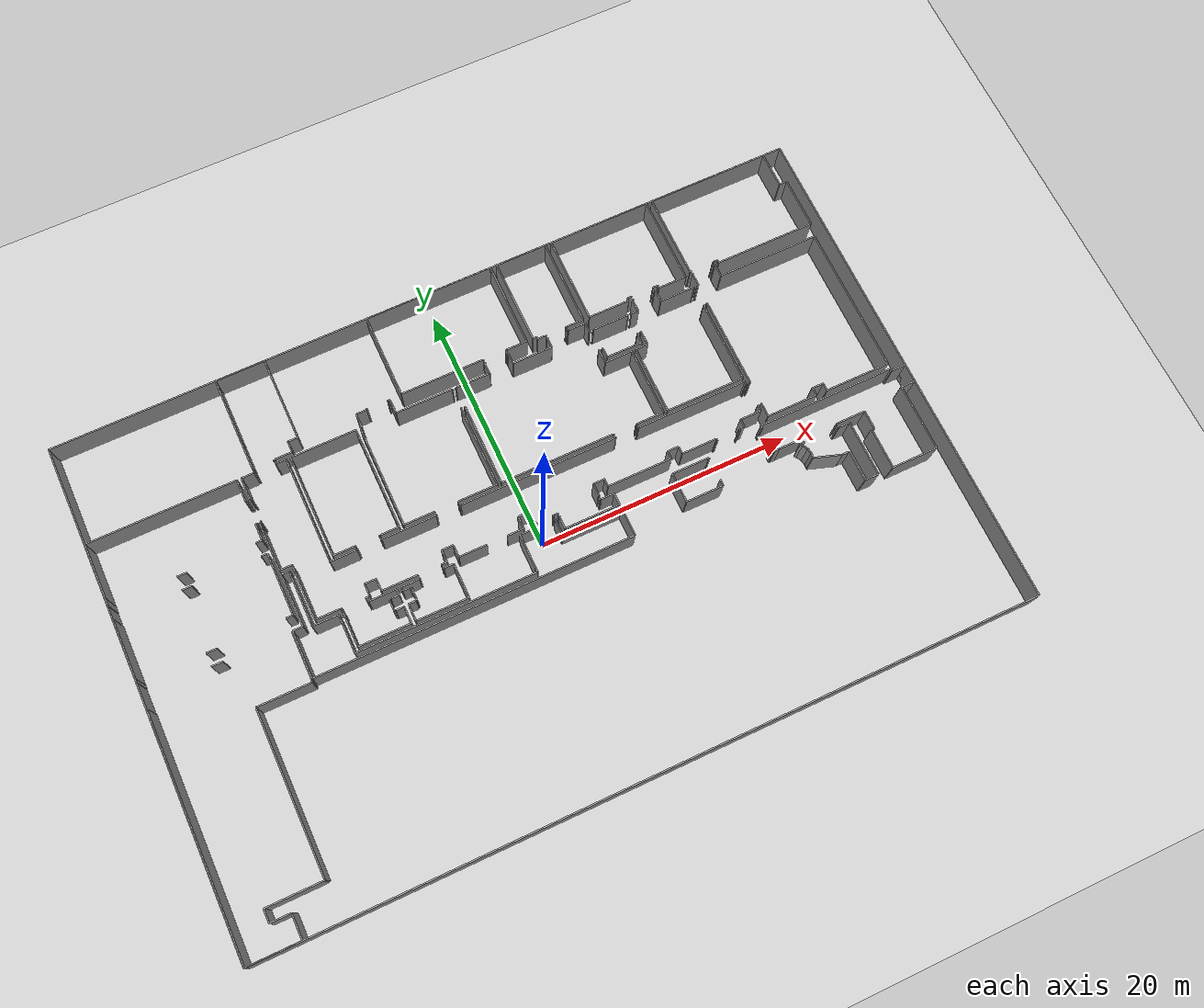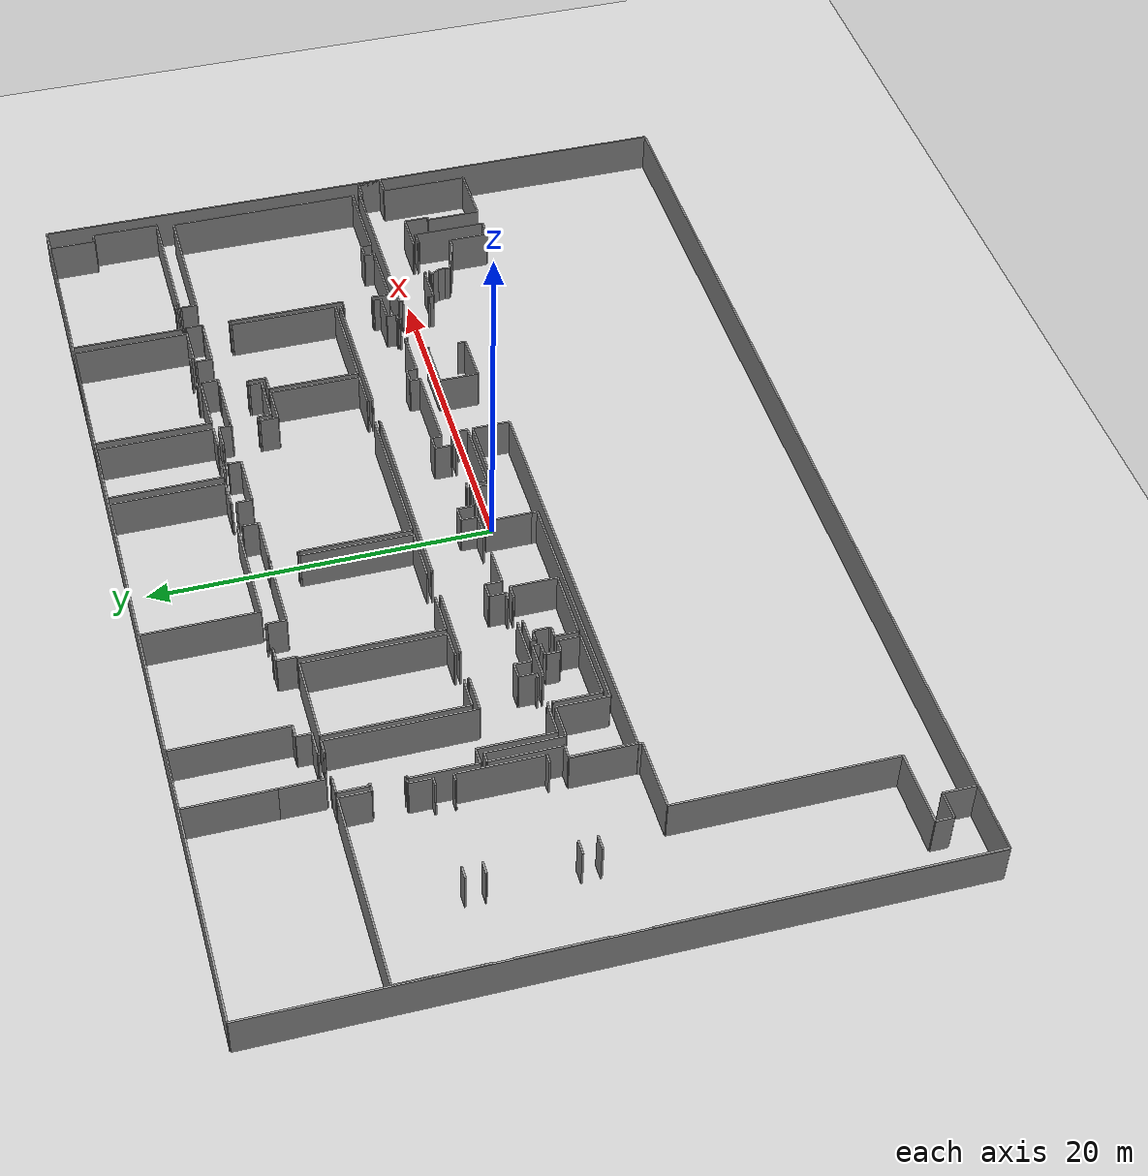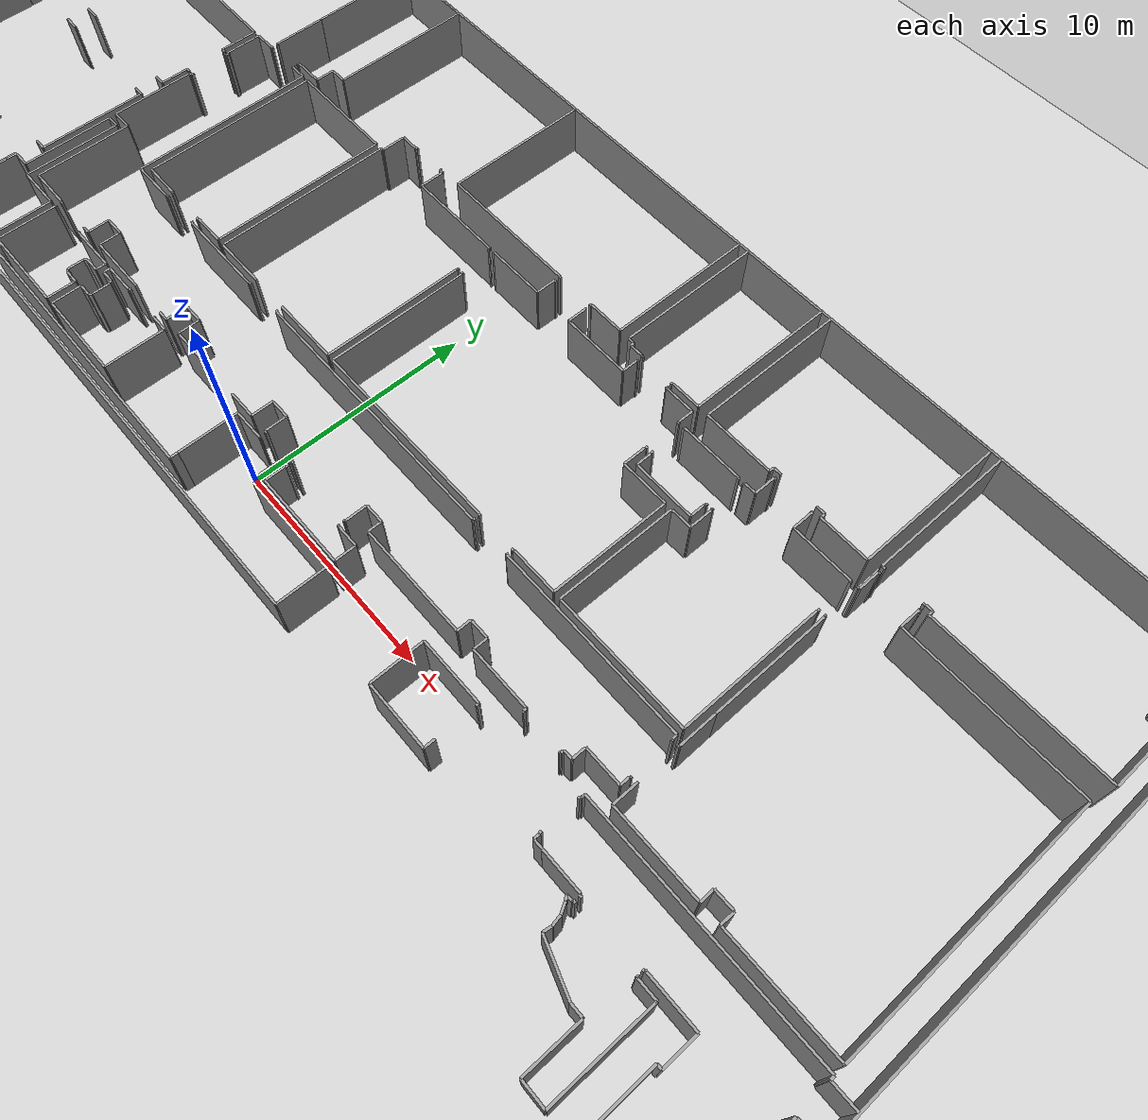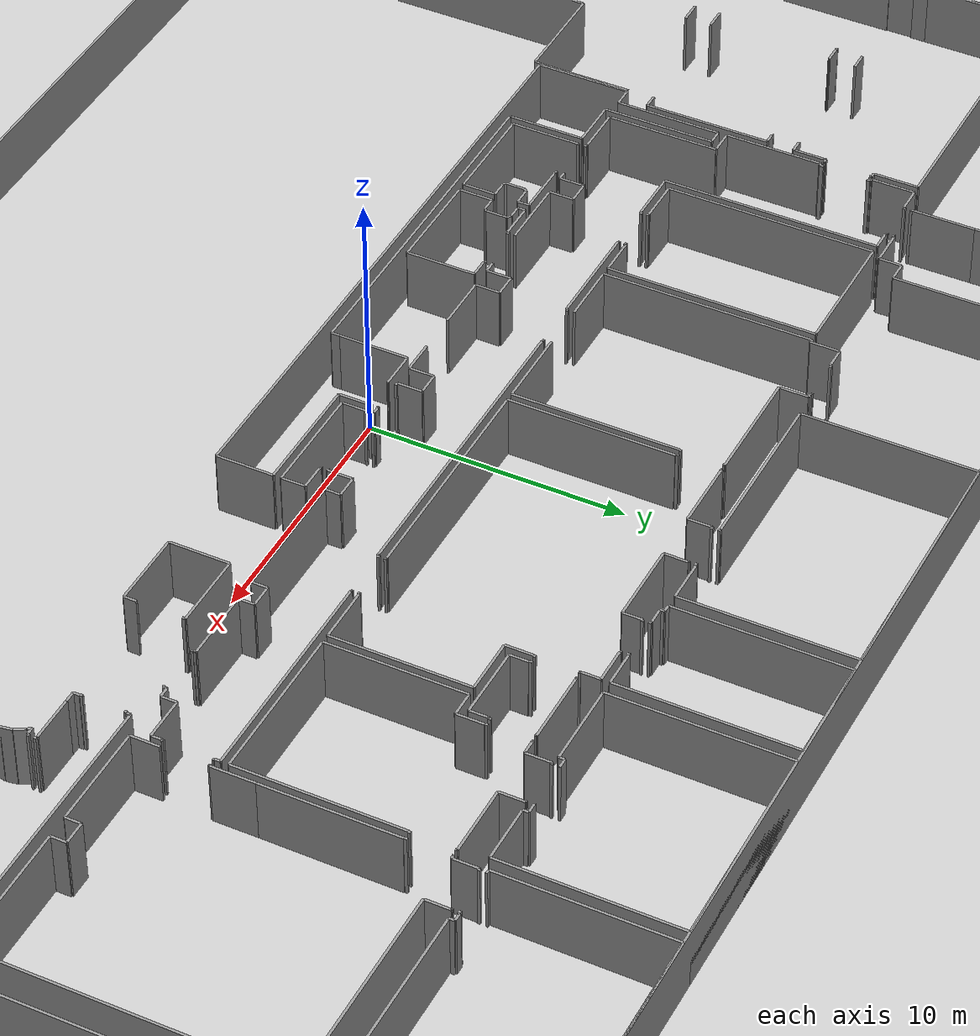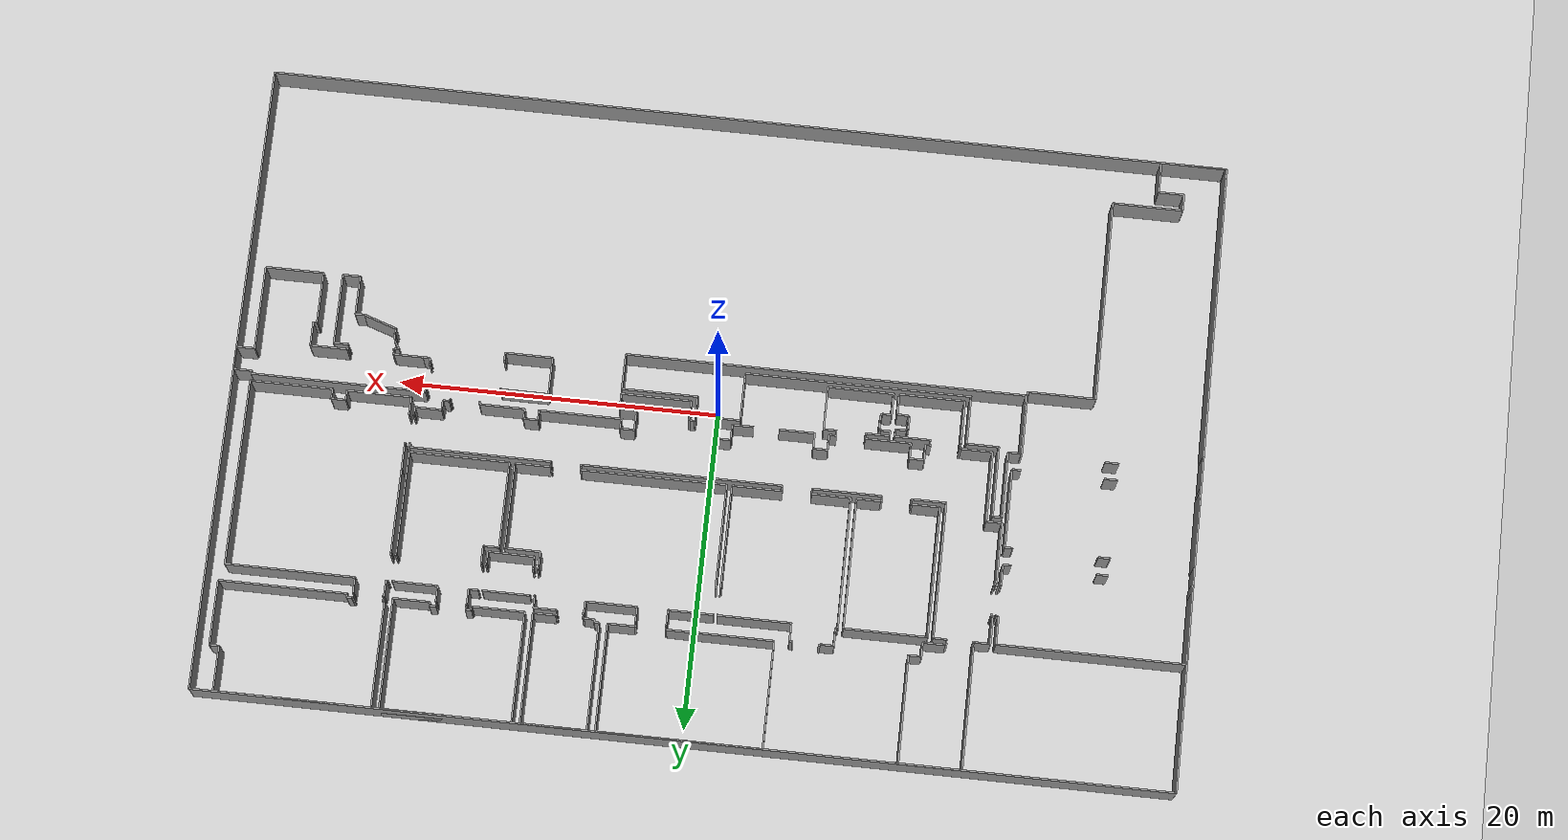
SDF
<sdf version="1.6">
  <world name="default">
    <light name="sun" type="directional">
      <cast_shadows>1</cast_shadows>
      <pose frame="">0 0 10 0 -0 0</pose>
      <diffuse>0.8 0.8 0.8 1</diffuse>
      <specular>0.1 0.1 0.1 1</specular>
      <attenuation>
        <range>1000</range>
        <constant>0.9</constant>
        <linear>0.01</linear>
        <quadratic>0.001</quadratic>
      </attenuation>
      <direction>-0.5 0.5 -1</direction>
    </light>
    <model name="ground_plane">
      <static>1</static>
      <link name="link">
        <collision name="collision">
          <geometry>
            <plane>
              <normal>0 0 1</normal>
              <size>100 100</size>
            </plane>
          </geometry>
          <surface>
            <friction>
              <ode>
                <mu>100</mu>
                <mu2>50</mu2>
              </ode>
              <torsional>
                <ode />
              </torsional>
            </friction>
            <contact>
              <ode />
            </contact>
            <bounce />
          </surface>
          <max_contacts>10</max_contacts>
        </collision>
        <visual name="visual">
          <cast_shadows>0</cast_shadows>
          <geometry>
            <plane>
              <normal>0 0 1</normal>
              <size>100 100</size>
            </plane>
          </geometry>
          <material>
            <script>
              <uri>file://media/materials/scripts/gazebo.material</uri>
              <name>Gazebo/Grey</name>
            </script>
          </material>
        </visual>
        <self_collide>0</self_collide>
        <kinematic>0</kinematic>
        <gravity>1</gravity>
      </link>
    </model>
    <gravity>0 0 -9.8</gravity>
    <magnetic_field>6e-06 2.3e-05 -4.2e-05</magnetic_field>
    <atmosphere type="adiabatic" />
    <physics default="0" name="default_physics" type="ode">
      <max_step_size>0.001</max_step_size>
      <real_time_factor>1</real_time_factor>
      <real_time_update_rate>1000</real_time_update_rate>
    </physics>
    <scene>
      <ambient>0.4 0.4 0.4 1</ambient>
      <background>0.7 0.7 0.7 1</background>
      <shadows>1</shadows>
    </scene>
    <spherical_coordinates>
      <surface_model>EARTH_WGS84</surface_model>
      <latitude_deg>0</latitude_deg>
      <longitude_deg>0</longitude_deg>
      <elevation>0</elevation>
      <heading_deg>0</heading_deg>
    </spherical_coordinates>
  <model name="0510032259_A_40_1_101">
		<static>1</static>
		<link name="Wall_0">
			<collision name="Wall_0_Collision">
				<geometry>
					<box>
						<size>4.41806100799 0.1 2.5</size>
					</box>
				</geometry>
				<pose frame="">2.209030504 0 1.25 0 0 0</pose>
			</collision>
			<visual name="Wall_0_Visual">
				<pose frame="">2.209030504 0 1.25 0 0 0</pose>
				<geometry>
					<box>
						<size>4.41806100799 0.1 2.5</size>
					</box>
				</geometry>
				<material>
					<script>
						<uri>file://media/materials/scripts/gazebo.material</uri>
						<name>Gazebo/Grey</name>
					</script>
					<ambient>1 1 1 1</ambient>
				</material>
			</visual>
			<pose frame="">0.0423066661585 -12.3643455171 0 0 0 1.57079632679</pose>
		</link>
		<link name="Wall_1">
			<collision name="Wall_1_Collision">
				<geometry>
					<box>
						<size>11.6479272275 0.1 2.5</size>
					</box>
				</geometry>
				<pose frame="">5.82396361373 0 1.25 0 0 0</pose>
			</collision>
			<visual name="Wall_1_Visual">
				<pose frame="">5.82396361373 0 1.25 0 0 0</pose>
				<geometry>
					<box>
						<size>11.6479272275 0.1 2.5</size>
					</box>
				</geometry>
				<material>
					<script>
						<uri>file://media/materials/scripts/gazebo.material</uri>
						<name>Gazebo/Grey</name>
					</script>
					<ambient>1 1 1 1</ambient>
				</material>
			</visual>
			<pose frame="">0.0423066661585 -7.94628450915 0 0 0 0.0</pose>
		</link>
		<link name="Wall_2">
			<collision name="Wall_2_Collision">
				<geometry>
					<box>
						<size>1.77167104979 0.1 2.5</size>
					</box>
				</geometry>
				<pose frame="">0.885835524895 0 1.25 0 0 0</pose>
			</collision>
			<visual name="Wall_2_Visual">
				<pose frame="">0.885835524895 0 1.25 0 0 0</pose>
				<geometry>
					<box>
						<size>1.77167104979 0.1 2.5</size>
					</box>
				</geometry>
				<material>
					<script>
						<uri>file://media/materials/scripts/gazebo.material</uri>
						<name>Gazebo/Grey</name>
					</script>
					<ambient>1 1 1 1</ambient>
				</material>
			</visual>
			<pose frame="">11.6902338936 -7.94628450915 0 0 0 -1.57079632679</pose>
		</link>
		<link name="Wall_3">
			<collision name="Wall_3_Collision">
				<geometry>
					<box>
						<size>0.170497135089 0.1 2.5</size>
					</box>
				</geometry>
				<pose frame="">0.0852485675446 0 1.25 0 0 0</pose>
			</collision>
			<visual name="Wall_3_Visual">
				<pose frame="">0.0852485675446 0 1.25 0 0 0</pose>
				<geometry>
					<box>
						<size>0.170497135089 0.1 2.5</size>
					</box>
				</geometry>
				<material>
					<script>
						<uri>file://media/materials/scripts/gazebo.material</uri>
						<name>Gazebo/Grey</name>
					</script>
					<ambient>1 1 1 1</ambient>
				</material>
			</visual>
			<pose frame="">11.6902338936 -9.71795555894 0 0 0 0.0</pose>
		</link>
		<link name="Wall_4">
			<collision name="Wall_4_Collision">
				<geometry>
					<box>
						<size>0.09388776664 0.1 2.5</size>
					</box>
				</geometry>
				<pose frame="">0.04694388332 0 1.25 0 0 0</pose>
			</collision>
			<visual name="Wall_4_Visual">
				<pose frame="">0.04694388332 0 1.25 0 0 0</pose>
				<geometry>
					<box>
						<size>0.09388776664 0.1 2.5</size>
					</box>
				</geometry>
				<material>
					<script>
						<uri>file://media/materials/scripts/gazebo.material</uri>
						<name>Gazebo/Grey</name>
					</script>
					<ambient>1 1 1 1</ambient>
				</material>
			</visual>
			<pose frame="">11.8607310287 -9.71795555894 0 0 0 -1.57079632679</pose>
		</link>
		<link name="Wall_5">
			<collision name="Wall_5_Collision">
				<geometry>
					<box>
						<size>0.054630229574 0.1 2.5</size>
					</box>
				</geometry>
				<pose frame="">0.027315114787 0 1.25 0 0 0</pose>
			</collision>
			<visual name="Wall_5_Visual">
				<pose frame="">0.027315114787 0 1.25 0 0 0</pose>
				<geometry>
					<box>
						<size>0.054630229574 0.1 2.5</size>
					</box>
				</geometry>
				<material>
					<script>
						<uri>file://media/materials/scripts/gazebo.material</uri>
						<name>Gazebo/Grey</name>
					</script>
					<ambient>1 1 1 1</ambient>
				</material>
			</visual>
			<pose frame="">11.8607310287 -11.5870716926 0 0 0 -1.57079632679</pose>
		</link>
		<link name="Wall_6">
			<collision name="Wall_6_Collision">
				<geometry>
					<box>
						<size>0.153853972126 0.1 2.5</size>
					</box>
				</geometry>
				<pose frame="">0.0769269860629 0 1.25 0 0 0</pose>
			</collision>
			<visual name="Wall_6_Visual">
				<pose frame="">0.0769269860629 0 1.25 0 0 0</pose>
				<geometry>
					<box>
						<size>0.153853972126 0.1 2.5</size>
					</box>
				</geometry>
				<material>
					<script>
						<uri>file://media/materials/scripts/gazebo.material</uri>
						<name>Gazebo/Grey</name>
					</script>
					<ambient>1 1 1 1</ambient>
				</material>
			</visual>
			<pose frame="">11.8607310287 -11.6417019222 0 0 0 3.14159265359</pose>
		</link>
		<link name="Wall_7">
			<collision name="Wall_7_Collision">
				<geometry>
					<box>
						<size>1.31353940364 0.1 2.5</size>
					</box>
				</geometry>
				<pose frame="">0.656769701821 0 1.25 0 0 0</pose>
			</collision>
			<visual name="Wall_7_Visual">
				<pose frame="">0.656769701821 0 1.25 0 0 0</pose>
				<geometry>
					<box>
						<size>1.31353940364 0.1 2.5</size>
					</box>
				</geometry>
				<material>
					<script>
						<uri>file://media/materials/scripts/gazebo.material</uri>
						<name>Gazebo/Grey</name>
					</script>
					<ambient>1 1 1 1</ambient>
				</material>
			</visual>
			<pose frame="">11.7068770566 -11.6417019222 0 0 0 -1.57079632679</pose>
		</link>
		<link name="Wall_8">
			<collision name="Wall_8_Collision">
				<geometry>
					<box>
						<size>0.510602075949 0.1 2.5</size>
					</box>
				</geometry>
				<pose frame="">0.255301037974 0 1.25 0 0 0</pose>
			</collision>
			<visual name="Wall_8_Visual">
				<pose frame="">0.255301037974 0 1.25 0 0 0</pose>
				<geometry>
					<box>
						<size>0.510602075949 0.1 2.5</size>
					</box>
				</geometry>
				<material>
					<script>
						<uri>file://media/materials/scripts/gazebo.material</uri>
						<name>Gazebo/Grey</name>
					</script>
					<ambient>1 1 1 1</ambient>
				</material>
			</visual>
			<pose frame="">11.7068770566 -12.9552413259 0 0 0 3.14159265359</pose>
		</link>
		<link name="Wall_9">
			<collision name="Wall_9_Collision">
				<geometry>
					<box>
						<size>0.72670910038 0.1 2.5</size>
					</box>
				</geometry>
				<pose frame="">0.36335455019 0 1.25 0 0 0</pose>
			</collision>
			<visual name="Wall_9_Visual">
				<pose frame="">0.36335455019 0 1.25 0 0 0</pose>
				<geometry>
					<box>
						<size>0.72670910038 0.1 2.5</size>
					</box>
				</geometry>
				<material>
					<script>
						<uri>file://media/materials/scripts/gazebo.material</uri>
						<name>Gazebo/Grey</name>
					</script>
					<ambient>1 1 1 1</ambient>
				</material>
			</visual>
			<pose frame="">5.94237146015 -12.9552413259 0 0 0 3.14159265359</pose>
		</link>
		<link name="Wall_10">
			<collision name="Wall_10_Collision">
				<geometry>
					<box>
						<size>0.590927275994 0.1 2.5</size>
					</box>
				</geometry>
				<pose frame="">0.295463637997 0 1.25 0 0 0</pose>
			</collision>
			<visual name="Wall_10_Visual">
				<pose frame="">0.295463637997 0 1.25 0 0 0</pose>
				<geometry>
					<box>
						<size>0.590927275994 0.1 2.5</size>
					</box>
				</geometry>
				<material>
					<script>
						<uri>file://media/materials/scripts/gazebo.material</uri>
						<name>Gazebo/Grey</name>
					</script>
					<ambient>1 1 1 1</ambient>
				</material>
			</visual>
			<pose frame="">0.0362084079735 -12.9552413259 0 0 0 1.56047633197</pose>
		</link>
		<link name="Wall_11">
			<collision name="Wall_11_Collision">
				<geometry>
					<box>
						<size>4.69146624995 0.1 2.5</size>
					</box>
				</geometry>
				<pose frame="">2.34573312498 0 1.25 0 0 0</pose>
			</collision>
			<visual name="Wall_11_Visual">
				<pose frame="">2.34573312498 0 1.25 0 0 0</pose>
				<geometry>
					<box>
						<size>4.69146624995 0.1 2.5</size>
					</box>
				</geometry>
				<material>
					<script>
						<uri>file://media/materials/scripts/gazebo.material</uri>
						<name>Gazebo/Grey</name>
					</script>
					<ambient>1 1 1 1</ambient>
				</material>
			</visual>
			<pose frame="">0.0318888084258 -18.6801082441 0 0 0 1.57079632679</pose>
		</link>
		<link name="Wall_12">
			<collision name="Wall_12_Collision">
				<geometry>
					<box>
						<size>0.0470074068428 0.1 2.5</size>
					</box>
				</geometry>
				<pose frame="">0.0235037034214 0 1.25 0 0 0</pose>
			</collision>
			<visual name="Wall_12_Visual">
				<pose frame="">0.0235037034214 0 1.25 0 0 0</pose>
				<geometry>
					<box>
						<size>0.0470074068428 0.1 2.5</size>
					</box>
				</geometry>
				<material>
					<script>
						<uri>file://media/materials/scripts/gazebo.material</uri>
						<name>Gazebo/Grey</name>
					</script>
					<ambient>1 1 1 1</ambient>
				</material>
			</visual>
			<pose frame="">5.221887665 -13.9886419941 0 0 0 -1.57079632679</pose>
		</link>
		<link name="Wall_13">
			<collision name="Wall_13_Collision">
				<geometry>
					<box>
						<size>0.706127479005 0.1 2.5</size>
					</box>
				</geometry>
				<pose frame="">0.353063739503 0 1.25 0 0 0</pose>
			</collision>
			<visual name="Wall_13_Visual">
				<pose frame="">0.353063739503 0 1.25 0 0 0</pose>
				<geometry>
					<box>
						<size>0.706127479005 0.1 2.5</size>
					</box>
				</geometry>
				<material>
					<script>
						<uri>file://media/materials/scripts/gazebo.material</uri>
						<name>Gazebo/Grey</name>
					</script>
					<ambient>1 1 1 1</ambient>
				</material>
			</visual>
			<pose frame="">5.221887665 -14.035649401 0 0 0 0.0</pose>
		</link>
		<link name="Wall_14">
			<collision name="Wall_14_Collision">
				<geometry>
					<box>
						<size>0.0330322318354 0.1 2.5</size>
					</box>
				</geometry>
				<pose frame="">0.0165161159177 0 1.25 0 0 0</pose>
			</collision>
			<visual name="Wall_14_Visual">
				<pose frame="">0.0165161159177 0 1.25 0 0 0</pose>
				<geometry>
					<box>
						<size>0.0330322318354 0.1 2.5</size>
					</box>
				</geometry>
				<material>
					<script>
						<uri>file://media/materials/scripts/gazebo.material</uri>
						<name>Gazebo/Grey</name>
					</script>
					<ambient>1 1 1 1</ambient>
				</material>
			</visual>
			<pose frame="">5.92801514401 -14.035649401 0 0 0 1.57079632679</pose>
		</link>
		<link name="Wall_15">
			<collision name="Wall_15_Collision">
				<geometry>
					<box>
						<size>0.0414173368398 0.1 2.5</size>
					</box>
				</geometry>
				<pose frame="">0.0207086684199 0 1.25 0 0 0</pose>
			</collision>
			<visual name="Wall_15_Visual">
				<pose frame="">0.0207086684199 0 1.25 0 0 0</pose>
				<geometry>
					<box>
						<size>0.0414173368398 0.1 2.5</size>
					</box>
				</geometry>
				<material>
					<script>
						<uri>file://media/materials/scripts/gazebo.material</uri>
						<name>Gazebo/Grey</name>
					</script>
					<ambient>1 1 1 1</ambient>
				</material>
			</visual>
			<pose frame="">11.2300694947 -14.0026171691 0 0 0 -1.57079632679</pose>
		</link>
		<link name="Wall_16">
			<collision name="Wall_16_Collision">
				<geometry>
					<box>
						<size>0.45838574024 0.1 2.5</size>
					</box>
				</geometry>
				<pose frame="">0.22919287012 0 1.25 0 0 0</pose>
			</collision>
			<visual name="Wall_16_Visual">
				<pose frame="">0.22919287012 0 1.25 0 0 0</pose>
				<geometry>
					<box>
						<size>0.45838574024 0.1 2.5</size>
					</box>
				</geometry>
				<material>
					<script>
						<uri>file://media/materials/scripts/gazebo.material</uri>
						<name>Gazebo/Grey</name>
					</script>
					<ambient>1 1 1 1</ambient>
				</material>
			</visual>
			<pose frame="">11.2300694947 -14.044034506 0 0 0 0.0</pose>
		</link>
		<link name="Wall_17">
			<collision name="Wall_17_Collision">
				<geometry>
					<box>
						<size>4.95851913964 0.1 2.5</size>
					</box>
				</geometry>
				<pose frame="">2.47925956982 0 1.25 0 0 0</pose>
			</collision>
			<visual name="Wall_17_Visual">
				<pose frame="">2.47925956982 0 1.25 0 0 0</pose>
				<geometry>
					<box>
						<size>4.95851913964 0.1 2.5</size>
					</box>
				</geometry>
				<material>
					<script>
						<uri>file://media/materials/scripts/gazebo.material</uri>
						<name>Gazebo/Grey</name>
					</script>
					<ambient>1 1 1 1</ambient>
				</material>
			</visual>
			<pose frame="">11.688455235 -14.044034506 0 0 0 -1.57079632679</pose>
		</link>
		<link name="Wall_18">
			<collision name="Wall_18_Collision">
				<geometry>
					<box>
						<size>0.558752906201 0.1 2.5</size>
					</box>
				</geometry>
				<pose frame="">0.279376453101 0 1.25 0 0 0</pose>
			</collision>
			<visual name="Wall_18_Visual">
				<pose frame="">0.279376453101 0 1.25 0 0 0</pose>
				<geometry>
					<box>
						<size>0.558752906201 0.1 2.5</size>
					</box>
				</geometry>
				<material>
					<script>
						<uri>file://media/materials/scripts/gazebo.material</uri>
						<name>Gazebo/Grey</name>
					</script>
					<ambient>1 1 1 1</ambient>
				</material>
			</visual>
			<pose frame="">11.688455235 -19.0025536456 0 0 0 3.14159265359</pose>
		</link>
		<link name="Wall_19">
			<collision name="Wall_19_Collision">
				<geometry>
					<box>
						<size>0.847276746579 0.1 2.5</size>
					</box>
				</geometry>
				<pose frame="">0.42363837329 0 1.25 0 0 0</pose>
			</collision>
			<visual name="Wall_19_Visual">
				<pose frame="">0.42363837329 0 1.25 0 0 0</pose>
				<geometry>
					<box>
						<size>0.847276746579 0.1 2.5</size>
					</box>
				</geometry>
				<material>
					<script>
						<uri>file://media/materials/scripts/gazebo.material</uri>
						<name>Gazebo/Grey</name>
					</script>
					<ambient>1 1 1 1</ambient>
				</material>
			</visual>
			<pose frame="">5.98391584404 -19.0025536456 0 0 0 3.14159265359</pose>
		</link>
		<link name="Wall_20">
			<collision name="Wall_20_Collision">
				<geometry>
					<box>
						<size>0.322593764156 0.1 2.5</size>
					</box>
				</geometry>
				<pose frame="">0.161296882078 0 1.25 0 0 0</pose>
			</collision>
			<visual name="Wall_20_Visual">
				<pose frame="">0.161296882078 0 1.25 0 0 0</pose>
				<geometry>
					<box>
						<size>0.322593764156 0.1 2.5</size>
					</box>
				</geometry>
				<material>
					<script>
						<uri>file://media/materials/scripts/gazebo.material</uri>
						<name>Gazebo/Grey</name>
					</script>
					<ambient>1 1 1 1</ambient>
				</material>
			</visual>
			<pose frame="">0.0221061859206 -19.0025536456 0 0 0 1.54046678059</pose>
		</link>
		<link name="Wall_21">
			<collision name="Wall_21_Collision">
				<geometry>
					<box>
						<size>18.7088208764 0.1 2.5</size>
					</box>
				</geometry>
				<pose frame="">9.35441043819 0 1.25 0 0 0</pose>
			</collision>
			<visual name="Wall_21_Visual">
				<pose frame="">9.35441043819 0 1.25 0 0 0</pose>
				<geometry>
					<box>
						<size>18.7088208764 0.1 2.5</size>
					</box>
				</geometry>
				<material>
					<script>
						<uri>file://media/materials/scripts/gazebo.material</uri>
						<name>Gazebo/Grey</name>
					</script>
					<ambient>1 1 1 1</ambient>
				</material>
			</visual>
			<pose frame="">0.0362084079735 -39.7117302537 0 0 0 1.57079632679</pose>
		</link>
		<link name="Wall_22">
			<collision name="Wall_22_Collision">
				<geometry>
					<box>
						<size>0.0362084079735 0.1 2.5</size>
					</box>
				</geometry>
				<pose frame="">0.0181042039867 0 1.25 0 0 0</pose>
			</collision>
			<visual name="Wall_22_Visual">
				<pose frame="">0.0181042039867 0 1.25 0 0 0</pose>
				<geometry>
					<box>
						<size>0.0362084079735 0.1 2.5</size>
					</box>
				</geometry>
				<material>
					<script>
						<uri>file://media/materials/scripts/gazebo.material</uri>
						<name>Gazebo/Grey</name>
					</script>
					<ambient>1 1 1 1</ambient>
				</material>
			</visual>
			<pose frame="">0.0362084079735 -21.0029093773 0 0 0 3.14159265359</pose>
		</link>
		<link name="Wall_23">
			<collision name="Wall_23_Collision">
				<geometry>
					<box>
						<size>0.0195652450102 0.1 2.5</size>
					</box>
				</geometry>
				<pose frame="">0.00978262250511 0 1.25 0 0 0</pose>
			</collision>
			<visual name="Wall_23_Visual">
				<pose frame="">0.00978262250511 0 1.25 0 0 0</pose>
				<geometry>
					<box>
						<size>0.0195652450102 0.1 2.5</size>
					</box>
				</geometry>
				<material>
					<script>
						<uri>file://media/materials/scripts/gazebo.material</uri>
						<name>Gazebo/Grey</name>
					</script>
					<ambient>1 1 1 1</ambient>
				</material>
			</visual>
			<pose frame="">0.0 -20.0471344539 0 0 0 0.0</pose>
		</link>
		<link name="Wall_24">
			<collision name="Wall_24_Collision">
				<geometry>
					<box>
						<size>0.884374483871 0.1 2.5</size>
					</box>
				</geometry>
				<pose frame="">0.442187241936 0 1.25 0 0 0</pose>
			</collision>
			<visual name="Wall_24_Visual">
				<pose frame="">0.442187241936 0 1.25 0 0 0</pose>
				<geometry>
					<box>
						<size>0.884374483871 0.1 2.5</size>
					</box>
				</geometry>
				<material>
					<script>
						<uri>file://media/materials/scripts/gazebo.material</uri>
						<name>Gazebo/Grey</name>
					</script>
					<ambient>1 1 1 1</ambient>
				</material>
			</visual>
			<pose frame="">5.14781923746 -20.0471344539 0 0 0 0.0</pose>
		</link>
		<link name="Wall_25">
			<collision name="Wall_25_Collision">
				<geometry>
					<box>
						<size>3.73480199718 0.1 2.5</size>
					</box>
				</geometry>
				<pose frame="">1.86740099859 0 1.25 0 0 0</pose>
			</collision>
			<visual name="Wall_25_Visual">
				<pose frame="">1.86740099859 0 1.25 0 0 0</pose>
				<geometry>
					<box>
						<size>3.73480199718 0.1 2.5</size>
					</box>
				</geometry>
				<material>
					<script>
						<uri>file://media/materials/scripts/gazebo.material</uri>
						<name>Gazebo/Grey</name>
					</script>
					<ambient>1 1 1 1</ambient>
				</material>
			</visual>
			<pose frame="">11.1791236295 -20.0471344539 0 0 0 -1.57079632679</pose>
		</link>
		<link name="Wall_26">
			<collision name="Wall_26_Collision">
				<geometry>
					<box>
						<size>0.0316347143347 0.1 2.5</size>
					</box>
				</geometry>
				<pose frame="">0.0158173571674 0 1.25 0 0 0</pose>
			</collision>
			<visual name="Wall_26_Visual">
				<pose frame="">0.0158173571674 0 1.25 0 0 0</pose>
				<geometry>
					<box>
						<size>0.0316347143347 0.1 2.5</size>
					</box>
				</geometry>
				<material>
					<script>
						<uri>file://media/materials/scripts/gazebo.material</uri>
						<name>Gazebo/Grey</name>
					</script>
					<ambient>1 1 1 1</ambient>
				</material>
			</visual>
			<pose frame="">11.1791236295 -23.7819364511 0 0 0 3.14159265359</pose>
		</link>
		<link name="Wall_27">
			<collision name="Wall_27_Collision">
				<geometry>
					<box>
						<size>0.226143741027 0.1 2.5</size>
					</box>
				</geometry>
				<pose frame="">0.113071870514 0 1.25 0 0 0</pose>
			</collision>
			<visual name="Wall_27_Visual">
				<pose frame="">0.113071870514 0 1.25 0 0 0</pose>
				<geometry>
					<box>
						<size>0.226143741027 0.1 2.5</size>
					</box>
				</geometry>
				<material>
					<script>
						<uri>file://media/materials/scripts/gazebo.material</uri>
						<name>Gazebo/Grey</name>
					</script>
					<ambient>1 1 1 1</ambient>
				</material>
			</visual>
			<pose frame="">11.1474889151 -23.7819364511 0 0 0 -1.57079632679</pose>
		</link>
		<link name="Wall_28">
			<collision name="Wall_28_Collision">
				<geometry>
					<box>
						<size>4.21249888834 0.1 2.5</size>
					</box>
				</geometry>
				<pose frame="">2.10624944417 0 1.25 0 0 0</pose>
			</collision>
			<visual name="Wall_28_Visual">
				<pose frame="">2.10624944417 0 1.25 0 0 0</pose>
				<geometry>
					<box>
						<size>4.21249888834 0.1 2.5</size>
					</box>
				</geometry>
				<material>
					<script>
						<uri>file://media/materials/scripts/gazebo.material</uri>
						<name>Gazebo/Grey</name>
					</script>
					<ambient>1 1 1 1</ambient>
				</material>
			</visual>
			<pose frame="">11.1474889151 -24.0080801921 0 0 0 3.14159265359</pose>
		</link>
		<link name="Wall_29">
			<collision name="Wall_29_Collision">
				<geometry>
					<box>
						<size>12.735195843 0.1 2.5</size>
					</box>
				</geometry>
				<pose frame="">6.36759792151 0 1.25 0 0 0</pose>
			</collision>
			<visual name="Wall_29_Visual">
				<pose frame="">6.36759792151 0 1.25 0 0 0</pose>
				<geometry>
					<box>
						<size>12.735195843 0.1 2.5</size>
					</box>
				</geometry>
				<material>
					<script>
						<uri>file://media/materials/scripts/gazebo.material</uri>
						<name>Gazebo/Grey</name>
					</script>
					<ambient>1 1 1 1</ambient>
				</material>
			</visual>
			<pose frame="">6.93499002681 -24.0080801921 0 0 0 -1.57079632679</pose>
		</link>
		<link name="Wall_30">
			<collision name="Wall_30_Collision">
				<geometry>
					<box>
						<size>4.39061884616 0.1 2.5</size>
					</box>
				</geometry>
				<pose frame="">2.19530942308 0 1.25 0 0 0</pose>
			</collision>
			<visual name="Wall_30_Visual">
				<pose frame="">2.19530942308 0 1.25 0 0 0</pose>
				<geometry>
					<box>
						<size>4.39061884616 0.1 2.5</size>
					</box>
				</geometry>
				<material>
					<script>
						<uri>file://media/materials/scripts/gazebo.material</uri>
						<name>Gazebo/Grey</name>
					</script>
					<ambient>1 1 1 1</ambient>
				</material>
			</visual>
			<pose frame="">6.93499002681 -36.7432760351 0 0 0 3.14159265359</pose>
		</link>
		<link name="Wall_31">
			<collision name="Wall_31_Collision">
				<geometry>
					<box>
						<size>1.0253967044 0.1 2.5</size>
					</box>
				</geometry>
				<pose frame="">0.5126983522 0 1.25 0 0 0</pose>
			</collision>
			<visual name="Wall_31_Visual">
				<pose frame="">0.5126983522 0 1.25 0 0 0</pose>
				<geometry>
					<box>
						<size>1.0253967044 0.1 2.5</size>
					</box>
				</geometry>
				<material>
					<script>
						<uri>file://media/materials/scripts/gazebo.material</uri>
						<name>Gazebo/Grey</name>
					</script>
					<ambient>1 1 1 1</ambient>
				</material>
			</visual>
			<pose frame="">2.54437118065 -36.7432760351 0 0 0 -1.57079632679</pose>
		</link>
		<link name="Wall_32">
			<collision name="Wall_32_Collision">
				<geometry>
					<box>
						<size>1.58999377469 0.1 2.5</size>
					</box>
				</geometry>
				<pose frame="">0.794996887347 0 1.25 0 0 0</pose>
			</collision>
			<visual name="Wall_32_Visual">
				<pose frame="">0.794996887347 0 1.25 0 0 0</pose>
				<geometry>
					<box>
						<size>1.58999377469 0.1 2.5</size>
					</box>
				</geometry>
				<material>
					<script>
						<uri>file://media/materials/scripts/gazebo.material</uri>
						<name>Gazebo/Grey</name>
					</script>
					<ambient>1 1 1 1</ambient>
				</material>
			</visual>
			<pose frame="">2.54437118065 -37.7686727395 0 0 0 0.0</pose>
		</link>
		<link name="Wall_33">
			<collision name="Wall_33_Collision">
				<geometry>
					<box>
						<size>1.94280342011 0.1 2.5</size>
					</box>
				</geometry>
				<pose frame="">0.971401710053 0 1.25 0 0 0</pose>
			</collision>
			<visual name="Wall_33_Visual">
				<pose frame="">0.971401710053 0 1.25 0 0 0</pose>
				<geometry>
					<box>
						<size>1.94280342011 0.1 2.5</size>
					</box>
				</geometry>
				<material>
					<script>
						<uri>file://media/materials/scripts/gazebo.material</uri>
						<name>Gazebo/Grey</name>
					</script>
					<ambient>1 1 1 1</ambient>
				</material>
			</visual>
			<pose frame="">4.13436495534 -37.7686727395 0 0 0 -1.57079632679</pose>
		</link>
		<link name="Wall_34">
			<collision name="Wall_34_Collision">
				<geometry>
					<box>
						<size>4.09815655525 0.1 2.5</size>
					</box>
				</geometry>
				<pose frame="">2.04907827762 0 1.25 0 0 0</pose>
			</collision>
			<visual name="Wall_34_Visual">
				<pose frame="">2.04907827762 0 1.25 0 0 0</pose>
				<geometry>
					<box>
						<size>4.09815655525 0.1 2.5</size>
					</box>
				</geometry>
				<material>
					<script>
						<uri>file://media/materials/scripts/gazebo.material</uri>
						<name>Gazebo/Grey</name>
					</script>
					<ambient>1 1 1 1</ambient>
				</material>
			</visual>
			<pose frame="">4.13436495534 -39.7114761596 0 0 0 -3.14153065154</pose>
		</link>
		<link name="Wall_35">
			<collision name="Wall_35_Collision">
				<geometry>
					<box>
						<size>4.4091677148 0.1 2.5</size>
					</box>
				</geometry>
				<pose frame="">2.2045838574 0 1.25 0 0 0</pose>
			</collision>
			<visual name="Wall_35_Visual">
				<pose frame="">2.2045838574 0 1.25 0 0 0</pose>
				<geometry>
					<box>
						<size>4.4091677148 0.1 2.5</size>
					</box>
				</geometry>
				<material>
					<script>
						<uri>file://media/materials/scripts/gazebo.material</uri>
						<name>Gazebo/Grey</name>
					</script>
					<ambient>1 1 1 1</ambient>
				</material>
			</visual>
			<pose frame="">12.9830646288 -19.9635374979 0 0 0 1.57079632679</pose>
		</link>
		<link name="Wall_36">
			<collision name="Wall_36_Collision">
				<geometry>
					<box>
						<size>0.973434462782 0.1 2.5</size>
					</box>
				</geometry>
				<pose frame="">0.486717231391 0 1.25 0 0 0</pose>
			</collision>
			<visual name="Wall_36_Visual">
				<pose frame="">0.486717231391 0 1.25 0 0 0</pose>
				<geometry>
					<box>
						<size>0.973434462782 0.1 2.5</size>
					</box>
				</geometry>
				<material>
					<script>
						<uri>file://media/materials/scripts/gazebo.material</uri>
						<name>Gazebo/Grey</name>
					</script>
					<ambient>1 1 1 1</ambient>
				</material>
			</visual>
			<pose frame="">12.9830646288 -15.5543697831 0 0 0 3.14159265359</pose>
		</link>
		<link name="Wall_37">
			<collision name="Wall_37_Collision">
				<geometry>
					<box>
						<size>3.84609520906 0.1 2.5</size>
					</box>
				</geometry>
				<pose frame="">1.92304760453 0 1.25 0 0 0</pose>
			</collision>
			<visual name="Wall_37_Visual">
				<pose frame="">1.92304760453 0 1.25 0 0 0</pose>
				<geometry>
					<box>
						<size>3.84609520906 0.1 2.5</size>
					</box>
				</geometry>
				<material>
					<script>
						<uri>file://media/materials/scripts/gazebo.material</uri>
						<name>Gazebo/Grey</name>
					</script>
					<ambient>1 1 1 1</ambient>
				</material>
			</visual>
			<pose frame="">12.0096301661 -15.5543697831 0 0 0 1.57079632679</pose>
		</link>
		<link name="Wall_38">
			<collision name="Wall_38_Collision">
				<geometry>
					<box>
						<size>0.119297175744 0.1 2.5</size>
					</box>
				</geometry>
				<pose frame="">0.0596485878721 0 1.25 0 0 0</pose>
			</collision>
			<visual name="Wall_38_Visual">
				<pose frame="">0.0596485878721 0 1.25 0 0 0</pose>
				<geometry>
					<box>
						<size>0.119297175744 0.1 2.5</size>
					</box>
				</geometry>
				<material>
					<script>
						<uri>file://media/materials/scripts/gazebo.material</uri>
						<name>Gazebo/Grey</name>
					</script>
					<ambient>1 1 1 1</ambient>
				</material>
			</visual>
			<pose frame="">12.0096301661 -11.7082745741 0 0 0 0.0</pose>
		</link>
		<link name="Wall_39">
			<collision name="Wall_39_Collision">
				<geometry>
					<box>
						<size>0.153853972126 0.1 2.5</size>
					</box>
				</geometry>
				<pose frame="">0.0769269860629 0 1.25 0 0 0</pose>
			</collision>
			<visual name="Wall_39_Visual">
				<pose frame="">0.0769269860629 0 1.25 0 0 0</pose>
				<geometry>
					<box>
						<size>0.153853972126 0.1 2.5</size>
					</box>
				</geometry>
				<material>
					<script>
						<uri>file://media/materials/scripts/gazebo.material</uri>
						<name>Gazebo/Grey</name>
					</script>
					<ambient>1 1 1 1</ambient>
				</material>
			</visual>
			<pose frame="">12.1289273418 -11.7082745741 0 0 0 1.57079632679</pose>
		</link>
		<link name="Wall_40">
			<collision name="Wall_40_Collision">
				<geometry>
					<box>
						<size>0.137718997345 0.1 2.5</size>
					</box>
				</geometry>
				<pose frame="">0.0688594986724 0 1.25 0 0 0</pose>
			</collision>
			<visual name="Wall_40_Visual">
				<pose frame="">0.0688594986724 0 1.25 0 0 0</pose>
				<geometry>
					<box>
						<size>0.137718997345 0.1 2.5</size>
					</box>
				</geometry>
				<material>
					<script>
						<uri>file://media/materials/scripts/gazebo.material</uri>
						<name>Gazebo/Grey</name>
					</script>
					<ambient>1 1 1 1</ambient>
				</material>
			</visual>
			<pose frame="">12.1289273418 -9.80777782013 0 0 0 1.57079632679</pose>
		</link>
		<link name="Wall_41">
			<collision name="Wall_41_Collision">
				<geometry>
					<box>
						<size>0.0961746134594 0.1 2.5</size>
					</box>
				</geometry>
				<pose frame="">0.0480873067297 0 1.25 0 0 0</pose>
			</collision>
			<visual name="Wall_41_Visual">
				<pose frame="">0.0480873067297 0 1.25 0 0 0</pose>
				<geometry>
					<box>
						<size>0.0961746134594 0.1 2.5</size>
					</box>
				</geometry>
				<material>
					<script>
						<uri>file://media/materials/scripts/gazebo.material</uri>
						<name>Gazebo/Grey</name>
					</script>
					<ambient>1 1 1 1</ambient>
				</material>
			</visual>
			<pose frame="">12.1289273418 -9.67005882278 0 0 0 3.14159265359</pose>
		</link>
		<link name="Wall_42">
			<collision name="Wall_42_Collision">
				<geometry>
					<box>
						<size>1.72898324249 0.1 2.5</size>
					</box>
				</geometry>
				<pose frame="">0.864491621247 0 1.25 0 0 0</pose>
			</collision>
			<visual name="Wall_42_Visual">
				<pose frame="">0.864491621247 0 1.25 0 0 0</pose>
				<geometry>
					<box>
						<size>1.72898324249 0.1 2.5</size>
					</box>
				</geometry>
				<material>
					<script>
						<uri>file://media/materials/scripts/gazebo.material</uri>
						<name>Gazebo/Grey</name>
					</script>
					<ambient>1 1 1 1</ambient>
				</material>
			</visual>
			<pose frame="">12.0327527283 -9.67005882278 0 0 0 1.57079632679</pose>
		</link>
		<link name="Wall_43">
			<collision name="Wall_43_Collision">
				<geometry>
					<box>
						<size>0.980040909149 0.1 2.5</size>
					</box>
				</geometry>
				<pose frame="">0.490020454574 0 1.25 0 0 0</pose>
			</collision>
			<visual name="Wall_43_Visual">
				<pose frame="">0.490020454574 0 1.25 0 0 0</pose>
				<geometry>
					<box>
						<size>0.980040909149 0.1 2.5</size>
					</box>
				</geometry>
				<material>
					<script>
						<uri>file://media/materials/scripts/gazebo.material</uri>
						<name>Gazebo/Grey</name>
					</script>
					<ambient>1 1 1 1</ambient>
				</material>
			</visual>
			<pose frame="">12.0327527283 -7.94107558029 0 0 0 0.0</pose>
		</link>
		<link name="Wall_44">
			<collision name="Wall_44_Collision">
				<geometry>
					<box>
						<size>0.0323969966078 0.1 2.5</size>
					</box>
				</geometry>
				<pose frame="">0.0161984983039 0 1.25 0 0 0</pose>
			</collision>
			<visual name="Wall_44_Visual">
				<pose frame="">0.0161984983039 0 1.25 0 0 0</pose>
				<geometry>
					<box>
						<size>0.0323969966078 0.1 2.5</size>
					</box>
				</geometry>
				<material>
					<script>
						<uri>file://media/materials/scripts/gazebo.material</uri>
						<name>Gazebo/Grey</name>
					</script>
					<ambient>1 1 1 1</ambient>
				</material>
			</visual>
			<pose frame="">13.0127936375 -7.94107558029 0 0 0 1.57079632679</pose>
		</link>
		<link name="Wall_45">
			<collision name="Wall_45_Collision">
				<geometry>
					<box>
						<size>0.115485764379 0.1 2.5</size>
					</box>
				</geometry>
				<pose frame="">0.0577428821893 0 1.25 0 0 0</pose>
			</collision>
			<visual name="Wall_45_Visual">
				<pose frame="">0.0577428821893 0 1.25 0 0 0</pose>
				<geometry>
					<box>
						<size>0.115485764379 0.1 2.5</size>
					</box>
				</geometry>
				<material>
					<script>
						<uri>file://media/materials/scripts/gazebo.material</uri>
						<name>Gazebo/Grey</name>
					</script>
					<ambient>1 1 1 1</ambient>
				</material>
			</visual>
			<pose frame="">13.0127936375 -7.90867858368 0 0 0 0.0</pose>
		</link>
		<link name="Wall_46">
			<collision name="Wall_46_Collision">
				<geometry>
					<box>
						<size>0.0627612404874 0.1 2.5</size>
					</box>
				</geometry>
				<pose frame="">0.0313806202437 0 1.25 0 0 0</pose>
			</collision>
			<visual name="Wall_46_Visual">
				<pose frame="">0.0313806202437 0 1.25 0 0 0</pose>
				<geometry>
					<box>
						<size>0.0627612404874 0.1 2.5</size>
					</box>
				</geometry>
				<material>
					<script>
						<uri>file://media/materials/scripts/gazebo.material</uri>
						<name>Gazebo/Grey</name>
					</script>
					<ambient>1 1 1 1</ambient>
				</material>
			</visual>
			<pose frame="">14.6773640279 -7.90867858368 0 0 0 0.0</pose>
		</link>
		<link name="Wall_47">
			<collision name="Wall_47_Collision">
				<geometry>
					<box>
						<size>0.0299831027429 0.1 2.5</size>
					</box>
				</geometry>
				<pose frame="">0.0149915513715 0 1.25 0 0 0</pose>
			</collision>
			<visual name="Wall_47_Visual">
				<pose frame="">0.0149915513715 0 1.25 0 0 0</pose>
				<geometry>
					<box>
						<size>0.0299831027429 0.1 2.5</size>
					</box>
				</geometry>
				<material>
					<script>
						<uri>file://media/materials/scripts/gazebo.material</uri>
						<name>Gazebo/Grey</name>
					</script>
					<ambient>1 1 1 1</ambient>
				</material>
			</visual>
			<pose frame="">14.7401252684 -7.90867858368 0 0 0 -1.57079632679</pose>
		</link>
		<link name="Wall_48">
			<collision name="Wall_48_Collision">
				<geometry>
					<box>
						<size>0.800777527919 0.1 2.5</size>
					</box>
				</geometry>
				<pose frame="">0.400388763959 0 1.25 0 0 0</pose>
			</collision>
			<visual name="Wall_48_Visual">
				<pose frame="">0.400388763959 0 1.25 0 0 0</pose>
				<geometry>
					<box>
						<size>0.800777527919 0.1 2.5</size>
					</box>
				</geometry>
				<material>
					<script>
						<uri>file://media/materials/scripts/gazebo.material</uri>
						<name>Gazebo/Grey</name>
					</script>
					<ambient>1 1 1 1</ambient>
				</material>
			</visual>
			<pose frame="">14.7401252684 -7.93866168642 0 0 0 0.0</pose>
		</link>
		<link name="Wall_49">
			<collision name="Wall_49_Collision">
				<geometry>
					<box>
						<size>8.51570936718 0.1 2.5</size>
					</box>
				</geometry>
				<pose frame="">4.25785468359 0 1.25 0 0 0</pose>
			</collision>
			<visual name="Wall_49_Visual">
				<pose frame="">4.25785468359 0 1.25 0 0 0</pose>
				<geometry>
					<box>
						<size>8.51570936718 0.1 2.5</size>
					</box>
				</geometry>
				<material>
					<script>
						<uri>file://media/materials/scripts/gazebo.material</uri>
						<name>Gazebo/Grey</name>
					</script>
					<ambient>1 1 1 1</ambient>
				</material>
			</visual>
			<pose frame="">15.5409027963 -7.93866168642 0 0 0 -1.57079632679</pose>
		</link>
		<link name="Wall_50">
			<collision name="Wall_50_Collision">
				<geometry>
					<box>
						<size>2.0692152304 0.1 2.5</size>
					</box>
				</geometry>
				<pose frame="">1.0346076152 0 1.25 0 0 0</pose>
			</collision>
			<visual name="Wall_50_Visual">
				<pose frame="">1.0346076152 0 1.25 0 0 0</pose>
				<geometry>
					<box>
						<size>2.0692152304 0.1 2.5</size>
					</box>
				</geometry>
				<material>
					<script>
						<uri>file://media/materials/scripts/gazebo.material</uri>
						<name>Gazebo/Grey</name>
					</script>
					<ambient>1 1 1 1</ambient>
				</material>
			</visual>
			<pose frame="">15.5409027963 -16.4543710536 0 0 0 0.0</pose>
		</link>
		<link name="Wall_51">
			<collision name="Wall_51_Collision">
				<geometry>
					<box>
						<size>0.0335404200175 0.1 2.5</size>
					</box>
				</geometry>
				<pose frame="">0.0167702100088 0 1.25 0 0 0</pose>
			</collision>
			<visual name="Wall_51_Visual">
				<pose frame="">0.0167702100088 0 1.25 0 0 0</pose>
				<geometry>
					<box>
						<size>0.0335404200175 0.1 2.5</size>
					</box>
				</geometry>
				<material>
					<script>
						<uri>file://media/materials/scripts/gazebo.material</uri>
						<name>Gazebo/Grey</name>
					</script>
					<ambient>1 1 1 1</ambient>
				</material>
			</visual>
			<pose frame="">17.6101180267 -16.4543710536 0 0 0 1.57079632679</pose>
		</link>
		<link name="Wall_52">
			<collision name="Wall_52_Collision">
				<geometry>
					<box>
						<size>0.115612811424 0.1 2.5</size>
					</box>
				</geometry>
				<pose frame="">0.057806405712 0 1.25 0 0 0</pose>
			</collision>
			<visual name="Wall_52_Visual">
				<pose frame="">0.057806405712 0 1.25 0 0 0</pose>
				<geometry>
					<box>
						<size>0.115612811424 0.1 2.5</size>
					</box>
				</geometry>
				<material>
					<script>
						<uri>file://media/materials/scripts/gazebo.material</uri>
						<name>Gazebo/Grey</name>
					</script>
					<ambient>1 1 1 1</ambient>
				</material>
			</visual>
			<pose frame="">17.6101180267 -16.4208306336 0 0 0 0.0</pose>
		</link>
		<link name="Wall_53">
			<collision name="Wall_53_Collision">
				<geometry>
					<box>
						<size>0.0621260052597 0.1 2.5</size>
					</box>
				</geometry>
				<pose frame="">0.0310630026299 0 1.25 0 0 0</pose>
			</collision>
			<visual name="Wall_53_Visual">
				<pose frame="">0.0310630026299 0 1.25 0 0 0</pose>
				<geometry>
					<box>
						<size>0.0621260052597 0.1 2.5</size>
					</box>
				</geometry>
				<material>
					<script>
						<uri>file://media/materials/scripts/gazebo.material</uri>
						<name>Gazebo/Grey</name>
					</script>
					<ambient>1 1 1 1</ambient>
				</material>
			</visual>
			<pose frame="">19.4849512775 -16.4208306336 0 0 0 0.0</pose>
		</link>
		<link name="Wall_54">
			<collision name="Wall_54_Collision">
				<geometry>
					<box>
						<size>0.03658954911 0.1 2.5</size>
					</box>
				</geometry>
				<pose frame="">0.018294774555 0 1.25 0 0 0</pose>
			</collision>
			<visual name="Wall_54_Visual">
				<pose frame="">0.018294774555 0 1.25 0 0 0</pose>
				<geometry>
					<box>
						<size>0.03658954911 0.1 2.5</size>
					</box>
				</geometry>
				<material>
					<script>
						<uri>file://media/materials/scripts/gazebo.material</uri>
						<name>Gazebo/Grey</name>
					</script>
					<ambient>1 1 1 1</ambient>
				</material>
			</visual>
			<pose frame="">19.5470772827 -16.4208306336 0 0 0 -1.57079632679</pose>
		</link>
		<link name="Wall_55">
			<collision name="Wall_55_Collision">
				<geometry>
					<box>
						<size>4.2333346038 0.1 2.5</size>
					</box>
				</geometry>
				<pose frame="">2.1166673019 0 1.25 0 0 0</pose>
			</collision>
			<visual name="Wall_55_Visual">
				<pose frame="">2.1166673019 0 1.25 0 0 0</pose>
				<geometry>
					<box>
						<size>4.2333346038 0.1 2.5</size>
					</box>
				</geometry>
				<material>
					<script>
						<uri>file://media/materials/scripts/gazebo.material</uri>
						<name>Gazebo/Grey</name>
					</script>
					<ambient>1 1 1 1</ambient>
				</material>
			</visual>
			<pose frame="">19.5470772827 -16.4574201827 0 0 0 0.0</pose>
		</link>
		<link name="Wall_56">
			<collision name="Wall_56_Collision">
				<geometry>
					<box>
						<size>0.0381141136563 0.1 2.5</size>
					</box>
				</geometry>
				<pose frame="">0.0190570568281 0 1.25 0 0 0</pose>
			</collision>
			<visual name="Wall_56_Visual">
				<pose frame="">0.0190570568281 0 1.25 0 0 0</pose>
				<geometry>
					<box>
						<size>0.0381141136563 0.1 2.5</size>
					</box>
				</geometry>
				<material>
					<script>
						<uri>file://media/materials/scripts/gazebo.material</uri>
						<name>Gazebo/Grey</name>
					</script>
					<ambient>1 1 1 1</ambient>
				</material>
			</visual>
			<pose frame="">23.7804118865 -16.4574201827 0 0 0 1.57079632679</pose>
		</link>
		<link name="Wall_57">
			<collision name="Wall_57_Collision">
				<geometry>
					<box>
						<size>0.103797436191 0.1 2.5</size>
					</box>
				</geometry>
				<pose frame="">0.0518987180953 0 1.25 0 0 0</pose>
			</collision>
			<visual name="Wall_57_Visual">
				<pose frame="">0.0518987180953 0 1.25 0 0 0</pose>
				<geometry>
					<box>
						<size>0.103797436191 0.1 2.5</size>
					</box>
				</geometry>
				<material>
					<script>
						<uri>file://media/materials/scripts/gazebo.material</uri>
						<name>Gazebo/Grey</name>
					</script>
					<ambient>1 1 1 1</ambient>
				</material>
			</visual>
			<pose frame="">23.7804118865 -16.419306069 0 0 0 0.0</pose>
		</link>
		<link name="Wall_58">
			<collision name="Wall_58_Collision">
				<geometry>
					<box>
						<size>0.0910927316385 0.1 2.5</size>
					</box>
				</geometry>
				<pose frame="">0.0455463658193 0 1.25 0 0 0</pose>
			</collision>
			<visual name="Wall_58_Visual">
				<pose frame="">0.0455463658193 0 1.25 0 0 0</pose>
				<geometry>
					<box>
						<size>0.0910927316385 0.1 2.5</size>
					</box>
				</geometry>
				<material>
					<script>
						<uri>file://media/materials/scripts/gazebo.material</uri>
						<name>Gazebo/Grey</name>
					</script>
					<ambient>1 1 1 1</ambient>
				</material>
			</visual>
			<pose frame="">25.6436838561 -16.419306069 0 0 0 0.0</pose>
		</link>
		<link name="Wall_59">
			<collision name="Wall_59_Collision">
				<geometry>
					<box>
						<size>0.036081360928 0.1 2.5</size>
					</box>
				</geometry>
				<pose frame="">0.018040680464 0 1.25 0 0 0</pose>
			</collision>
			<visual name="Wall_59_Visual">
				<pose frame="">0.018040680464 0 1.25 0 0 0</pose>
				<geometry>
					<box>
						<size>0.036081360928 0.1 2.5</size>
					</box>
				</geometry>
				<material>
					<script>
						<uri>file://media/materials/scripts/gazebo.material</uri>
						<name>Gazebo/Grey</name>
					</script>
					<ambient>1 1 1 1</ambient>
				</material>
			</visual>
			<pose frame="">25.7347765878 -16.419306069 0 0 0 -1.57079632679</pose>
		</link>
		<link name="Wall_60">
			<collision name="Wall_60_Collision">
				<geometry>
					<box>
						<size>12.3884844558 0.1 2.5</size>
					</box>
				</geometry>
				<pose frame="">6.1942422279 0 1.25 0 0 0</pose>
			</collision>
			<visual name="Wall_60_Visual">
				<pose frame="">6.1942422279 0 1.25 0 0 0</pose>
				<geometry>
					<box>
						<size>12.3884844558 0.1 2.5</size>
					</box>
				</geometry>
				<material>
					<script>
						<uri>file://media/materials/scripts/gazebo.material</uri>
						<name>Gazebo/Grey</name>
					</script>
					<ambient>1 1 1 1</ambient>
				</material>
			</visual>
			<pose frame="">25.7347765878 -16.45538743 0 0 0 0.0</pose>
		</link>
		<link name="Wall_61">
			<collision name="Wall_61_Collision">
				<geometry>
					<box>
						<size>0.0381141136563 0.1 2.5</size>
					</box>
				</geometry>
				<pose frame="">0.0190570568281 0 1.25 0 0 0</pose>
			</collision>
			<visual name="Wall_61_Visual">
				<pose frame="">0.0190570568281 0 1.25 0 0 0</pose>
				<geometry>
					<box>
						<size>0.0381141136563 0.1 2.5</size>
					</box>
				</geometry>
				<material>
					<script>
						<uri>file://media/materials/scripts/gazebo.material</uri>
						<name>Gazebo/Grey</name>
					</script>
					<ambient>1 1 1 1</ambient>
				</material>
			</visual>
			<pose frame="">38.1232610436 -16.45538743 0 0 0 1.57079632679</pose>
		</link>
		<link name="Wall_62">
			<collision name="Wall_62_Collision">
				<geometry>
					<box>
						<size>0.101129448235 0.1 2.5</size>
					</box>
				</geometry>
				<pose frame="">0.0505647241173 0 1.25 0 0 0</pose>
			</collision>
			<visual name="Wall_62_Visual">
				<pose frame="">0.0505647241173 0 1.25 0 0 0</pose>
				<geometry>
					<box>
						<size>0.101129448235 0.1 2.5</size>
					</box>
				</geometry>
				<material>
					<script>
						<uri>file://media/materials/scripts/gazebo.material</uri>
						<name>Gazebo/Grey</name>
					</script>
					<ambient>1 1 1 1</ambient>
				</material>
			</visual>
			<pose frame="">38.1232610436 -16.4172733163 0 0 0 0.0</pose>
		</link>
		<link name="Wall_63">
			<collision name="Wall_63_Collision">
				<geometry>
					<box>
						<size>0.0595850643493 0.1 2.5</size>
					</box>
				</geometry>
				<pose frame="">0.0297925321747 0 1.25 0 0 0</pose>
			</collision>
			<visual name="Wall_63_Visual">
				<pose frame="">0.0297925321747 0 1.25 0 0 0</pose>
				<geometry>
					<box>
						<size>0.0595850643493 0.1 2.5</size>
					</box>
				</geometry>
				<material>
					<script>
						<uri>file://media/materials/scripts/gazebo.material</uri>
						<name>Gazebo/Grey</name>
					</script>
					<ambient>1 1 1 1</ambient>
				</material>
			</visual>
			<pose frame="">39.9890739541 -16.4172733163 0 0 0 0.0</pose>
		</link>
		<link name="Wall_64">
			<collision name="Wall_64_Collision">
				<geometry>
					<box>
						<size>0.0255364561497 0.1 2.5</size>
					</box>
				</geometry>
				<pose frame="">0.0127682280749 0 1.25 0 0 0</pose>
			</collision>
			<visual name="Wall_64_Visual">
				<pose frame="">0.0127682280749 0 1.25 0 0 0</pose>
				<geometry>
					<box>
						<size>0.0255364561497 0.1 2.5</size>
					</box>
				</geometry>
				<material>
					<script>
						<uri>file://media/materials/scripts/gazebo.material</uri>
						<name>Gazebo/Grey</name>
					</script>
					<ambient>1 1 1 1</ambient>
				</material>
			</visual>
			<pose frame="">40.0486590184 -16.4172733163 0 0 0 -1.57079632679</pose>
		</link>
		<link name="Wall_65">
			<collision name="Wall_65_Collision">
				<geometry>
					<box>
						<size>8.77628285754 0.1 2.5</size>
					</box>
				</geometry>
				<pose frame="">4.38814142877 0 1.25 0 0 0</pose>
			</collision>
			<visual name="Wall_65_Visual">
				<pose frame="">4.38814142877 0 1.25 0 0 0</pose>
				<geometry>
					<box>
						<size>8.77628285754 0.1 2.5</size>
					</box>
				</geometry>
				<material>
					<script>
						<uri>file://media/materials/scripts/gazebo.material</uri>
						<name>Gazebo/Grey</name>
					</script>
					<ambient>1 1 1 1</ambient>
				</material>
			</visual>
			<pose frame="">40.0486590184 -16.4428097725 0 0 0 0.0</pose>
		</link>
		<link name="Wall_66">
			<collision name="Wall_66_Collision">
				<geometry>
					<box>
						<size>0.210516954428 0.1 2.5</size>
					</box>
				</geometry>
				<pose frame="">0.105258477214 0 1.25 0 0 0</pose>
			</collision>
			<visual name="Wall_66_Visual">
				<pose frame="">0.105258477214 0 1.25 0 0 0</pose>
				<geometry>
					<box>
						<size>0.210516954428 0.1 2.5</size>
					</box>
				</geometry>
				<material>
					<script>
						<uri>file://media/materials/scripts/gazebo.material</uri>
						<name>Gazebo/Grey</name>
					</script>
					<ambient>1 1 1 1</ambient>
				</material>
			</visual>
			<pose frame="">48.824941876 -16.4428097725 0 0 0 -1.57079632679</pose>
		</link>
		<link name="Wall_67">
			<collision name="Wall_67_Collision">
				<geometry>
					<box>
						<size>0.0287126322877 0.1 2.5</size>
					</box>
				</geometry>
				<pose frame="">0.0143563161439 0 1.25 0 0 0</pose>
			</collision>
			<visual name="Wall_67_Visual">
				<pose frame="">0.0143563161439 0 1.25 0 0 0</pose>
				<geometry>
					<box>
						<size>0.0287126322877 0.1 2.5</size>
					</box>
				</geometry>
				<material>
					<script>
						<uri>file://media/materials/scripts/gazebo.material</uri>
						<name>Gazebo/Grey</name>
					</script>
					<ambient>1 1 1 1</ambient>
				</material>
			</visual>
			<pose frame="">48.824941876 -16.6533267269 0 0 0 0.0</pose>
		</link>
		<link name="Wall_68">
			<collision name="Wall_68_Collision">
				<geometry>
					<box>
						<size>0.0763552743581 0.1 2.5</size>
					</box>
				</geometry>
				<pose frame="">0.038177637179 0 1.25 0 0 0</pose>
			</collision>
			<visual name="Wall_68_Visual">
				<pose frame="">0.038177637179 0 1.25 0 0 0</pose>
				<geometry>
					<box>
						<size>0.0763552743581 0.1 2.5</size>
					</box>
				</geometry>
				<material>
					<script>
						<uri>file://media/materials/scripts/gazebo.material</uri>
						<name>Gazebo/Grey</name>
					</script>
					<ambient>1 1 1 1</ambient>
				</material>
			</visual>
			<pose frame="">48.8536545083 -16.6533267269 0 0 0 -1.57079632679</pose>
		</link>
		<link name="Wall_69">
			<collision name="Wall_69_Collision">
				<geometry>
					<box>
						<size>0.0694947339 0.1 2.5</size>
					</box>
				</geometry>
				<pose frame="">0.03474736695 0 1.25 0 0 0</pose>
			</collision>
			<visual name="Wall_69_Visual">
				<pose frame="">0.03474736695 0 1.25 0 0 0</pose>
				<geometry>
					<box>
						<size>0.0694947339 0.1 2.5</size>
					</box>
				</geometry>
				<material>
					<script>
						<uri>file://media/materials/scripts/gazebo.material</uri>
						<name>Gazebo/Grey</name>
					</script>
					<ambient>1 1 1 1</ambient>
				</material>
			</visual>
			<pose frame="">48.8536545083 -18.5199019197 0 0 0 -1.57079632679</pose>
		</link>
		<link name="Wall_70">
			<collision name="Wall_70_Collision">
				<geometry>
					<box>
						<size>0.0226143741027 0.1 2.5</size>
					</box>
				</geometry>
				<pose frame="">0.0113071870514 0 1.25 0 0 0</pose>
			</collision>
			<visual name="Wall_70_Visual">
				<pose frame="">0.0113071870514 0 1.25 0 0 0</pose>
				<geometry>
					<box>
						<size>0.0226143741027 0.1 2.5</size>
					</box>
				</geometry>
				<material>
					<script>
						<uri>file://media/materials/scripts/gazebo.material</uri>
						<name>Gazebo/Grey</name>
					</script>
					<ambient>1 1 1 1</ambient>
				</material>
			</visual>
			<pose frame="">48.8536545083 -18.5893966536 0 0 0 3.14159265359</pose>
		</link>
		<link name="Wall_71">
			<collision name="Wall_71_Collision">
				<geometry>
					<box>
						<size>0.416841356354 0.1 2.5</size>
					</box>
				</geometry>
				<pose frame="">0.208420678177 0 1.25 0 0 0</pose>
			</collision>
			<visual name="Wall_71_Visual">
				<pose frame="">0.208420678177 0 1.25 0 0 0</pose>
				<geometry>
					<box>
						<size>0.416841356354 0.1 2.5</size>
					</box>
				</geometry>
				<material>
					<script>
						<uri>file://media/materials/scripts/gazebo.material</uri>
						<name>Gazebo/Grey</name>
					</script>
					<ambient>1 1 1 1</ambient>
				</material>
			</visual>
			<pose frame="">48.8310401342 -18.5893966536 0 0 0 -1.57079632679</pose>
		</link>
		<link name="Wall_72">
			<collision name="Wall_72_Collision">
				<geometry>
					<box>
						<size>1.67587757747 0.1 2.5</size>
					</box>
				</geometry>
				<pose frame="">0.837938788733 0 1.25 0 0 0</pose>
			</collision>
			<visual name="Wall_72_Visual">
				<pose frame="">0.837938788733 0 1.25 0 0 0</pose>
				<geometry>
					<box>
						<size>1.67587757747 0.1 2.5</size>
					</box>
				</geometry>
				<material>
					<script>
						<uri>file://media/materials/scripts/gazebo.material</uri>
						<name>Gazebo/Grey</name>
					</script>
					<ambient>1 1 1 1</ambient>
				</material>
			</visual>
			<pose frame="">48.8310401342 -19.0062380099 0 0 0 3.14159265359</pose>
		</link>
		<link name="Wall_73">
			<collision name="Wall_73_Collision">
				<geometry>
					<box>
						<size>0.605887360089 0.1 2.5</size>
					</box>
				</geometry>
				<pose frame="">0.302943680045 0 1.25 0 0 0</pose>
			</collision>
			<visual name="Wall_73_Visual">
				<pose frame="">0.302943680045 0 1.25 0 0 0</pose>
				<geometry>
					<box>
						<size>0.605887360089 0.1 2.5</size>
					</box>
				</geometry>
				<material>
					<script>
						<uri>file://media/materials/scripts/gazebo.material</uri>
						<name>Gazebo/Grey</name>
					</script>
					<ambient>1 1 1 1</ambient>
				</material>
			</visual>
			<pose frame="">47.1551625567 -19.0062380099 0 0 0 -1.57079632679</pose>
		</link>
		<link name="Wall_74">
			<collision name="Wall_74_Collision">
				<geometry>
					<box>
						<size>0.401722757937 0.1 2.5</size>
					</box>
				</geometry>
				<pose frame="">0.200861378969 0 1.25 0 0 0</pose>
			</collision>
			<visual name="Wall_74_Visual">
				<pose frame="">0.200861378969 0 1.25 0 0 0</pose>
				<geometry>
					<box>
						<size>0.401722757937 0.1 2.5</size>
					</box>
				</geometry>
				<material>
					<script>
						<uri>file://media/materials/scripts/gazebo.material</uri>
						<name>Gazebo/Grey</name>
					</script>
					<ambient>1 1 1 1</ambient>
				</material>
			</visual>
			<pose frame="">47.1551625567 -19.61212537 0 0 0 3.14159265359</pose>
		</link>
		<link name="Wall_75">
			<collision name="Wall_75_Collision">
				<geometry>
					<box>
						<size>0.140768126437 0.1 2.5</size>
					</box>
				</geometry>
				<pose frame="">0.0703840632186 0 1.25 0 0 0</pose>
			</collision>
			<visual name="Wall_75_Visual">
				<pose frame="">0.0703840632186 0 1.25 0 0 0</pose>
				<geometry>
					<box>
						<size>0.140768126437 0.1 2.5</size>
					</box>
				</geometry>
				<material>
					<script>
						<uri>file://media/materials/scripts/gazebo.material</uri>
						<name>Gazebo/Grey</name>
					</script>
					<ambient>1 1 1 1</ambient>
				</material>
			</visual>
			<pose frame="">46.7534397988 -19.61212537 0 0 0 -1.57079632679</pose>
		</link>
		<link name="Wall_76">
			<collision name="Wall_76_Collision">
				<geometry>
					<box>
						<size>0.0847403793625 0.1 2.5</size>
					</box>
				</geometry>
				<pose frame="">0.0423701896812 0 1.25 0 0 0</pose>
			</collision>
			<visual name="Wall_76_Visual">
				<pose frame="">0.0423701896812 0 1.25 0 0 0</pose>
				<geometry>
					<box>
						<size>0.0847403793625 0.1 2.5</size>
					</box>
				</geometry>
				<material>
					<script>
						<uri>file://media/materials/scripts/gazebo.material</uri>
						<name>Gazebo/Grey</name>
					</script>
					<ambient>1 1 1 1</ambient>
				</material>
			</visual>
			<pose frame="">46.7534397988 -19.7528934965 0 0 0 3.14159265359</pose>
		</link>
		<link name="Wall_77">
			<collision name="Wall_77_Collision">
				<geometry>
					<box>
						<size>0.0627612404873 0.1 2.5</size>
					</box>
				</geometry>
				<pose frame="">0.0313806202437 0 1.25 0 0 0</pose>
			</collision>
			<visual name="Wall_77_Visual">
				<pose frame="">0.0313806202437 0 1.25 0 0 0</pose>
				<geometry>
					<box>
						<size>0.0627612404873 0.1 2.5</size>
					</box>
				</geometry>
				<material>
					<script>
						<uri>file://media/materials/scripts/gazebo.material</uri>
						<name>Gazebo/Grey</name>
					</script>
					<ambient>1 1 1 1</ambient>
				</material>
			</visual>
			<pose frame="">44.9132903914 -19.7528934965 0 0 0 3.14159265359</pose>
		</link>
		<link name="Wall_78">
			<collision name="Wall_78_Collision">
				<geometry>
					<box>
						<size>0.140005844164 0.1 2.5</size>
					</box>
				</geometry>
				<pose frame="">0.070002922082 0 1.25 0 0 0</pose>
			</collision>
			<visual name="Wall_78_Visual">
				<pose frame="">0.070002922082 0 1.25 0 0 0</pose>
				<geometry>
					<box>
						<size>0.140005844164 0.1 2.5</size>
					</box>
				</geometry>
				<material>
					<script>
						<uri>file://media/materials/scripts/gazebo.material</uri>
						<name>Gazebo/Grey</name>
					</script>
					<ambient>1 1 1 1</ambient>
				</material>
			</visual>
			<pose frame="">44.8505291509 -19.7528934965 0 0 0 1.57079632679</pose>
		</link>
		<link name="Wall_79">
			<collision name="Wall_79_Collision">
				<geometry>
					<box>
						<size>2.7982111776 0.1 2.5</size>
					</box>
				</geometry>
				<pose frame="">1.3991055888 0 1.25 0 0 0</pose>
			</collision>
			<visual name="Wall_79_Visual">
				<pose frame="">1.3991055888 0 1.25 0 0 0</pose>
				<geometry>
					<box>
						<size>2.7982111776 0.1 2.5</size>
					</box>
				</geometry>
				<material>
					<script>
						<uri>file://media/materials/scripts/gazebo.material</uri>
						<name>Gazebo/Grey</name>
					</script>
					<ambient>1 1 1 1</ambient>
				</material>
			</visual>
			<pose frame="">44.8505291509 -19.6128876523 0 0 0 3.14159265359</pose>
		</link>
		<link name="Wall_80">
			<collision name="Wall_80_Collision">
				<geometry>
					<box>
						<size>0.618719111687 0.1 2.5</size>
					</box>
				</geometry>
				<pose frame="">0.309359555844 0 1.25 0 0 0</pose>
			</collision>
			<visual name="Wall_80_Visual">
				<pose frame="">0.309359555844 0 1.25 0 0 0</pose>
				<geometry>
					<box>
						<size>0.618719111687 0.1 2.5</size>
					</box>
				</geometry>
				<material>
					<script>
						<uri>file://media/materials/scripts/gazebo.material</uri>
						<name>Gazebo/Grey</name>
					</script>
					<ambient>1 1 1 1</ambient>
				</material>
			</visual>
			<pose frame="">42.0523179733 -19.6128876523 0 0 0 1.57079632679</pose>
		</link>
		<link name="Wall_81">
			<collision name="Wall_81_Collision">
				<geometry>
					<box>
						<size>0.895046435695 0.1 2.5</size>
					</box>
				</geometry>
				<pose frame="">0.447523217848 0 1.25 0 0 0</pose>
			</collision>
			<visual name="Wall_81_Visual">
				<pose frame="">0.447523217848 0 1.25 0 0 0</pose>
				<geometry>
					<box>
						<size>0.895046435695 0.1 2.5</size>
					</box>
				</geometry>
				<material>
					<script>
						<uri>file://media/materials/scripts/gazebo.material</uri>
						<name>Gazebo/Grey</name>
					</script>
					<ambient>1 1 1 1</ambient>
				</material>
			</visual>
			<pose frame="">42.0523179733 -18.9941685406 0 0 0 3.14159265359</pose>
		</link>
		<link name="Wall_82">
			<collision name="Wall_82_Collision">
				<geometry>
					<box>
						<size>0.621005958506 0.1 2.5</size>
					</box>
				</geometry>
				<pose frame="">0.310502979253 0 1.25 0 0 0</pose>
			</collision>
			<visual name="Wall_82_Visual">
				<pose frame="">0.310502979253 0 1.25 0 0 0</pose>
				<geometry>
					<box>
						<size>0.621005958506 0.1 2.5</size>
					</box>
				</geometry>
				<material>
					<script>
						<uri>file://media/materials/scripts/gazebo.material</uri>
						<name>Gazebo/Grey</name>
					</script>
					<ambient>1 1 1 1</ambient>
				</material>
			</visual>
			<pose frame="">41.1572715377 -18.9941685406 0 0 0 -1.57079632679</pose>
		</link>
		<link name="Wall_83">
			<collision name="Wall_83_Collision">
				<geometry>
					<box>
						<size>5.11910660518 0.1 2.5</size>
					</box>
				</geometry>
				<pose frame="">2.55955330259 0 1.25 0 0 0</pose>
			</collision>
			<visual name="Wall_83_Visual">
				<pose frame="">2.55955330259 0 1.25 0 0 0</pose>
				<geometry>
					<box>
						<size>5.11910660518 0.1 2.5</size>
					</box>
				</geometry>
				<material>
					<script>
						<uri>file://media/materials/scripts/gazebo.material</uri>
						<name>Gazebo/Grey</name>
					</script>
					<ambient>1 1 1 1</ambient>
				</material>
			</visual>
			<pose frame="">41.1572715377 -19.6151744991 0 0 0 3.14159265359</pose>
		</link>
		<link name="Wall_84">
			<collision name="Wall_84_Collision">
				<geometry>
					<box>
						<size>0.60728487759 0.1 2.5</size>
					</box>
				</geometry>
				<pose frame="">0.303642438795 0 1.25 0 0 0</pose>
			</collision>
			<visual name="Wall_84_Visual">
				<pose frame="">0.303642438795 0 1.25 0 0 0</pose>
				<geometry>
					<box>
						<size>0.60728487759 0.1 2.5</size>
					</box>
				</geometry>
				<material>
					<script>
						<uri>file://media/materials/scripts/gazebo.material</uri>
						<name>Gazebo/Grey</name>
					</script>
					<ambient>1 1 1 1</ambient>
				</material>
			</visual>
			<pose frame="">36.0381649325 -19.6151744991 0 0 0 1.57079632679</pose>
		</link>
		<link name="Wall_85">
			<collision name="Wall_85_Collision">
				<geometry>
					<box>
						<size>0.884247436826 0.1 2.5</size>
					</box>
				</geometry>
				<pose frame="">0.442123718413 0 1.25 0 0 0</pose>
			</collision>
			<visual name="Wall_85_Visual">
				<pose frame="">0.442123718413 0 1.25 0 0 0</pose>
				<geometry>
					<box>
						<size>0.884247436826 0.1 2.5</size>
					</box>
				</geometry>
				<material>
					<script>
						<uri>file://media/materials/scripts/gazebo.material</uri>
						<name>Gazebo/Grey</name>
					</script>
					<ambient>1 1 1 1</ambient>
				</material>
			</visual>
			<pose frame="">36.0381649325 -19.0078896215 0 0 0 3.14159265359</pose>
		</link>
		<link name="Wall_86">
			<collision name="Wall_86_Collision">
				<geometry>
					<box>
						<size>0.994143131201 0.1 2.5</size>
					</box>
				</geometry>
				<pose frame="">0.497071565601 0 1.25 0 0 0</pose>
			</collision>
			<visual name="Wall_86_Visual">
				<pose frame="">0.497071565601 0 1.25 0 0 0</pose>
				<geometry>
					<box>
						<size>0.994143131201 0.1 2.5</size>
					</box>
				</geometry>
				<material>
					<script>
						<uri>file://media/materials/scripts/gazebo.material</uri>
						<name>Gazebo/Grey</name>
					</script>
					<ambient>1 1 1 1</ambient>
				</material>
			</visual>
			<pose frame="">35.1539174956 -19.0078896215 0 0 0 -1.57079632679</pose>
		</link>
		<link name="Wall_87">
			<collision name="Wall_87_Collision">
				<geometry>
					<box>
						<size>0.0895681670923 0.1 2.5</size>
					</box>
				</geometry>
				<pose frame="">0.0447840835461 0 1.25 0 0 0</pose>
			</collision>
			<visual name="Wall_87_Visual">
				<pose frame="">0.0447840835461 0 1.25 0 0 0</pose>
				<geometry>
					<box>
						<size>0.0895681670923 0.1 2.5</size>
					</box>
				</geometry>
				<material>
					<script>
						<uri>file://media/materials/scripts/gazebo.material</uri>
						<name>Gazebo/Grey</name>
					</script>
					<ambient>1 1 1 1</ambient>
				</material>
			</visual>
			<pose frame="">35.1539174956 -20.0020327527 0 0 0 3.14159265359</pose>
		</link>
		<link name="Wall_88">
			<collision name="Wall_88_Collision">
				<geometry>
					<box>
						<size>0.101129448235 0.1 2.5</size>
					</box>
				</geometry>
				<pose frame="">0.0505647241173 0 1.25 0 0 0</pose>
			</collision>
			<visual name="Wall_88_Visual">
				<pose frame="">0.0505647241173 0 1.25 0 0 0</pose>
				<geometry>
					<box>
						<size>0.101129448235 0.1 2.5</size>
					</box>
				</geometry>
				<material>
					<script>
						<uri>file://media/materials/scripts/gazebo.material</uri>
						<name>Gazebo/Grey</name>
					</script>
					<ambient>1 1 1 1</ambient>
				</material>
			</visual>
			<pose frame="">31.9115498469 -20.0020327527 0 0 0 3.14159265359</pose>
		</link>
		<link name="Wall_89">
			<collision name="Wall_89_Collision">
				<geometry>
					<box>
						<size>0.0311265261526 0.1 2.5</size>
					</box>
				</geometry>
				<pose frame="">0.0155632630763 0 1.25 0 0 0</pose>
			</collision>
			<visual name="Wall_89_Visual">
				<pose frame="">0.0155632630763 0 1.25 0 0 0</pose>
				<geometry>
					<box>
						<size>0.0311265261526 0.1 2.5</size>
					</box>
				</geometry>
				<material>
					<script>
						<uri>file://media/materials/scripts/gazebo.material</uri>
						<name>Gazebo/Grey</name>
					</script>
					<ambient>1 1 1 1</ambient>
				</material>
			</visual>
			<pose frame="">31.8104203987 -20.0020327527 0 0 0 1.57079632679</pose>
		</link>
		<link name="Wall_90">
			<collision name="Wall_90_Collision">
				<geometry>
					<box>
						<size>0.288904981515 0.1 2.5</size>
					</box>
				</geometry>
				<pose frame="">0.144452490757 0 1.25 0 0 0</pose>
			</collision>
			<visual name="Wall_90_Visual">
				<pose frame="">0.144452490757 0 1.25 0 0 0</pose>
				<geometry>
					<box>
						<size>0.288904981515 0.1 2.5</size>
					</box>
				</geometry>
				<material>
					<script>
						<uri>file://media/materials/scripts/gazebo.material</uri>
						<name>Gazebo/Grey</name>
					</script>
					<ambient>1 1 1 1</ambient>
				</material>
			</visual>
			<pose frame="">31.8104203987 -19.9709062266 0 0 0 3.14159265359</pose>
		</link>
		<link name="Wall_91">
			<collision name="Wall_91_Collision">
				<geometry>
					<box>
						<size>0.0217250447841 0.1 2.5</size>
					</box>
				</geometry>
				<pose frame="">0.010862522392 0 1.25 0 0 0</pose>
			</collision>
			<visual name="Wall_91_Visual">
				<pose frame="">0.010862522392 0 1.25 0 0 0</pose>
				<geometry>
					<box>
						<size>0.0217250447841 0.1 2.5</size>
					</box>
				</geometry>
				<material>
					<script>
						<uri>file://media/materials/scripts/gazebo.material</uri>
						<name>Gazebo/Grey</name>
					</script>
					<ambient>1 1 1 1</ambient>
				</material>
			</visual>
			<pose frame="">31.5215154172 -19.9709062266 0 0 0 -1.57079632679</pose>
		</link>
		<link name="Wall_92">
			<collision name="Wall_92_Collision">
				<geometry>
					<box>
						<size>0.0686054045813 0.1 2.5</size>
					</box>
				</geometry>
				<pose frame="">0.0343027022907 0 1.25 0 0 0</pose>
			</collision>
			<visual name="Wall_92_Visual">
				<pose frame="">0.0343027022907 0 1.25 0 0 0</pose>
				<geometry>
					<box>
						<size>0.0686054045813 0.1 2.5</size>
					</box>
				</geometry>
				<material>
					<script>
						<uri>file://media/materials/scripts/gazebo.material</uri>
						<name>Gazebo/Grey</name>
					</script>
					<ambient>1 1 1 1</ambient>
				</material>
			</visual>
			<pose frame="">31.5215154172 -19.9926312714 0 0 0 3.14159265359</pose>
		</link>
		<link name="Wall_93">
			<collision name="Wall_93_Collision">
				<geometry>
					<box>
						<size>0.116375093697 0.1 2.5</size>
					</box>
				</geometry>
				<pose frame="">0.0581875468486 0 1.25 0 0 0</pose>
			</collision>
			<visual name="Wall_93_Visual">
				<pose frame="">0.0581875468486 0 1.25 0 0 0</pose>
				<geometry>
					<box>
						<size>0.116375093697 0.1 2.5</size>
					</box>
				</geometry>
				<material>
					<script>
						<uri>file://media/materials/scripts/gazebo.material</uri>
						<name>Gazebo/Grey</name>
					</script>
					<ambient>1 1 1 1</ambient>
				</material>
			</visual>
			<pose frame="">30.1763412992 -19.9926312714 0 0 0 3.14159265359</pose>
		</link>
		<link name="Wall_94">
			<collision name="Wall_94_Collision">
				<geometry>
					<box>
						<size>0.995667695748 0.1 2.5</size>
					</box>
				</geometry>
				<pose frame="">0.497833847874 0 1.25 0 0 0</pose>
			</collision>
			<visual name="Wall_94_Visual">
				<pose frame="">0.497833847874 0 1.25 0 0 0</pose>
				<geometry>
					<box>
						<size>0.995667695748 0.1 2.5</size>
					</box>
				</geometry>
				<material>
					<script>
						<uri>file://media/materials/scripts/gazebo.material</uri>
						<name>Gazebo/Grey</name>
					</script>
					<ambient>1 1 1 1</ambient>
				</material>
			</visual>
			<pose frame="">30.0599662055 -19.9926312714 0 0 0 1.57079632679</pose>
		</link>
		<link name="Wall_95">
			<collision name="Wall_95_Collision">
				<geometry>
					<box>
						<size>0.904066775927 0.1 2.5</size>
					</box>
				</geometry>
				<pose frame="">0.452033387964 0 1.25 0 0 0</pose>
			</collision>
			<visual name="Wall_95_Visual">
				<pose frame="">0.452033387964 0 1.25 0 0 0</pose>
				<geometry>
					<box>
						<size>0.904066775927 0.1 2.5</size>
					</box>
				</geometry>
				<material>
					<script>
						<uri>file://media/materials/scripts/gazebo.material</uri>
						<name>Gazebo/Grey</name>
					</script>
					<ambient>1 1 1 1</ambient>
				</material>
			</visual>
			<pose frame="">30.0599662055 -18.9969635756 0 0 0 3.14159265359</pose>
		</link>
		<link name="Wall_96">
			<collision name="Wall_96_Collision">
				<geometry>
					<box>
						<size>0.983090038241 0.1 2.5</size>
					</box>
				</geometry>
				<pose frame="">0.491545019121 0 1.25 0 0 0</pose>
			</collision>
			<visual name="Wall_96_Visual">
				<pose frame="">0.491545019121 0 1.25 0 0 0</pose>
				<geometry>
					<box>
						<size>0.983090038241 0.1 2.5</size>
					</box>
				</geometry>
				<material>
					<script>
						<uri>file://media/materials/scripts/gazebo.material</uri>
						<name>Gazebo/Grey</name>
					</script>
					<ambient>1 1 1 1</ambient>
				</material>
			</visual>
			<pose frame="">29.1558994296 -18.9969635756 0 0 0 -1.57079632679</pose>
		</link>
		<link name="Wall_97">
			<collision name="Wall_97_Collision">
				<geometry>
					<box>
						<size>1.32649820228 0.1 2.5</size>
					</box>
				</geometry>
				<pose frame="">0.663249101142 0 1.25 0 0 0</pose>
			</collision>
			<visual name="Wall_97_Visual">
				<pose frame="">0.663249101142 0 1.25 0 0 0</pose>
				<geometry>
					<box>
						<size>1.32649820228 0.1 2.5</size>
					</box>
				</geometry>
				<material>
					<script>
						<uri>file://media/materials/scripts/gazebo.material</uri>
						<name>Gazebo/Grey</name>
					</script>
					<ambient>1 1 1 1</ambient>
				</material>
			</visual>
			<pose frame="">29.1558994296 -19.9800536139 0 0 0 3.14159265359</pose>
		</link>
		<link name="Wall_98">
			<collision name="Wall_98_Collision">
				<geometry>
					<box>
						<size>2.21697094434 0.1 2.5</size>
					</box>
				</geometry>
				<pose frame="">1.10848547217 0 1.25 0 0 0</pose>
			</collision>
			<visual name="Wall_98_Visual">
				<pose frame="">1.10848547217 0 1.25 0 0 0</pose>
				<geometry>
					<box>
						<size>2.21697094434 0.1 2.5</size>
					</box>
				</geometry>
				<material>
					<script>
						<uri>file://media/materials/scripts/gazebo.material</uri>
						<name>Gazebo/Grey</name>
					</script>
					<ambient>1 1 1 1</ambient>
				</material>
			</visual>
			<pose frame="">26.2559235685 -19.9800536139 0 0 0 3.14159265359</pose>
		</link>
		<link name="Wall_99">
			<collision name="Wall_99_Collision">
				<geometry>
					<box>
						<size>0.973434462782 0.1 2.5</size>
					</box>
				</geometry>
				<pose frame="">0.486717231391 0 1.25 0 0 0</pose>
			</collision>
			<visual name="Wall_99_Visual">
				<pose frame="">0.486717231391 0 1.25 0 0 0</pose>
				<geometry>
					<box>
						<size>0.973434462782 0.1 2.5</size>
					</box>
				</geometry>
				<material>
					<script>
						<uri>file://media/materials/scripts/gazebo.material</uri>
						<name>Gazebo/Grey</name>
					</script>
					<ambient>1 1 1 1</ambient>
				</material>
			</visual>
			<pose frame="">24.0389526242 -19.9800536139 0 0 0 1.57079632679</pose>
		</link>
		<link name="Wall_100">
			<collision name="Wall_100_Collision">
				<geometry>
					<box>
						<size>0.898222611833 0.1 2.5</size>
					</box>
				</geometry>
				<pose frame="">0.449111305917 0 1.25 0 0 0</pose>
			</collision>
			<visual name="Wall_100_Visual">
				<pose frame="">0.449111305917 0 1.25 0 0 0</pose>
				<geometry>
					<box>
						<size>0.898222611833 0.1 2.5</size>
					</box>
				</geometry>
				<material>
					<script>
						<uri>file://media/materials/scripts/gazebo.material</uri>
						<name>Gazebo/Grey</name>
					</script>
					<ambient>1 1 1 1</ambient>
				</material>
			</visual>
			<pose frame="">24.0389526242 -19.0066191511 0 0 0 3.14159265359</pose>
		</link>
		<link name="Wall_101">
			<collision name="Wall_101_Collision">
				<geometry>
					<box>
						<size>0.971528757099 0.1 2.5</size>
					</box>
				</geometry>
				<pose frame="">0.485764378549 0 1.25 0 0 0</pose>
			</collision>
			<visual name="Wall_101_Visual">
				<pose frame="">0.485764378549 0 1.25 0 0 0</pose>
				<geometry>
					<box>
						<size>0.971528757099 0.1 2.5</size>
					</box>
				</geometry>
				<material>
					<script>
						<uri>file://media/materials/scripts/gazebo.material</uri>
						<name>Gazebo/Grey</name>
					</script>
					<ambient>1 1 1 1</ambient>
				</material>
			</visual>
			<pose frame="">23.1407300123 -19.0066191511 0 0 0 -1.57079632679</pose>
		</link>
		<link name="Wall_102">
			<collision name="Wall_102_Collision">
				<geometry>
					<box>
						<size>0.470836350701 0.1 2.5</size>
					</box>
				</geometry>
				<pose frame="">0.23541817535 0 1.25 0 0 0</pose>
			</collision>
			<visual name="Wall_102_Visual">
				<pose frame="">0.23541817535 0 1.25 0 0 0</pose>
				<geometry>
					<box>
						<size>0.470836350701 0.1 2.5</size>
					</box>
				</geometry>
				<material>
					<script>
						<uri>file://media/materials/scripts/gazebo.material</uri>
						<name>Gazebo/Grey</name>
					</script>
					<ambient>1 1 1 1</ambient>
				</material>
			</visual>
			<pose frame="">23.1407300123 -19.9781479082 0 0 0 3.14159265359</pose>
		</link>
		<link name="Wall_103">
			<collision name="Wall_103_Collision">
				<geometry>
					<box>
						<size>2.84242354944 0.1 2.5</size>
					</box>
				</geometry>
				<pose frame="">1.42121177472 0 1.25 0 0 0</pose>
			</collision>
			<visual name="Wall_103_Visual">
				<pose frame="">1.42121177472 0 1.25 0 0 0</pose>
				<geometry>
					<box>
						<size>2.84242354944 0.1 2.5</size>
					</box>
				</geometry>
				<material>
					<script>
						<uri>file://media/materials/scripts/gazebo.material</uri>
						<name>Gazebo/Grey</name>
					</script>
					<ambient>1 1 1 1</ambient>
				</material>
			</visual>
			<pose frame="">20.8897104598 -19.9781479082 0 0 0 3.14159265359</pose>
		</link>
		<link name="Wall_104">
			<collision name="Wall_104_Collision">
				<geometry>
					<box>
						<size>0.971909898235 0.1 2.5</size>
					</box>
				</geometry>
				<pose frame="">0.485954949118 0 1.25 0 0 0</pose>
			</collision>
			<visual name="Wall_104_Visual">
				<pose frame="">0.485954949118 0 1.25 0 0 0</pose>
				<geometry>
					<box>
						<size>0.971909898235 0.1 2.5</size>
					</box>
				</geometry>
				<material>
					<script>
						<uri>file://media/materials/scripts/gazebo.material</uri>
						<name>Gazebo/Grey</name>
					</script>
					<ambient>1 1 1 1</ambient>
				</material>
			</visual>
			<pose frame="">18.0472869103 -19.9781479082 0 0 0 1.57079632679</pose>
		</link>
		<link name="Wall_105">
			<collision name="Wall_105_Collision">
				<geometry>
					<box>
						<size>0.899747176379 0.1 2.5</size>
					</box>
				</geometry>
				<pose frame="">0.44987358819 0 1.25 0 0 0</pose>
			</collision>
			<visual name="Wall_105_Visual">
				<pose frame="">0.44987358819 0 1.25 0 0 0</pose>
				<geometry>
					<box>
						<size>0.899747176379 0.1 2.5</size>
					</box>
				</geometry>
				<material>
					<script>
						<uri>file://media/materials/scripts/gazebo.material</uri>
						<name>Gazebo/Grey</name>
					</script>
					<ambient>1 1 1 1</ambient>
				</material>
			</visual>
			<pose frame="">18.0472869103 -19.0062380099 0 0 0 3.14159265359</pose>
		</link>
		<link name="Wall_106">
			<collision name="Wall_106_Collision">
				<geometry>
					<box>
						<size>0.985376885061 0.1 2.5</size>
					</box>
				</geometry>
				<pose frame="">0.49268844253 0 1.25 0 0 0</pose>
			</collision>
			<visual name="Wall_106_Visual">
				<pose frame="">0.49268844253 0 1.25 0 0 0</pose>
				<geometry>
					<box>
						<size>0.985376885061 0.1 2.5</size>
					</box>
				</geometry>
				<material>
					<script>
						<uri>file://media/materials/scripts/gazebo.material</uri>
						<name>Gazebo/Grey</name>
					</script>
					<ambient>1 1 1 1</ambient>
				</material>
			</visual>
			<pose frame="">17.147539734 -19.0062380099 0 0 0 -1.57079632679</pose>
		</link>
		<link name="Wall_107">
			<collision name="Wall_107_Collision">
				<geometry>
					<box>
						<size>0.3474736695 0.1 2.5</size>
					</box>
				</geometry>
				<pose frame="">0.17373683475 0 1.25 0 0 0</pose>
			</collision>
			<visual name="Wall_107_Visual">
				<pose frame="">0.17373683475 0 1.25 0 0 0</pose>
				<geometry>
					<box>
						<size>0.3474736695 0.1 2.5</size>
					</box>
				</geometry>
				<material>
					<script>
						<uri>file://media/materials/scripts/gazebo.material</uri>
						<name>Gazebo/Grey</name>
					</script>
					<ambient>1 1 1 1</ambient>
				</material>
			</visual>
			<pose frame="">17.147539734 -19.991614895 0 0 0 3.14159265359</pose>
		</link>
		<link name="Wall_108">
			<collision name="Wall_108_Collision">
				<geometry>
					<box>
						<size>0.114723482105 0.1 2.5</size>
					</box>
				</geometry>
				<pose frame="">0.0573617410527 0 1.25 0 0 0</pose>
			</collision>
			<visual name="Wall_108_Visual">
				<pose frame="">0.0573617410527 0 1.25 0 0 0</pose>
				<geometry>
					<box>
						<size>0.114723482105 0.1 2.5</size>
					</box>
				</geometry>
				<material>
					<script>
						<uri>file://media/materials/scripts/gazebo.material</uri>
						<name>Gazebo/Grey</name>
					</script>
					<ambient>1 1 1 1</ambient>
				</material>
			</visual>
			<pose frame="">15.043132472 -19.991614895 0 0 0 3.14159265359</pose>
		</link>
		<link name="Wall_109">
			<collision name="Wall_109_Collision">
				<geometry>
					<box>
						<size>0.0236307504669 0.1 2.5</size>
					</box>
				</geometry>
				<pose frame="">0.0118153752334 0 1.25 0 0 0</pose>
			</collision>
			<visual name="Wall_109_Visual">
				<pose frame="">0.0118153752334 0 1.25 0 0 0</pose>
				<geometry>
					<box>
						<size>0.0236307504669 0.1 2.5</size>
					</box>
				</geometry>
				<material>
					<script>
						<uri>file://media/materials/scripts/gazebo.material</uri>
						<name>Gazebo/Grey</name>
					</script>
					<ambient>1 1 1 1</ambient>
				</material>
			</visual>
			<pose frame="">14.9284089898 -19.991614895 0 0 0 1.57079632679</pose>
		</link>
		<link name="Wall_110">
			<collision name="Wall_110_Collision">
				<geometry>
					<box>
						<size>1.94534944306 0.1 2.5</size>
					</box>
				</geometry>
				<pose frame="">0.972674721529 0 1.25 0 0 0</pose>
			</collision>
			<visual name="Wall_110_Visual">
				<pose frame="">0.972674721529 0 1.25 0 0 0</pose>
				<geometry>
					<box>
						<size>1.94534944306 0.1 2.5</size>
					</box>
				</geometry>
				<material>
					<script>
						<uri>file://media/materials/scripts/gazebo.material</uri>
						<name>Gazebo/Grey</name>
					</script>
					<ambient>1 1 1 1</ambient>
				</material>
			</visual>
			<pose frame="">14.9284089898 -19.9679841445 0 0 0 3.13930686865</pose>
		</link>
		<link name="Wall_111">
			<collision name="Wall_111_Collision">
				<geometry>
					<box>
						<size>5.1283810395 0.1 2.5</size>
					</box>
				</geometry>
				<pose frame="">2.56419051975 0 1.25 0 0 0</pose>
			</collision>
			<visual name="Wall_111_Visual">
				<pose frame="">2.56419051975 0 1.25 0 0 0</pose>
				<geometry>
					<box>
						<size>5.1283810395 0.1 2.5</size>
					</box>
				</geometry>
				<material>
					<script>
						<uri>file://media/materials/scripts/gazebo.material</uri>
						<name>Gazebo/Grey</name>
					</script>
					<ambient>1 1 1 1</ambient>
				</material>
			</visual>
			<pose frame="">13.033883447 -5.13778252087 0 0 0 1.57079632679</pose>
		</link>
		<link name="Wall_112">
			<collision name="Wall_112_Collision">
				<geometry>
					<box>
						<size>3.89932792113 0.1 2.5</size>
					</box>
				</geometry>
				<pose frame="">1.94966396056 0 1.25 0 0 0</pose>
			</collision>
			<visual name="Wall_112_Visual">
				<pose frame="">1.94966396056 0 1.25 0 0 0</pose>
				<geometry>
					<box>
						<size>3.89932792113 0.1 2.5</size>
					</box>
				</geometry>
				<material>
					<script>
						<uri>file://media/materials/scripts/gazebo.material</uri>
						<name>Gazebo/Grey</name>
					</script>
					<ambient>1 1 1 1</ambient>
				</material>
			</visual>
			<pose frame="">13.033883447 -0.00940148136855 0 0 0 0.0</pose>
		</link>
		<link name="Wall_113">
			<collision name="Wall_113_Collision">
				<geometry>
					<box>
						<size>6.70465373328 0.1 2.5</size>
					</box>
				</geometry>
				<pose frame="">3.35232686664 0 1.25 0 0 0</pose>
			</collision>
			<visual name="Wall_113_Visual">
				<pose frame="">3.35232686664 0 1.25 0 0 0</pose>
				<geometry>
					<box>
						<size>6.70465373328 0.1 2.5</size>
					</box>
				</geometry>
				<material>
					<script>
						<uri>file://media/materials/scripts/gazebo.material</uri>
						<name>Gazebo/Grey</name>
					</script>
					<ambient>1 1 1 1</ambient>
				</material>
			</visual>
			<pose frame="">16.9332113682 -0.00940148136855 0 0 0 -1.57079632679</pose>
		</link>
		<link name="Wall_114">
			<collision name="Wall_114_Collision">
				<geometry>
					<box>
						<size>0.775876306996 0.1 2.5</size>
					</box>
				</geometry>
				<pose frame="">0.387938153498 0 1.25 0 0 0</pose>
			</collision>
			<visual name="Wall_114_Visual">
				<pose frame="">0.387938153498 0 1.25 0 0 0</pose>
				<geometry>
					<box>
						<size>0.775876306996 0.1 2.5</size>
					</box>
				</geometry>
				<material>
					<script>
						<uri>file://media/materials/scripts/gazebo.material</uri>
						<name>Gazebo/Grey</name>
					</script>
					<ambient>1 1 1 1</ambient>
				</material>
			</visual>
			<pose frame="">16.9332113682 -6.71405521465 0 0 0 3.14159265359</pose>
		</link>
		<link name="Wall_115">
			<collision name="Wall_115_Collision">
				<geometry>
					<box>
						<size>0.879165555005 0.1 2.5</size>
					</box>
				</geometry>
				<pose frame="">0.439582777503 0 1.25 0 0 0</pose>
			</collision>
			<visual name="Wall_115_Visual">
				<pose frame="">0.439582777503 0 1.25 0 0 0</pose>
				<geometry>
					<box>
						<size>0.879165555005 0.1 2.5</size>
					</box>
				</geometry>
				<material>
					<script>
						<uri>file://media/materials/scripts/gazebo.material</uri>
						<name>Gazebo/Grey</name>
					</script>
					<ambient>1 1 1 1</ambient>
				</material>
			</visual>
			<pose frame="">16.1573350612 -6.71405521465 0 0 0 -1.57079632679</pose>
		</link>
		<link name="Wall_116">
			<collision name="Wall_116_Collision">
				<geometry>
					<box>
						<size>1.38621031368 0.1 2.5</size>
					</box>
				</geometry>
				<pose frame="">0.69310515684 0 1.25 0 0 0</pose>
			</collision>
			<visual name="Wall_116_Visual">
				<pose frame="">0.69310515684 0 1.25 0 0 0</pose>
				<geometry>
					<box>
						<size>1.38621031368 0.1 2.5</size>
					</box>
				</geometry>
				<material>
					<script>
						<uri>file://media/materials/scripts/gazebo.material</uri>
						<name>Gazebo/Grey</name>
					</script>
					<ambient>1 1 1 1</ambient>
				</material>
			</visual>
			<pose frame="">16.1573350612 -7.59322076965 0 0 0 3.14159265359</pose>
		</link>
		<link name="Wall_117">
			<collision name="Wall_117_Collision">
				<geometry>
					<box>
						<size>0.0442123718413 0.1 2.5</size>
					</box>
				</geometry>
				<pose frame="">0.0221061859206 0 1.25 0 0 0</pose>
			</collision>
			<visual name="Wall_117_Visual">
				<pose frame="">0.0221061859206 0 1.25 0 0 0</pose>
				<geometry>
					<box>
						<size>0.0442123718413 0.1 2.5</size>
					</box>
				</geometry>
				<material>
					<script>
						<uri>file://media/materials/scripts/gazebo.material</uri>
						<name>Gazebo/Grey</name>
					</script>
					<ambient>1 1 1 1</ambient>
				</material>
			</visual>
			<pose frame="">14.7711247475 -7.59322076965 0 0 0 -1.57079632679</pose>
		</link>
		<link name="Wall_118">
			<collision name="Wall_118_Collision">
				<geometry>
					<box>
						<size>0.118661940517 0.1 2.5</size>
					</box>
				</geometry>
				<pose frame="">0.0593309702583 0 1.25 0 0 0</pose>
			</collision>
			<visual name="Wall_118_Visual">
				<pose frame="">0.0593309702583 0 1.25 0 0 0</pose>
				<geometry>
					<box>
						<size>0.118661940517 0.1 2.5</size>
					</box>
				</geometry>
				<material>
					<script>
						<uri>file://media/materials/scripts/gazebo.material</uri>
						<name>Gazebo/Grey</name>
					</script>
					<ambient>1 1 1 1</ambient>
				</material>
			</visual>
			<pose frame="">14.7711247475 -7.63743314149 0 0 0 3.14159265359</pose>
		</link>
		<link name="Wall_119">
			<collision name="Wall_119_Collision">
				<geometry>
					<box>
						<size>0.0622530523053 0.1 2.5</size>
					</box>
				</geometry>
				<pose frame="">0.0311265261526 0 1.25 0 0 0</pose>
			</collision>
			<visual name="Wall_119_Visual">
				<pose frame="">0.0311265261526 0 1.25 0 0 0</pose>
				<geometry>
					<box>
						<size>0.0622530523053 0.1 2.5</size>
					</box>
				</geometry>
				<material>
					<script>
						<uri>file://media/materials/scripts/gazebo.material</uri>
						<name>Gazebo/Grey</name>
					</script>
					<ambient>1 1 1 1</ambient>
				</material>
			</visual>
			<pose frame="">13.1066814041 -7.63743314149 0 0 0 3.14159265359</pose>
		</link>
		<link name="Wall_120">
			<collision name="Wall_120_Collision">
				<geometry>
					<box>
						<size>2.49967286264 0.1 2.5</size>
					</box>
				</geometry>
				<pose frame="">1.24983643132 0 1.25 0 0 0</pose>
			</collision>
			<visual name="Wall_120_Visual">
				<pose frame="">1.24983643132 0 1.25 0 0 0</pose>
				<geometry>
					<box>
						<size>2.49967286264 0.1 2.5</size>
					</box>
				</geometry>
				<material>
					<script>
						<uri>file://media/materials/scripts/gazebo.material</uri>
						<name>Gazebo/Grey</name>
					</script>
					<ambient>1 1 1 1</ambient>
				</material>
			</visual>
			<pose frame="">13.0444283518 -7.63743314149 0 0 0 1.57501485323</pose>
		</link>
		<link name="Wall_121">
			<collision name="Wall_121_Collision">
				<geometry>
					<box>
						<size>8.18640342519 0.1 2.5</size>
					</box>
				</geometry>
				<pose frame="">4.09320171259 0 1.25 0 0 0</pose>
			</collision>
			<visual name="Wall_121_Visual">
				<pose frame="">4.09320171259 0 1.25 0 0 0</pose>
				<geometry>
					<box>
						<size>8.18640342519 0.1 2.5</size>
					</box>
				</geometry>
				<material>
					<script>
						<uri>file://media/materials/scripts/gazebo.material</uri>
						<name>Gazebo/Grey</name>
					</script>
					<ambient>1 1 1 1</ambient>
				</material>
			</visual>
			<pose frame="">15.8836757251 -16.1326879343 0 0 0 1.57079632679</pose>
		</link>
		<link name="Wall_122">
			<collision name="Wall_122_Collision">
				<geometry>
					<box>
						<size>5.1722122702 0.1 2.5</size>
					</box>
				</geometry>
				<pose frame="">2.5861061351 0 1.25 0 0 0</pose>
			</collision>
			<visual name="Wall_122_Visual">
				<pose frame="">2.5861061351 0 1.25 0 0 0</pose>
				<geometry>
					<box>
						<size>5.1722122702 0.1 2.5</size>
					</box>
				</geometry>
				<material>
					<script>
						<uri>file://media/materials/scripts/gazebo.material</uri>
						<name>Gazebo/Grey</name>
					</script>
					<ambient>1 1 1 1</ambient>
				</material>
			</visual>
			<pose frame="">15.8836757251 -7.94628450915 0 0 0 0.0</pose>
		</link>
		<link name="Wall_123">
			<collision name="Wall_123_Collision">
				<geometry>
					<box>
						<size>8.18564114292 0.1 2.5</size>
					</box>
				</geometry>
				<pose frame="">4.09282057146 0 1.25 0 0 0</pose>
			</collision>
			<visual name="Wall_123_Visual">
				<pose frame="">4.09282057146 0 1.25 0 0 0</pose>
				<geometry>
					<box>
						<size>8.18564114292 0.1 2.5</size>
					</box>
				</geometry>
				<material>
					<script>
						<uri>file://media/materials/scripts/gazebo.material</uri>
						<name>Gazebo/Grey</name>
					</script>
					<ambient>1 1 1 1</ambient>
				</material>
			</visual>
			<pose frame="">21.0558879953 -7.94628450915 0 0 0 -1.57079632679</pose>
		</link>
		<link name="Wall_124">
			<collision name="Wall_124_Collision">
				<geometry>
					<box>
						<size>1.48378244464 0.1 2.5</size>
					</box>
				</geometry>
				<pose frame="">0.74189122232 0 1.25 0 0 0</pose>
			</collision>
			<visual name="Wall_124_Visual">
				<pose frame="">0.74189122232 0 1.25 0 0 0</pose>
				<geometry>
					<box>
						<size>1.48378244464 0.1 2.5</size>
					</box>
				</geometry>
				<material>
					<script>
						<uri>file://media/materials/scripts/gazebo.material</uri>
						<name>Gazebo/Grey</name>
					</script>
					<ambient>1 1 1 1</ambient>
				</material>
			</visual>
			<pose frame="">21.0558879953 -16.1319256521 0 0 0 3.14159265359</pose>
		</link>
		<link name="Wall_125">
			<collision name="Wall_125_Collision">
				<geometry>
					<box>
						<size>0.0303642438795 0.1 2.5</size>
					</box>
				</geometry>
				<pose frame="">0.0151821219398 0 1.25 0 0 0</pose>
			</collision>
			<visual name="Wall_125_Visual">
				<pose frame="">0.0151821219398 0 1.25 0 0 0</pose>
				<geometry>
					<box>
						<size>0.0303642438795 0.1 2.5</size>
					</box>
				</geometry>
				<material>
					<script>
						<uri>file://media/materials/scripts/gazebo.material</uri>
						<name>Gazebo/Grey</name>
					</script>
					<ambient>1 1 1 1</ambient>
				</material>
			</visual>
			<pose frame="">19.5721055507 -16.1319256521 0 0 0 -1.57079632679</pose>
		</link>
		<link name="Wall_126">
			<collision name="Wall_126_Collision">
				<geometry>
					<box>
						<size>0.113961199832 0.1 2.5</size>
					</box>
				</geometry>
				<pose frame="">0.0569805999162 0 1.25 0 0 0</pose>
			</collision>
			<visual name="Wall_126_Visual">
				<pose frame="">0.0569805999162 0 1.25 0 0 0</pose>
				<geometry>
					<box>
						<size>0.113961199832 0.1 2.5</size>
					</box>
				</geometry>
				<material>
					<script>
						<uri>file://media/materials/scripts/gazebo.material</uri>
						<name>Gazebo/Grey</name>
					</script>
					<ambient>1 1 1 1</ambient>
				</material>
			</visual>
			<pose frame="">19.5721055507 -16.1622898959 0 0 0 3.14159265359</pose>
		</link>
		<link name="Wall_127">
			<collision name="Wall_127_Collision">
				<geometry>
					<box>
						<size>0.0866460850453 0.1 2.5</size>
					</box>
				</geometry>
				<pose frame="">0.0433230425227 0 1.25 0 0 0</pose>
			</collision>
			<visual name="Wall_127_Visual">
				<pose frame="">0.0433230425227 0 1.25 0 0 0</pose>
				<geometry>
					<box>
						<size>0.0866460850453 0.1 2.5</size>
					</box>
				</geometry>
				<material>
					<script>
						<uri>file://media/materials/scripts/gazebo.material</uri>
						<name>Gazebo/Grey</name>
					</script>
					<ambient>1 1 1 1</ambient>
				</material>
			</visual>
			<pose frame="">17.6824077956 -16.1622898959 0 0 0 3.14159265359</pose>
		</link>
		<link name="Wall_128">
			<collision name="Wall_128_Collision">
				<geometry>
					<box>
						<size>0.0195652450102 0.1 2.5</size>
					</box>
				</geometry>
				<pose frame="">0.00978262250511 0 1.25 0 0 0</pose>
			</collision>
			<visual name="Wall_128_Visual">
				<pose frame="">0.00978262250511 0 1.25 0 0 0</pose>
				<geometry>
					<box>
						<size>0.0195652450102 0.1 2.5</size>
					</box>
				</geometry>
				<material>
					<script>
						<uri>file://media/materials/scripts/gazebo.material</uri>
						<name>Gazebo/Grey</name>
					</script>
					<ambient>1 1 1 1</ambient>
				</material>
			</visual>
			<pose frame="">17.5957617106 -16.1622898959 0 0 0 1.57079632679</pose>
		</link>
		<link name="Wall_129">
			<collision name="Wall_129_Collision">
				<geometry>
					<box>
						<size>1.71211540418 0.1 2.5</size>
					</box>
				</geometry>
				<pose frame="">0.856057702089 0 1.25 0 0 0</pose>
			</collision>
			<visual name="Wall_129_Visual">
				<pose frame="">0.856057702089 0 1.25 0 0 0</pose>
				<geometry>
					<box>
						<size>1.71211540418 0.1 2.5</size>
					</box>
				</geometry>
				<material>
					<script>
						<uri>file://media/materials/scripts/gazebo.material</uri>
						<name>Gazebo/Grey</name>
					</script>
					<ambient>1 1 1 1</ambient>
				</material>
			</visual>
			<pose frame="">17.5957617106 -16.1427246509 0 0 0 3.13573044707</pose>
		</link>
		<link name="Wall_130">
			<collision name="Wall_130_Collision">
				<geometry>
					<box>
						<size>8.20241135292 0.1 2.5</size>
					</box>
				</geometry>
				<pose frame="">4.10120567646 0 1.25 0 0 0</pose>
			</collision>
			<visual name="Wall_130_Visual">
				<pose frame="">4.10120567646 0 1.25 0 0 0</pose>
				<geometry>
					<box>
						<size>8.20241135292 0.1 2.5</size>
					</box>
				</geometry>
				<material>
					<script>
						<uri>file://media/materials/scripts/gazebo.material</uri>
						<name>Gazebo/Grey</name>
					</script>
					<ambient>1 1 1 1</ambient>
				</material>
			</visual>
			<pose frame="">21.4059026057 -16.1408189453 0 0 0 1.57079632679</pose>
		</link>
		<link name="Wall_131">
			<collision name="Wall_131_Collision">
				<geometry>
					<box>
						<size>0.127555233703 0.1 2.5</size>
					</box>
				</geometry>
				<pose frame="">0.0637776168515 0 1.25 0 0 0</pose>
			</collision>
			<visual name="Wall_131_Visual">
				<pose frame="">0.0637776168515 0 1.25 0 0 0</pose>
				<geometry>
					<box>
						<size>0.127555233703 0.1 2.5</size>
					</box>
				</geometry>
				<material>
					<script>
						<uri>file://media/materials/scripts/gazebo.material</uri>
						<name>Gazebo/Grey</name>
					</script>
					<ambient>1 1 1 1</ambient>
				</material>
			</visual>
			<pose frame="">21.4059026057 -7.93840759233 0 0 0 0.0</pose>
		</link>
		<link name="Wall_132">
			<collision name="Wall_132_Collision">
				<geometry>
					<box>
						<size>1.12970232877 0.1 2.5</size>
					</box>
				</geometry>
				<pose frame="">0.564851164386 0 1.25 0 0 0</pose>
			</collision>
			<visual name="Wall_132_Visual">
				<pose frame="">0.564851164386 0 1.25 0 0 0</pose>
				<geometry>
					<box>
						<size>1.12970232877 0.1 2.5</size>
					</box>
				</geometry>
				<material>
					<script>
						<uri>file://media/materials/scripts/gazebo.material</uri>
						<name>Gazebo/Grey</name>
					</script>
					<ambient>1 1 1 1</ambient>
				</material>
			</visual>
			<pose frame="">21.5334578394 -7.93840759233 0 0 0 1.57079632679</pose>
		</link>
		<link name="Wall_133">
			<collision name="Wall_133_Collision">
				<geometry>
					<box>
						<size>0.834826136118 0.1 2.5</size>
					</box>
				</geometry>
				<pose frame="">0.417413068059 0 1.25 0 0 0</pose>
			</collision>
			<visual name="Wall_133_Visual">
				<pose frame="">0.417413068059 0 1.25 0 0 0</pose>
				<geometry>
					<box>
						<size>0.834826136118 0.1 2.5</size>
					</box>
				</geometry>
				<material>
					<script>
						<uri>file://media/materials/scripts/gazebo.material</uri>
						<name>Gazebo/Grey</name>
					</script>
					<ambient>1 1 1 1</ambient>
				</material>
			</visual>
			<pose frame="">21.5334578394 -6.80870526356 0 0 0 0.0</pose>
		</link>
		<link name="Wall_134">
			<collision name="Wall_134_Collision">
				<geometry>
					<box>
						<size>0.0414173368398 0.1 2.5</size>
					</box>
				</geometry>
				<pose frame="">0.0207086684199 0 1.25 0 0 0</pose>
			</collision>
			<visual name="Wall_134_Visual">
				<pose frame="">0.0207086684199 0 1.25 0 0 0</pose>
				<geometry>
					<box>
						<size>0.0414173368398 0.1 2.5</size>
					</box>
				</geometry>
				<material>
					<script>
						<uri>file://media/materials/scripts/gazebo.material</uri>
						<name>Gazebo/Grey</name>
					</script>
					<ambient>1 1 1 1</ambient>
				</material>
			</visual>
			<pose frame="">22.3682839756 -6.80870526356 0 0 0 1.57079632679</pose>
		</link>
		<link name="Wall_135">
			<collision name="Wall_135_Collision">
				<geometry>
					<box>
						<size>0.120440599154 0.1 2.5</size>
					</box>
				</geometry>
				<pose frame="">0.0602202995769 0 1.25 0 0 0</pose>
			</collision>
			<visual name="Wall_135_Visual">
				<pose frame="">0.0602202995769 0 1.25 0 0 0</pose>
				<geometry>
					<box>
						<size>0.120440599154 0.1 2.5</size>
					</box>
				</geometry>
				<material>
					<script>
						<uri>file://media/materials/scripts/gazebo.material</uri>
						<name>Gazebo/Grey</name>
					</script>
					<ambient>1 1 1 1</ambient>
				</material>
			</visual>
			<pose frame="">22.3682839756 -6.76728792672 0 0 0 0.0</pose>
		</link>
		<link name="Wall_136">
			<collision name="Wall_136_Collision">
				<geometry>
					<box>
						<size>0.0539949943464 0.1 2.5</size>
					</box>
				</geometry>
				<pose frame="">0.0269974971732 0 1.25 0 0 0</pose>
			</collision>
			<visual name="Wall_136_Visual">
				<pose frame="">0.0269974971732 0 1.25 0 0 0</pose>
				<geometry>
					<box>
						<size>0.0539949943464 0.1 2.5</size>
					</box>
				</geometry>
				<material>
					<script>
						<uri>file://media/materials/scripts/gazebo.material</uri>
						<name>Gazebo/Grey</name>
					</script>
					<ambient>1 1 1 1</ambient>
				</material>
			</visual>
			<pose frame="">24.0378092007 -6.76728792672 0 0 0 0.0</pose>
		</link>
		<link name="Wall_137">
			<collision name="Wall_137_Collision">
				<geometry>
					<box>
						<size>0.0414173368398 0.1 2.5</size>
					</box>
				</geometry>
				<pose frame="">0.0207086684199 0 1.25 0 0 0</pose>
			</collision>
			<visual name="Wall_137_Visual">
				<pose frame="">0.0207086684199 0 1.25 0 0 0</pose>
				<geometry>
					<box>
						<size>0.0414173368398 0.1 2.5</size>
					</box>
				</geometry>
				<material>
					<script>
						<uri>file://media/materials/scripts/gazebo.material</uri>
						<name>Gazebo/Grey</name>
					</script>
					<ambient>1 1 1 1</ambient>
				</material>
			</visual>
			<pose frame="">24.0918041951 -6.76728792672 0 0 0 -1.57079632679</pose>
		</link>
		<link name="Wall_138">
			<collision name="Wall_138_Collision">
				<geometry>
					<box>
						<size>0.166177535541 0.1 2.5</size>
					</box>
				</geometry>
				<pose frame="">0.0830887677707 0 1.25 0 0 0</pose>
			</collision>
			<visual name="Wall_138_Visual">
				<pose frame="">0.0830887677707 0 1.25 0 0 0</pose>
				<geometry>
					<box>
						<size>0.166177535541 0.1 2.5</size>
					</box>
				</geometry>
				<material>
					<script>
						<uri>file://media/materials/scripts/gazebo.material</uri>
						<name>Gazebo/Grey</name>
					</script>
					<ambient>1 1 1 1</ambient>
				</material>
			</visual>
			<pose frame="">24.0918041951 -6.80870526356 0 0 0 0.0</pose>
		</link>
		<link name="Wall_139">
			<collision name="Wall_139_Collision">
				<geometry>
					<box>
						<size>1.12995642286 0.1 2.5</size>
					</box>
				</geometry>
				<pose frame="">0.564978211432 0 1.25 0 0 0</pose>
			</collision>
			<visual name="Wall_139_Visual">
				<pose frame="">0.564978211432 0 1.25 0 0 0</pose>
				<geometry>
					<box>
						<size>1.12995642286 0.1 2.5</size>
					</box>
				</geometry>
				<material>
					<script>
						<uri>file://media/materials/scripts/gazebo.material</uri>
						<name>Gazebo/Grey</name>
					</script>
					<ambient>1 1 1 1</ambient>
				</material>
			</visual>
			<pose frame="">24.2579817306 -6.80870526356 0 0 0 -1.57079632679</pose>
		</link>
		<link name="Wall_140">
			<collision name="Wall_140_Collision">
				<geometry>
					<box>
						<size>4.54777604147 0.1 2.5</size>
					</box>
				</geometry>
				<pose frame="">2.27388802073 0 1.25 0 0 0</pose>
			</collision>
			<visual name="Wall_140_Visual">
				<pose frame="">2.27388802073 0 1.25 0 0 0</pose>
				<geometry>
					<box>
						<size>4.54777604147 0.1 2.5</size>
					</box>
				</geometry>
				<material>
					<script>
						<uri>file://media/materials/scripts/gazebo.material</uri>
						<name>Gazebo/Grey</name>
					</script>
					<ambient>1 1 1 1</ambient>
				</material>
			</visual>
			<pose frame="">24.2579817306 -7.93866168642 0 0 0 0.0</pose>
		</link>
		<link name="Wall_141">
			<collision name="Wall_141_Collision">
				<geometry>
					<box>
						<size>0.0745766157208 0.1 2.5</size>
					</box>
				</geometry>
				<pose frame="">0.0372883078604 0 1.25 0 0 0</pose>
			</collision>
			<visual name="Wall_141_Visual">
				<pose frame="">0.0372883078604 0 1.25 0 0 0</pose>
				<geometry>
					<box>
						<size>0.0745766157208 0.1 2.5</size>
					</box>
				</geometry>
				<material>
					<script>
						<uri>file://media/materials/scripts/gazebo.material</uri>
						<name>Gazebo/Grey</name>
					</script>
					<ambient>1 1 1 1</ambient>
				</material>
			</visual>
			<pose frame="">28.8057577721 -7.93866168642 0 0 0 -1.57079632679</pose>
		</link>
		<link name="Wall_142">
			<collision name="Wall_142_Collision">
				<geometry>
					<box>
						<size>0.0997319307339 0.1 2.5</size>
					</box>
				</geometry>
				<pose frame="">0.049865965367 0 1.25 0 0 0</pose>
			</collision>
			<visual name="Wall_142_Visual">
				<pose frame="">0.049865965367 0 1.25 0 0 0</pose>
				<geometry>
					<box>
						<size>0.0997319307339 0.1 2.5</size>
					</box>
				</geometry>
				<material>
					<script>
						<uri>file://media/materials/scripts/gazebo.material</uri>
						<name>Gazebo/Grey</name>
					</script>
					<ambient>1 1 1 1</ambient>
				</material>
			</visual>
			<pose frame="">28.8057577721 -9.57032689205 0 0 0 -1.57079632679</pose>
		</link>
		<link name="Wall_143">
			<collision name="Wall_143_Collision">
				<geometry>
					<box>
						<size>0.0250282679676 0.1 2.5</size>
					</box>
				</geometry>
				<pose frame="">0.0125141339838 0 1.25 0 0 0</pose>
			</collision>
			<visual name="Wall_143_Visual">
				<pose frame="">0.0125141339838 0 1.25 0 0 0</pose>
				<geometry>
					<box>
						<size>0.0250282679676 0.1 2.5</size>
					</box>
				</geometry>
				<material>
					<script>
						<uri>file://media/materials/scripts/gazebo.material</uri>
						<name>Gazebo/Grey</name>
					</script>
					<ambient>1 1 1 1</ambient>
				</material>
			</visual>
			<pose frame="">28.8057577721 -9.67005882278 0 0 0 3.14159265359</pose>
		</link>
		<link name="Wall_144">
			<collision name="Wall_144_Collision">
				<geometry>
					<box>
						<size>6.46732985224 0.1 2.5</size>
					</box>
				</geometry>
				<pose frame="">3.23366492612 0 1.25 0 0 0</pose>
			</collision>
			<visual name="Wall_144_Visual">
				<pose frame="">3.23366492612 0 1.25 0 0 0</pose>
				<geometry>
					<box>
						<size>6.46732985224 0.1 2.5</size>
					</box>
				</geometry>
				<material>
					<script>
						<uri>file://media/materials/scripts/gazebo.material</uri>
						<name>Gazebo/Grey</name>
					</script>
					<ambient>1 1 1 1</ambient>
				</material>
			</visual>
			<pose frame="">28.7807295041 -9.67005882278 0 0 0 -1.57079632679</pose>
		</link>
		<link name="Wall_145">
			<collision name="Wall_145_Collision">
				<geometry>
					<box>
						<size>3.14543075301 0.1 2.5</size>
					</box>
				</geometry>
				<pose frame="">1.5727153765 0 1.25 0 0 0</pose>
			</collision>
			<visual name="Wall_145_Visual">
				<pose frame="">1.5727153765 0 1.25 0 0 0</pose>
				<geometry>
					<box>
						<size>3.14543075301 0.1 2.5</size>
					</box>
				</geometry>
				<material>
					<script>
						<uri>file://media/materials/scripts/gazebo.material</uri>
						<name>Gazebo/Grey</name>
					</script>
					<ambient>1 1 1 1</ambient>
				</material>
			</visual>
			<pose frame="">28.7807295041 -16.137388675 0 0 0 3.14159265359</pose>
		</link>
		<link name="Wall_146">
			<collision name="Wall_146_Collision">
				<geometry>
					<box>
						<size>2.42850669777 0.1 2.5</size>
					</box>
				</geometry>
				<pose frame="">1.21425334888 0 1.25 0 0 0</pose>
			</collision>
			<visual name="Wall_146_Visual">
				<pose frame="">1.21425334888 0 1.25 0 0 0</pose>
				<geometry>
					<box>
						<size>2.42850669777 0.1 2.5</size>
					</box>
				</geometry>
				<material>
					<script>
						<uri>file://media/materials/scripts/gazebo.material</uri>
						<name>Gazebo/Grey</name>
					</script>
					<ambient>1 1 1 1</ambient>
				</material>
			</visual>
			<pose frame="">23.8344068809 -16.137388675 0 0 0 -3.14018015126</pose>
		</link>
		<link name="Wall_147">
			<collision name="Wall_147_Collision">
				<geometry>
					<box>
						<size>6.47190354588 0.1 2.5</size>
					</box>
				</geometry>
				<pose frame="">3.23595177294 0 1.25 0 0 0</pose>
			</collision>
			<visual name="Wall_147_Visual">
				<pose frame="">3.23595177294 0 1.25 0 0 0</pose>
				<geometry>
					<box>
						<size>6.47190354588 0.1 2.5</size>
					</box>
				</geometry>
				<material>
					<script>
						<uri>file://media/materials/scripts/gazebo.material</uri>
						<name>Gazebo/Grey</name>
					</script>
					<ambient>1 1 1 1</ambient>
				</material>
			</visual>
			<pose frame="">29.0993634943 -16.1422164628 0 0 0 1.57079632679</pose>
		</link>
		<link name="Wall_148">
			<collision name="Wall_148_Collision">
				<geometry>
					<box>
						<size>0.0320158554713 0.1 2.5</size>
					</box>
				</geometry>
				<pose frame="">0.0160079277356 0 1.25 0 0 0</pose>
			</collision>
			<visual name="Wall_148_Visual">
				<pose frame="">0.0160079277356 0 1.25 0 0 0</pose>
				<geometry>
					<box>
						<size>0.0320158554713 0.1 2.5</size>
					</box>
				</geometry>
				<material>
					<script>
						<uri>file://media/materials/scripts/gazebo.material</uri>
						<name>Gazebo/Grey</name>
					</script>
					<ambient>1 1 1 1</ambient>
				</material>
			</visual>
			<pose frame="">29.0993634943 -9.67031291687 0 0 0 3.14159265359</pose>
		</link>
		<link name="Wall_149">
			<collision name="Wall_149_Collision">
				<geometry>
					<box>
						<size>0.116248046652 0.1 2.5</size>
					</box>
				</geometry>
				<pose frame="">0.0581240233258 0 1.25 0 0 0</pose>
			</collision>
			<visual name="Wall_149_Visual">
				<pose frame="">0.0581240233258 0 1.25 0 0 0</pose>
				<geometry>
					<box>
						<size>0.116248046652 0.1 2.5</size>
					</box>
				</geometry>
				<material>
					<script>
						<uri>file://media/materials/scripts/gazebo.material</uri>
						<name>Gazebo/Grey</name>
					</script>
					<ambient>1 1 1 1</ambient>
				</material>
			</visual>
			<pose frame="">29.0673476388 -9.67031291687 0 0 0 1.57079632679</pose>
		</link>
		<link name="Wall_150">
			<collision name="Wall_150_Collision">
				<geometry>
					<box>
						<size>0.0505647241173 0.1 2.5</size>
					</box>
				</geometry>
				<pose frame="">0.0252823620587 0 1.25 0 0 0</pose>
			</collision>
			<visual name="Wall_150_Visual">
				<pose frame="">0.0252823620587 0 1.25 0 0 0</pose>
				<geometry>
					<box>
						<size>0.0505647241173 0.1 2.5</size>
					</box>
				</geometry>
				<material>
					<script>
						<uri>file://media/materials/scripts/gazebo.material</uri>
						<name>Gazebo/Grey</name>
					</script>
					<ambient>1 1 1 1</ambient>
				</material>
			</visual>
			<pose frame="">29.0673476388 -7.9916403044 0 0 0 1.57079632679</pose>
		</link>
		<link name="Wall_151">
			<collision name="Wall_151_Collision">
				<geometry>
					<box>
						<size>2.76289209894 0.1 2.5</size>
					</box>
				</geometry>
				<pose frame="">1.38144604947 0 1.25 0 0 0</pose>
			</collision>
			<visual name="Wall_151_Visual">
				<pose frame="">1.38144604947 0 1.25 0 0 0</pose>
				<geometry>
					<box>
						<size>2.76289209894 0.1 2.5</size>
					</box>
				</geometry>
				<material>
					<script>
						<uri>file://media/materials/scripts/gazebo.material</uri>
						<name>Gazebo/Grey</name>
					</script>
					<ambient>1 1 1 1</ambient>
				</material>
			</visual>
			<pose frame="">29.0673476388 -7.94107558029 0 0 0 0.0</pose>
		</link>
		<link name="Wall_152">
			<collision name="Wall_152_Collision">
				<geometry>
					<box>
						<size>0.925791820711 0.1 2.5</size>
					</box>
				</geometry>
				<pose frame="">0.462895910356 0 1.25 0 0 0</pose>
			</collision>
			<visual name="Wall_152_Visual">
				<pose frame="">0.462895910356 0 1.25 0 0 0</pose>
				<geometry>
					<box>
						<size>0.925791820711 0.1 2.5</size>
					</box>
				</geometry>
				<material>
					<script>
						<uri>file://media/materials/scripts/gazebo.material</uri>
						<name>Gazebo/Grey</name>
					</script>
					<ambient>1 1 1 1</ambient>
				</material>
			</visual>
			<pose frame="">31.8302397378 -7.94107558029 0 0 0 1.57079632679</pose>
		</link>
		<link name="Wall_153">
			<collision name="Wall_153_Collision">
				<geometry>
					<box>
						<size>0.0973180368691 0.1 2.5</size>
					</box>
				</geometry>
				<pose frame="">0.0486590184345 0 1.25 0 0 0</pose>
			</collision>
			<visual name="Wall_153_Visual">
				<pose frame="">0.0486590184345 0 1.25 0 0 0</pose>
				<geometry>
					<box>
						<size>0.0973180368691 0.1 2.5</size>
					</box>
				</geometry>
				<material>
					<script>
						<uri>file://media/materials/scripts/gazebo.material</uri>
						<name>Gazebo/Grey</name>
					</script>
					<ambient>1 1 1 1</ambient>
				</material>
			</visual>
			<pose frame="">31.8302397378 -7.01528375958 0 0 0 0.0</pose>
		</link>
		<link name="Wall_154">
			<collision name="Wall_154_Collision">
				<geometry>
					<box>
						<size>0.0522163357091 0.1 2.5</size>
					</box>
				</geometry>
				<pose frame="">0.0261081678546 0 1.25 0 0 0</pose>
			</collision>
			<visual name="Wall_154_Visual">
				<pose frame="">0.0261081678546 0 1.25 0 0 0</pose>
				<geometry>
					<box>
						<size>0.0522163357091 0.1 2.5</size>
					</box>
				</geometry>
				<material>
					<script>
						<uri>file://media/materials/scripts/gazebo.material</uri>
						<name>Gazebo/Grey</name>
					</script>
					<ambient>1 1 1 1</ambient>
				</material>
			</visual>
			<pose frame="">33.6890650608 -7.01528375958 0 0 0 0.0</pose>
		</link>
		<link name="Wall_155">
			<collision name="Wall_155_Collision">
				<geometry>
					<box>
						<size>0.921472221164 0.1 2.5</size>
					</box>
				</geometry>
				<pose frame="">0.460736110582 0 1.25 0 0 0</pose>
			</collision>
			<visual name="Wall_155_Visual">
				<pose frame="">0.460736110582 0 1.25 0 0 0</pose>
				<geometry>
					<box>
						<size>0.921472221164 0.1 2.5</size>
					</box>
				</geometry>
				<material>
					<script>
						<uri>file://media/materials/scripts/gazebo.material</uri>
						<name>Gazebo/Grey</name>
					</script>
					<ambient>1 1 1 1</ambient>
				</material>
			</visual>
			<pose frame="">33.7412813965 -7.01528375958 0 0 0 -1.57079632679</pose>
		</link>
		<link name="Wall_156">
			<collision name="Wall_156_Collision">
				<geometry>
					<box>
						<size>3.19218406576 0.1 2.5</size>
					</box>
				</geometry>
				<pose frame="">1.59609203288 0 1.25 0 0 0</pose>
			</collision>
			<visual name="Wall_156_Visual">
				<pose frame="">1.59609203288 0 1.25 0 0 0</pose>
				<geometry>
					<box>
						<size>3.19218406576 0.1 2.5</size>
					</box>
				</geometry>
				<material>
					<script>
						<uri>file://media/materials/scripts/gazebo.material</uri>
						<name>Gazebo/Grey</name>
					</script>
					<ambient>1 1 1 1</ambient>
				</material>
			</visual>
			<pose frame="">33.7412813965 -7.93675598074 0 0 0 0.0</pose>
		</link>
		<link name="Wall_157">
			<collision name="Wall_157_Collision">
				<geometry>
					<box>
						<size>0.754405356303 0.1 2.5</size>
					</box>
				</geometry>
				<pose frame="">0.377202678152 0 1.25 0 0 0</pose>
			</collision>
			<visual name="Wall_157_Visual">
				<pose frame="">0.377202678152 0 1.25 0 0 0</pose>
				<geometry>
					<box>
						<size>0.754405356303 0.1 2.5</size>
					</box>
				</geometry>
				<material>
					<script>
						<uri>file://media/materials/scripts/gazebo.material</uri>
						<name>Gazebo/Grey</name>
					</script>
					<ambient>1 1 1 1</ambient>
				</material>
			</visual>
			<pose frame="">36.9334654623 -7.93675598074 0 0 0 1.57079632679</pose>
		</link>
		<link name="Wall_158">
			<collision name="Wall_158_Collision">
				<geometry>
					<box>
						<size>0.0879165555005 0.1 2.5</size>
					</box>
				</geometry>
				<pose frame="">0.0439582777502 0 1.25 0 0 0</pose>
			</collision>
			<visual name="Wall_158_Visual">
				<pose frame="">0.0439582777502 0 1.25 0 0 0</pose>
				<geometry>
					<box>
						<size>0.0879165555005 0.1 2.5</size>
					</box>
				</geometry>
				<material>
					<script>
						<uri>file://media/materials/scripts/gazebo.material</uri>
						<name>Gazebo/Grey</name>
					</script>
					<ambient>1 1 1 1</ambient>
				</material>
			</visual>
			<pose frame="">36.9334654623 -7.18235062444 0 0 0 0.0</pose>
		</link>
		<link name="Wall_159">
			<collision name="Wall_159_Collision">
				<geometry>
					<box>
						<size>0.0691135927634 0.1 2.5</size>
					</box>
				</geometry>
				<pose frame="">0.0345567963817 0 1.25 0 0 0</pose>
			</collision>
			<visual name="Wall_159_Visual">
				<pose frame="">0.0345567963817 0 1.25 0 0 0</pose>
				<geometry>
					<box>
						<size>0.0691135927634 0.1 2.5</size>
					</box>
				</geometry>
				<material>
					<script>
						<uri>file://media/materials/scripts/gazebo.material</uri>
						<name>Gazebo/Grey</name>
					</script>
					<ambient>1 1 1 1</ambient>
				</material>
			</visual>
			<pose frame="">38.5727534906 -7.18235062444 0 0 0 0.0</pose>
		</link>
		<link name="Wall_160">
			<collision name="Wall_160_Collision">
				<geometry>
					<box>
						<size>0.0276962559236 0.1 2.5</size>
					</box>
				</geometry>
				<pose frame="">0.0138481279618 0 1.25 0 0 0</pose>
			</collision>
			<visual name="Wall_160_Visual">
				<pose frame="">0.0138481279618 0 1.25 0 0 0</pose>
				<geometry>
					<box>
						<size>0.0276962559236 0.1 2.5</size>
					</box>
				</geometry>
				<material>
					<script>
						<uri>file://media/materials/scripts/gazebo.material</uri>
						<name>Gazebo/Grey</name>
					</script>
					<ambient>1 1 1 1</ambient>
				</material>
			</visual>
			<pose frame="">38.6418670834 -7.18235062444 0 0 0 -1.57079632679</pose>
		</link>
		<link name="Wall_161">
			<collision name="Wall_161_Collision">
				<geometry>
					<box>
						<size>1.40374280596 0.1 2.5</size>
					</box>
				</geometry>
				<pose frame="">0.701871402981 0 1.25 0 0 0</pose>
			</collision>
			<visual name="Wall_161_Visual">
				<pose frame="">0.701871402981 0 1.25 0 0 0</pose>
				<geometry>
					<box>
						<size>1.40374280596 0.1 2.5</size>
					</box>
				</geometry>
				<material>
					<script>
						<uri>file://media/materials/scripts/gazebo.material</uri>
						<name>Gazebo/Grey</name>
					</script>
					<ambient>1 1 1 1</ambient>
				</material>
			</visual>
			<pose frame="">38.6418670834 -7.21004688036 0 0 0 0.0</pose>
		</link>
		<link name="Wall_162">
			<collision name="Wall_162_Collision">
				<geometry>
					<box>
						<size>0.721246077422 0.1 2.5</size>
					</box>
				</geometry>
				<pose frame="">0.360623038711 0 1.25 0 0 0</pose>
			</collision>
			<visual name="Wall_162_Visual">
				<pose frame="">0.360623038711 0 1.25 0 0 0</pose>
				<geometry>
					<box>
						<size>0.721246077422 0.1 2.5</size>
					</box>
				</geometry>
				<material>
					<script>
						<uri>file://media/materials/scripts/gazebo.material</uri>
						<name>Gazebo/Grey</name>
					</script>
					<ambient>1 1 1 1</ambient>
				</material>
			</visual>
			<pose frame="">40.0456098893 -7.21004688036 0 0 0 -1.57079632679</pose>
		</link>
		<link name="Wall_163">
			<collision name="Wall_163_Collision">
				<geometry>
					<box>
						<size>0.0190570568281 0.1 2.5</size>
					</box>
				</geometry>
				<pose frame="">0.00952852841407 0 1.25 0 0 0</pose>
			</collision>
			<visual name="Wall_163_Visual">
				<pose frame="">0.00952852841407 0 1.25 0 0 0</pose>
				<geometry>
					<box>
						<size>0.0190570568281 0.1 2.5</size>
					</box>
				</geometry>
				<material>
					<script>
						<uri>file://media/materials/scripts/gazebo.material</uri>
						<name>Gazebo/Grey</name>
					</script>
					<ambient>1 1 1 1</ambient>
				</material>
			</visual>
			<pose frame="">40.0456098893 -7.93129295778 0 0 0 0.0</pose>
		</link>
		<link name="Wall_164">
			<collision name="Wall_164_Collision">
				<geometry>
					<box>
						<size>0.078769168223 0.1 2.5</size>
					</box>
				</geometry>
				<pose frame="">0.0393845841115 0 1.25 0 0 0</pose>
			</collision>
			<visual name="Wall_164_Visual">
				<pose frame="">0.0393845841115 0 1.25 0 0 0</pose>
				<geometry>
					<box>
						<size>0.078769168223 0.1 2.5</size>
					</box>
				</geometry>
				<material>
					<script>
						<uri>file://media/materials/scripts/gazebo.material</uri>
						<name>Gazebo/Grey</name>
					</script>
					<ambient>1 1 1 1</ambient>
				</material>
			</visual>
			<pose frame="">40.0646669462 -7.93129295778 0 0 0 -1.57079632679</pose>
		</link>
		<link name="Wall_165">
			<collision name="Wall_165_Collision">
				<geometry>
					<box>
						<size>0.0973180368691 0.1 2.5</size>
					</box>
				</geometry>
				<pose frame="">0.0486590184345 0 1.25 0 0 0</pose>
			</collision>
			<visual name="Wall_165_Visual">
				<pose frame="">0.0486590184345 0 1.25 0 0 0</pose>
				<geometry>
					<box>
						<size>0.0973180368691 0.1 2.5</size>
					</box>
				</geometry>
				<material>
					<script>
						<uri>file://media/materials/scripts/gazebo.material</uri>
						<name>Gazebo/Grey</name>
					</script>
					<ambient>1 1 1 1</ambient>
				</material>
			</visual>
			<pose frame="">40.0646669462 -9.57515467978 0 0 0 -1.57079632679</pose>
		</link>
		<link name="Wall_166">
			<collision name="Wall_166_Collision">
				<geometry>
					<box>
						<size>0.0235037034214 0.1 2.5</size>
					</box>
				</geometry>
				<pose frame="">0.0117518517107 0 1.25 0 0 0</pose>
			</collision>
			<visual name="Wall_166_Visual">
				<pose frame="">0.0117518517107 0 1.25 0 0 0</pose>
				<geometry>
					<box>
						<size>0.0235037034214 0.1 2.5</size>
					</box>
				</geometry>
				<material>
					<script>
						<uri>file://media/materials/scripts/gazebo.material</uri>
						<name>Gazebo/Grey</name>
					</script>
					<ambient>1 1 1 1</ambient>
				</material>
			</visual>
			<pose frame="">40.0646669462 -9.67247271665 0 0 0 3.14159265359</pose>
		</link>
		<link name="Wall_167">
			<collision name="Wall_167_Collision">
				<geometry>
					<box>
						<size>1.06109692419 0.1 2.5</size>
					</box>
				</geometry>
				<pose frame="">0.530548462096 0 1.25 0 0 0</pose>
			</collision>
			<visual name="Wall_167_Visual">
				<pose frame="">0.530548462096 0 1.25 0 0 0</pose>
				<geometry>
					<box>
						<size>1.06109692419 0.1 2.5</size>
					</box>
				</geometry>
				<material>
					<script>
						<uri>file://media/materials/scripts/gazebo.material</uri>
						<name>Gazebo/Grey</name>
					</script>
					<ambient>1 1 1 1</ambient>
				</material>
			</visual>
			<pose frame="">40.0411632427 -9.67247271665 0 0 0 -1.57079632679</pose>
		</link>
		<link name="Wall_168">
			<collision name="Wall_168_Collision">
				<geometry>
					<box>
						<size>2.20845879229 0.1 2.5</size>
					</box>
				</geometry>
				<pose frame="">1.10422939615 0 1.25 0 0 0</pose>
			</collision>
			<visual name="Wall_168_Visual">
				<pose frame="">1.10422939615 0 1.25 0 0 0</pose>
				<geometry>
					<box>
						<size>2.20845879229 0.1 2.5</size>
					</box>
				</geometry>
				<material>
					<script>
						<uri>file://media/materials/scripts/gazebo.material</uri>
						<name>Gazebo/Grey</name>
					</script>
					<ambient>1 1 1 1</ambient>
				</material>
			</visual>
			<pose frame="">40.0411632427 -10.7335696408 0 0 0 0.0</pose>
		</link>
		<link name="Wall_169">
			<collision name="Wall_169_Collision">
				<geometry>
					<box>
						<size>5.394925741 0.1 2.5</size>
					</box>
				</geometry>
				<pose frame="">2.6974628705 0 1.25 0 0 0</pose>
			</collision>
			<visual name="Wall_169_Visual">
				<pose frame="">2.6974628705 0 1.25 0 0 0</pose>
				<geometry>
					<box>
						<size>5.394925741 0.1 2.5</size>
					</box>
				</geometry>
				<material>
					<script>
						<uri>file://media/materials/scripts/gazebo.material</uri>
						<name>Gazebo/Grey</name>
					</script>
					<ambient>1 1 1 1</ambient>
				</material>
			</visual>
			<pose frame="">42.249622035 -10.7335696408 0 0 0 -1.57079632679</pose>
		</link>
		<link name="Wall_170">
			<collision name="Wall_170_Collision">
				<geometry>
					<box>
						<size>2.18711488864 0.1 2.5</size>
					</box>
				</geometry>
				<pose frame="">1.09355744432 0 1.25 0 0 0</pose>
			</collision>
			<visual name="Wall_170_Visual">
				<pose frame="">1.09355744432 0 1.25 0 0 0</pose>
				<geometry>
					<box>
						<size>2.18711488864 0.1 2.5</size>
					</box>
				</geometry>
				<material>
					<script>
						<uri>file://media/materials/scripts/gazebo.material</uri>
						<name>Gazebo/Grey</name>
					</script>
					<ambient>1 1 1 1</ambient>
				</material>
			</visual>
			<pose frame="">42.249622035 -16.1284953818 0 0 0 3.14159265359</pose>
		</link>
		<link name="Wall_171">
			<collision name="Wall_171_Collision">
				<geometry>
					<box>
						<size>0.0266798795594 0.1 2.5</size>
					</box>
				</geometry>
				<pose frame="">0.0133399397797 0 1.25 0 0 0</pose>
			</collision>
			<visual name="Wall_171_Visual">
				<pose frame="">0.0133399397797 0 1.25 0 0 0</pose>
				<geometry>
					<box>
						<size>0.0266798795594 0.1 2.5</size>
					</box>
				</geometry>
				<material>
					<script>
						<uri>file://media/materials/scripts/gazebo.material</uri>
						<name>Gazebo/Grey</name>
					</script>
					<ambient>1 1 1 1</ambient>
				</material>
			</visual>
			<pose frame="">40.0625071464 -16.1284953818 0 0 0 -1.57079632679</pose>
		</link>
		<link name="Wall_172">
			<collision name="Wall_172_Collision">
				<geometry>
					<box>
						<size>0.0879165555005 0.1 2.5</size>
					</box>
				</geometry>
				<pose frame="">0.0439582777502 0 1.25 0 0 0</pose>
			</collision>
			<visual name="Wall_172_Visual">
				<pose frame="">0.0439582777502 0 1.25 0 0 0</pose>
				<geometry>
					<box>
						<size>0.0879165555005 0.1 2.5</size>
					</box>
				</geometry>
				<material>
					<script>
						<uri>file://media/materials/scripts/gazebo.material</uri>
						<name>Gazebo/Grey</name>
					</script>
					<ambient>1 1 1 1</ambient>
				</material>
			</visual>
			<pose frame="">40.0625071464 -16.1551752614 0 0 0 3.14159265359</pose>
		</link>
		<link name="Wall_173">
			<collision name="Wall_173_Collision">
				<geometry>
					<box>
						<size>0.0866460850453 0.1 2.5</size>
					</box>
				</geometry>
				<pose frame="">0.0433230425227 0 1.25 0 0 0</pose>
			</collision>
			<visual name="Wall_173_Visual">
				<pose frame="">0.0433230425227 0 1.25 0 0 0</pose>
				<geometry>
					<box>
						<size>0.0866460850453 0.1 2.5</size>
					</box>
				</geometry>
				<material>
					<script>
						<uri>file://media/materials/scripts/gazebo.material</uri>
						<name>Gazebo/Grey</name>
					</script>
					<ambient>1 1 1 1</ambient>
				</material>
			</visual>
			<pose frame="">38.1955508125 -16.1551752614 0 0 0 3.14159265359</pose>
		</link>
		<link name="Wall_174">
			<collision name="Wall_174_Collision">
				<geometry>
					<box>
						<size>0.0232496093303 0.1 2.5</size>
					</box>
				</geometry>
				<pose frame="">0.0116248046652 0 1.25 0 0 0</pose>
			</collision>
			<visual name="Wall_174_Visual">
				<pose frame="">0.0116248046652 0 1.25 0 0 0</pose>
				<geometry>
					<box>
						<size>0.0232496093303 0.1 2.5</size>
					</box>
				</geometry>
				<material>
					<script>
						<uri>file://media/materials/scripts/gazebo.material</uri>
						<name>Gazebo/Grey</name>
					</script>
					<ambient>1 1 1 1</ambient>
				</material>
			</visual>
			<pose frame="">38.1089047274 -16.1551752614 0 0 0 1.57079632679</pose>
		</link>
		<link name="Wall_175">
			<collision name="Wall_175_Collision">
				<geometry>
					<box>
						<size>9.00954711026 0.1 2.5</size>
					</box>
				</geometry>
				<pose frame="">4.50477355513 0 1.25 0 0 0</pose>
			</collision>
			<visual name="Wall_175_Visual">
				<pose frame="">4.50477355513 0 1.25 0 0 0</pose>
				<geometry>
					<box>
						<size>9.00954711026 0.1 2.5</size>
					</box>
				</geometry>
				<material>
					<script>
						<uri>file://media/materials/scripts/gazebo.material</uri>
						<name>Gazebo/Grey</name>
					</script>
					<ambient>1 1 1 1</ambient>
				</material>
			</visual>
			<pose frame="">38.1089047274 -16.1319256521 0 0 0 -3.14045044158</pose>
		</link>
		<link name="Wall_176">
			<collision name="Wall_176_Collision">
				<geometry>
					<box>
						<size>6.71901004942 0.1 2.5</size>
					</box>
				</geometry>
				<pose frame="">3.35950502471 0 1.25 0 0 0</pose>
			</collision>
			<visual name="Wall_176_Visual">
				<pose frame="">3.35950502471 0 1.25 0 0 0</pose>
				<geometry>
					<box>
						<size>6.71901004942 0.1 2.5</size>
					</box>
				</geometry>
				<material>
					<script>
						<uri>file://media/materials/scripts/gazebo.material</uri>
						<name>Gazebo/Grey</name>
					</script>
					<ambient>1 1 1 1</ambient>
				</material>
			</visual>
			<pose frame="">25.1946995973 -6.72066166101 0 0 0 1.57079632679</pose>
		</link>
		<link name="Wall_177">
			<collision name="Wall_177_Collision">
				<geometry>
					<box>
						<size>10.2394836808 0.1 2.5</size>
					</box>
				</geometry>
				<pose frame="">5.1197418404 0 1.25 0 0 0</pose>
			</collision>
			<visual name="Wall_177_Visual">
				<pose frame="">5.1197418404 0 1.25 0 0 0</pose>
				<geometry>
					<box>
						<size>10.2394836808 0.1 2.5</size>
					</box>
				</geometry>
				<material>
					<script>
						<uri>file://media/materials/scripts/gazebo.material</uri>
						<name>Gazebo/Grey</name>
					</script>
					<ambient>1 1 1 1</ambient>
				</material>
			</visual>
			<pose frame="">25.1946995973 -0.00165161159178 0 0 0 0.0</pose>
		</link>
		<link name="Wall_178">
			<collision name="Wall_178_Collision">
				<geometry>
					<box>
						<size>6.71278474419 0.1 2.5</size>
					</box>
				</geometry>
				<pose frame="">3.3563923721 0 1.25 0 0 0</pose>
			</collision>
			<visual name="Wall_178_Visual">
				<pose frame="">3.3563923721 0 1.25 0 0 0</pose>
				<geometry>
					<box>
						<size>6.71278474419 0.1 2.5</size>
					</box>
				</geometry>
				<material>
					<script>
						<uri>file://media/materials/scripts/gazebo.material</uri>
						<name>Gazebo/Grey</name>
					</script>
					<ambient>1 1 1 1</ambient>
				</material>
			</visual>
			<pose frame="">35.4341832781 -0.00165161159178 0 0 0 -1.57079632679</pose>
		</link>
		<link name="Wall_179">
			<collision name="Wall_179_Collision">
				<geometry>
					<box>
						<size>1.65148454473 0.1 2.5</size>
					</box>
				</geometry>
				<pose frame="">0.825742272363 0 1.25 0 0 0</pose>
			</collision>
			<visual name="Wall_179_Visual">
				<pose frame="">0.825742272363 0 1.25 0 0 0</pose>
				<geometry>
					<box>
						<size>1.65148454473 0.1 2.5</size>
					</box>
				</geometry>
				<material>
					<script>
						<uri>file://media/materials/scripts/gazebo.material</uri>
						<name>Gazebo/Grey</name>
					</script>
					<ambient>1 1 1 1</ambient>
				</material>
			</visual>
			<pose frame="">35.4341832781 -6.71443635578 0 0 0 3.14159265359</pose>
		</link>
		<link name="Wall_180">
			<collision name="Wall_180_Collision">
				<geometry>
					<box>
						<size>0.0282044441056 0.1 2.5</size>
					</box>
				</geometry>
				<pose frame="">0.0141022220528 0 1.25 0 0 0</pose>
			</collision>
			<visual name="Wall_180_Visual">
				<pose frame="">0.0141022220528 0 1.25 0 0 0</pose>
				<geometry>
					<box>
						<size>0.0282044441056 0.1 2.5</size>
					</box>
				</geometry>
				<material>
					<script>
						<uri>file://media/materials/scripts/gazebo.material</uri>
						<name>Gazebo/Grey</name>
					</script>
					<ambient>1 1 1 1</ambient>
				</material>
			</visual>
			<pose frame="">33.7826987333 -6.71443635578 0 0 0 -1.57079632679</pose>
		</link>
		<link name="Wall_181">
			<collision name="Wall_181_Collision">
				<geometry>
					<box>
						<size>0.120186505063 0.1 2.5</size>
					</box>
				</geometry>
				<pose frame="">0.0600932525314 0 1.25 0 0 0</pose>
			</collision>
			<visual name="Wall_181_Visual">
				<pose frame="">0.0600932525314 0 1.25 0 0 0</pose>
				<geometry>
					<box>
						<size>0.120186505063 0.1 2.5</size>
					</box>
				</geometry>
				<material>
					<script>
						<uri>file://media/materials/scripts/gazebo.material</uri>
						<name>Gazebo/Grey</name>
					</script>
					<ambient>1 1 1 1</ambient>
				</material>
			</visual>
			<pose frame="">33.7826987333 -6.74264079989 0 0 0 3.14159265359</pose>
		</link>
		<link name="Wall_182">
			<collision name="Wall_182_Collision">
				<geometry>
					<box>
						<size>0.0903304493654 0.1 2.5</size>
					</box>
				</geometry>
				<pose frame="">0.0451652246827 0 1.25 0 0 0</pose>
			</collision>
			<visual name="Wall_182_Visual">
				<pose frame="">0.0451652246827 0 1.25 0 0 0</pose>
				<geometry>
					<box>
						<size>0.0903304493654 0.1 2.5</size>
					</box>
				</geometry>
				<material>
					<script>
						<uri>file://media/materials/scripts/gazebo.material</uri>
						<name>Gazebo/Grey</name>
					</script>
					<ambient>1 1 1 1</ambient>
				</material>
			</visual>
			<pose frame="">31.8963042014 -6.74264079989 0 0 0 3.14159265359</pose>
		</link>
		<link name="Wall_183">
			<collision name="Wall_183_Collision">
				<geometry>
					<box>
						<size>0.0218520918296 0.1 2.5</size>
					</box>
				</geometry>
				<pose frame="">0.0109260459148 0 1.25 0 0 0</pose>
			</collision>
			<visual name="Wall_183_Visual">
				<pose frame="">0.0109260459148 0 1.25 0 0 0</pose>
				<geometry>
					<box>
						<size>0.0218520918296 0.1 2.5</size>
					</box>
				</geometry>
				<material>
					<script>
						<uri>file://media/materials/scripts/gazebo.material</uri>
						<name>Gazebo/Grey</name>
					</script>
					<ambient>1 1 1 1</ambient>
				</material>
			</visual>
			<pose frame="">31.8059737521 -6.74264079989 0 0 0 1.57079632679</pose>
		</link>
		<link name="Wall_184">
			<collision name="Wall_184_Collision">
				<geometry>
					<box>
						<size>6.61127415604 0.1 2.5</size>
					</box>
				</geometry>
				<pose frame="">3.30563707802 0 1.25 0 0 0</pose>
			</collision>
			<visual name="Wall_184_Visual">
				<pose frame="">3.30563707802 0 1.25 0 0 0</pose>
				<geometry>
					<box>
						<size>6.61127415604 0.1 2.5</size>
					</box>
				</geometry>
				<material>
					<script>
						<uri>file://media/materials/scripts/gazebo.material</uri>
						<name>Gazebo/Grey</name>
					</script>
					<ambient>1 1 1 1</ambient>
				</material>
			</visual>
			<pose frame="">31.8059737521 -6.72078870806 0 0 0 3.14157343686</pose>
		</link>
		<link name="Wall_185">
			<collision name="Wall_185_Collision">
				<geometry>
					<box>
						<size>6.70363735691 0.1 2.5</size>
					</box>
				</geometry>
				<pose frame="">3.35181867846 0 1.25 0 0 0</pose>
			</collision>
			<visual name="Wall_185_Visual">
				<pose frame="">3.35181867846 0 1.25 0 0 0</pose>
				<geometry>
					<box>
						<size>6.70363735691 0.1 2.5</size>
					</box>
				</geometry>
				<material>
					<script>
						<uri>file://media/materials/scripts/gazebo.material</uri>
						<name>Gazebo/Grey</name>
					</script>
					<ambient>1 1 1 1</ambient>
				</material>
			</visual>
			<pose frame="">35.9454205892 -6.71265769715 0 0 0 1.57079632679</pose>
		</link>
		<link name="Wall_186">
			<collision name="Wall_186_Collision">
				<geometry>
					<box>
						<size>4.1001893001 0.1 2.5</size>
					</box>
				</geometry>
				<pose frame="">2.05009465005 0 1.25 0 0 0</pose>
			</collision>
			<visual name="Wall_186_Visual">
				<pose frame="">2.05009465005 0 1.25 0 0 0</pose>
				<geometry>
					<box>
						<size>4.1001893001 0.1 2.5</size>
					</box>
				</geometry>
				<material>
					<script>
						<uri>file://media/materials/scripts/gazebo.material</uri>
						<name>Gazebo/Grey</name>
					</script>
					<ambient>1 1 1 1</ambient>
				</material>
			</visual>
			<pose frame="">35.9454205892 -0.00902034023198 0 0 0 0.0</pose>
		</link>
		<link name="Wall_187">
			<collision name="Wall_187_Collision">
				<geometry>
					<box>
						<size>6.87756476223 0.1 2.5</size>
					</box>
				</geometry>
				<pose frame="">3.43878238112 0 1.25 0 0 0</pose>
			</collision>
			<visual name="Wall_187_Visual">
				<pose frame="">3.43878238112 0 1.25 0 0 0</pose>
				<geometry>
					<box>
						<size>6.87756476223 0.1 2.5</size>
					</box>
				</geometry>
				<material>
					<script>
						<uri>file://media/materials/scripts/gazebo.material</uri>
						<name>Gazebo/Grey</name>
					</script>
					<ambient>1 1 1 1</ambient>
				</material>
			</visual>
			<pose frame="">40.0456098893 -0.00902034023198 0 0 0 -1.57079632679</pose>
		</link>
		<link name="Wall_188">
			<collision name="Wall_188_Collision">
				<geometry>
					<box>
						<size>1.40526737051 0.1 2.5</size>
					</box>
				</geometry>
				<pose frame="">0.702633685254 0 1.25 0 0 0</pose>
			</collision>
			<visual name="Wall_188_Visual">
				<pose frame="">0.702633685254 0 1.25 0 0 0</pose>
				<geometry>
					<box>
						<size>1.40526737051 0.1 2.5</size>
					</box>
				</geometry>
				<material>
					<script>
						<uri>file://media/materials/scripts/gazebo.material</uri>
						<name>Gazebo/Grey</name>
					</script>
					<ambient>1 1 1 1</ambient>
				</material>
			</visual>
			<pose frame="">40.0456098893 -6.88658510246 0 0 0 3.14159265359</pose>
		</link>
		<link name="Wall_189">
			<collision name="Wall_189_Collision">
				<geometry>
					<box>
						<size>0.0323969966079 0.1 2.5</size>
					</box>
				</geometry>
				<pose frame="">0.0161984983039 0 1.25 0 0 0</pose>
			</collision>
			<visual name="Wall_189_Visual">
				<pose frame="">0.0161984983039 0 1.25 0 0 0</pose>
				<geometry>
					<box>
						<size>0.0323969966079 0.1 2.5</size>
					</box>
				</geometry>
				<material>
					<script>
						<uri>file://media/materials/scripts/gazebo.material</uri>
						<name>Gazebo/Grey</name>
					</script>
					<ambient>1 1 1 1</ambient>
				</material>
			</visual>
			<pose frame="">38.6403425188 -6.88658510246 0 0 0 -1.57079632679</pose>
		</link>
		<link name="Wall_190">
			<collision name="Wall_190_Collision">
				<geometry>
					<box>
						<size>0.0969368957325 0.1 2.5</size>
					</box>
				</geometry>
				<pose frame="">0.0484684478662 0 1.25 0 0 0</pose>
			</collision>
			<visual name="Wall_190_Visual">
				<pose frame="">0.0484684478662 0 1.25 0 0 0</pose>
				<geometry>
					<box>
						<size>0.0969368957325 0.1 2.5</size>
					</box>
				</geometry>
				<material>
					<script>
						<uri>file://media/materials/scripts/gazebo.material</uri>
						<name>Gazebo/Grey</name>
					</script>
					<ambient>1 1 1 1</ambient>
				</material>
			</visual>
			<pose frame="">38.6403425188 -6.91898209907 0 0 0 3.14159265359</pose>
		</link>
		<link name="Wall_191">
			<collision name="Wall_191_Collision">
				<geometry>
					<box>
						<size>0.106973612329 0.1 2.5</size>
					</box>
				</geometry>
				<pose frame="">0.0534868061643 0 1.25 0 0 0</pose>
			</collision>
			<visual name="Wall_191_Visual">
				<pose frame="">0.0534868061643 0 1.25 0 0 0</pose>
				<geometry>
					<box>
						<size>0.106973612329 0.1 2.5</size>
					</box>
				</geometry>
				<material>
					<script>
						<uri>file://media/materials/scripts/gazebo.material</uri>
						<name>Gazebo/Grey</name>
					</script>
					<ambient>1 1 1 1</ambient>
				</material>
			</visual>
			<pose frame="">36.9945750912 -6.91898209907 0 0 0 3.14159265359</pose>
		</link>
		<link name="Wall_192">
			<collision name="Wall_192_Collision">
				<geometry>
					<box>
						<size>0.0343027022907 0.1 2.5</size>
					</box>
				</geometry>
				<pose frame="">0.0171513511453 0 1.25 0 0 0</pose>
			</collision>
			<visual name="Wall_192_Visual">
				<pose frame="">0.0171513511453 0 1.25 0 0 0</pose>
				<geometry>
					<box>
						<size>0.0343027022907 0.1 2.5</size>
					</box>
				</geometry>
				<material>
					<script>
						<uri>file://media/materials/scripts/gazebo.material</uri>
						<name>Gazebo/Grey</name>
					</script>
					<ambient>1 1 1 1</ambient>
				</material>
			</visual>
			<pose frame="">36.8876014788 -6.91898209907 0 0 0 1.57079632679</pose>
		</link>
		<link name="Wall_193">
			<collision name="Wall_193_Collision">
				<geometry>
					<box>
						<size>0.643493285564 0.1 2.5</size>
					</box>
				</geometry>
				<pose frame="">0.321746642782 0 1.25 0 0 0</pose>
			</collision>
			<visual name="Wall_193_Visual">
				<pose frame="">0.321746642782 0 1.25 0 0 0</pose>
				<geometry>
					<box>
						<size>0.643493285564 0.1 2.5</size>
					</box>
				</geometry>
				<material>
					<script>
						<uri>file://media/materials/scripts/gazebo.material</uri>
						<name>Gazebo/Grey</name>
					</script>
					<ambient>1 1 1 1</ambient>
				</material>
			</visual>
			<pose frame="">36.8876014788 -6.88467939678 0 0 0 3.14159265359</pose>
		</link>
		<link name="Wall_194">
			<collision name="Wall_194_Collision">
				<geometry>
					<box>
						<size>0.159062900992 0.1 2.5</size>
					</box>
				</geometry>
				<pose frame="">0.0795314504961 0 1.25 0 0 0</pose>
			</collision>
			<visual name="Wall_194_Visual">
				<pose frame="">0.0795314504961 0 1.25 0 0 0</pose>
				<geometry>
					<box>
						<size>0.159062900992 0.1 2.5</size>
					</box>
				</geometry>
				<material>
					<script>
						<uri>file://media/materials/scripts/gazebo.material</uri>
						<name>Gazebo/Grey</name>
					</script>
					<ambient>1 1 1 1</ambient>
				</material>
			</visual>
			<pose frame="">36.2441081933 -6.88467939678 0 0 0 1.57079632679</pose>
		</link>
		<link name="Wall_195">
			<collision name="Wall_195_Collision">
				<geometry>
					<box>
						<size>0.298968585737 0.1 2.5</size>
					</box>
				</geometry>
				<pose frame="">0.149484292868 0 1.25 0 0 0</pose>
			</collision>
			<visual name="Wall_195_Visual">
				<pose frame="">0.149484292868 0 1.25 0 0 0</pose>
				<geometry>
					<box>
						<size>0.298968585737 0.1 2.5</size>
					</box>
				</geometry>
				<material>
					<script>
						<uri>file://media/materials/scripts/gazebo.material</uri>
						<name>Gazebo/Grey</name>
					</script>
					<ambient>1 1 1 1</ambient>
				</material>
			</visual>
			<pose frame="">36.2441081933 -6.72561649579 0 0 0 3.09823405169</pose>
		</link>
		<link name="Wall_196">
			<collision name="Wall_196_Collision">
				<geometry>
					<box>
						<size>0.721246077422 0.1 2.5</size>
					</box>
				</geometry>
				<pose frame="">0.360623038711 0 1.25 0 0 0</pose>
			</collision>
			<visual name="Wall_196_Visual">
				<pose frame="">0.360623038711 0 1.25 0 0 0</pose>
				<geometry>
					<box>
						<size>0.721246077422 0.1 2.5</size>
					</box>
				</geometry>
				<material>
					<script>
						<uri>file://media/materials/scripts/gazebo.material</uri>
						<name>Gazebo/Grey</name>
					</script>
					<ambient>1 1 1 1</ambient>
				</material>
			</visual>
			<pose frame="">40.3759322077 -10.3965138291 0 0 0 1.57079632679</pose>
		</link>
		<link name="Wall_197">
			<collision name="Wall_197_Collision">
				<geometry>
					<box>
						<size>0.0238848445579 0.1 2.5</size>
					</box>
				</geometry>
				<pose frame="">0.011942422279 0 1.25 0 0 0</pose>
			</collision>
			<visual name="Wall_197_Visual">
				<pose frame="">0.011942422279 0 1.25 0 0 0</pose>
				<geometry>
					<box>
						<size>0.0238848445579 0.1 2.5</size>
					</box>
				</geometry>
				<material>
					<script>
						<uri>file://media/materials/scripts/gazebo.material</uri>
						<name>Gazebo/Grey</name>
					</script>
					<ambient>1 1 1 1</ambient>
				</material>
			</visual>
			<pose frame="">40.3759322077 -9.67526775165 0 0 0 3.14159265359</pose>
		</link>
		<link name="Wall_198">
			<collision name="Wall_198_Collision">
				<geometry>
					<box>
						<size>0.124124963474 0.1 2.5</size>
					</box>
				</geometry>
				<pose frame="">0.062062481737 0 1.25 0 0 0</pose>
			</collision>
			<visual name="Wall_198_Visual">
				<pose frame="">0.062062481737 0 1.25 0 0 0</pose>
				<geometry>
					<box>
						<size>0.124124963474 0.1 2.5</size>
					</box>
				</geometry>
				<material>
					<script>
						<uri>file://media/materials/scripts/gazebo.material</uri>
						<name>Gazebo/Grey</name>
					</script>
					<ambient>1 1 1 1</ambient>
				</material>
			</visual>
			<pose frame="">40.3520473631 -9.67526775165 0 0 0 1.57079632679</pose>
		</link>
		<link name="Wall_199">
			<collision name="Wall_199_Collision">
				<geometry>
					<box>
						<size>0.0522163357091 0.1 2.5</size>
					</box>
				</geometry>
				<pose frame="">0.0261081678546 0 1.25 0 0 0</pose>
			</collision>
			<visual name="Wall_199_Visual">
				<pose frame="">0.0261081678546 0 1.25 0 0 0</pose>
				<geometry>
					<box>
						<size>0.0522163357091 0.1 2.5</size>
					</box>
				</geometry>
				<material>
					<script>
						<uri>file://media/materials/scripts/gazebo.material</uri>
						<name>Gazebo/Grey</name>
					</script>
					<ambient>1 1 1 1</ambient>
				</material>
			</visual>
			<pose frame="">40.3520473631 -7.99595990395 0 0 0 1.57079632679</pose>
		</link>
		<link name="Wall_200">
			<collision name="Wall_200_Collision">
				<geometry>
					<box>
						<size>2.92335251744 0.1 2.5</size>
					</box>
				</geometry>
				<pose frame="">1.46167625872 0 1.25 0 0 0</pose>
			</collision>
			<visual name="Wall_200_Visual">
				<pose frame="">1.46167625872 0 1.25 0 0 0</pose>
				<geometry>
					<box>
						<size>2.92335251744 0.1 2.5</size>
					</box>
				</geometry>
				<material>
					<script>
						<uri>file://media/materials/scripts/gazebo.material</uri>
						<name>Gazebo/Grey</name>
					</script>
					<ambient>1 1 1 1</ambient>
				</material>
			</visual>
			<pose frame="">40.3520473631 -7.94374356824 0 0 0 0.0</pose>
		</link>
		<link name="Wall_201">
			<collision name="Wall_201_Collision">
				<geometry>
					<box>
						<size>0.0664456048075 0.1 2.5</size>
					</box>
				</geometry>
				<pose frame="">0.0332228024037 0 1.25 0 0 0</pose>
			</collision>
			<visual name="Wall_201_Visual">
				<pose frame="">0.0332228024037 0 1.25 0 0 0</pose>
				<geometry>
					<box>
						<size>0.0664456048075 0.1 2.5</size>
					</box>
				</geometry>
				<material>
					<script>
						<uri>file://media/materials/scripts/gazebo.material</uri>
						<name>Gazebo/Grey</name>
					</script>
					<ambient>1 1 1 1</ambient>
				</material>
			</visual>
			<pose frame="">43.2753998806 -7.94374356824 0 0 0 -1.57079632679</pose>
		</link>
		<link name="Wall_202">
			<collision name="Wall_202_Collision">
				<geometry>
					<box>
						<size>0.0997319307339 0.1 2.5</size>
					</box>
				</geometry>
				<pose frame="">0.049865965367 0 1.25 0 0 0</pose>
			</collision>
			<visual name="Wall_202_Visual">
				<pose frame="">0.049865965367 0 1.25 0 0 0</pose>
				<geometry>
					<box>
						<size>0.0997319307339 0.1 2.5</size>
					</box>
				</geometry>
				<material>
					<script>
						<uri>file://media/materials/scripts/gazebo.material</uri>
						<name>Gazebo/Grey</name>
					</script>
					<ambient>1 1 1 1</ambient>
				</material>
			</visual>
			<pose frame="">43.2753998806 -9.5830315966 0 0 0 -1.57079632679</pose>
		</link>
		<link name="Wall_203">
			<collision name="Wall_203_Collision">
				<geometry>
					<box>
						<size>0.0331592788809 0.1 2.5</size>
					</box>
				</geometry>
				<pose frame="">0.0165796394405 0 1.25 0 0 0</pose>
			</collision>
			<visual name="Wall_203_Visual">
				<pose frame="">0.0165796394405 0 1.25 0 0 0</pose>
				<geometry>
					<box>
						<size>0.0331592788809 0.1 2.5</size>
					</box>
				</geometry>
				<material>
					<script>
						<uri>file://media/materials/scripts/gazebo.material</uri>
						<name>Gazebo/Grey</name>
					</script>
					<ambient>1 1 1 1</ambient>
				</material>
			</visual>
			<pose frame="">43.2753998806 -9.68276352733 0 0 0 3.14159265359</pose>
		</link>
		<link name="Wall_204">
			<collision name="Wall_204_Collision">
				<geometry>
					<box>
						<size>0.727344335607 0.1 2.5</size>
					</box>
				</geometry>
				<pose frame="">0.363672167804 0 1.25 0 0 0</pose>
			</collision>
			<visual name="Wall_204_Visual">
				<pose frame="">0.363672167804 0 1.25 0 0 0</pose>
				<geometry>
					<box>
						<size>0.727344335607 0.1 2.5</size>
					</box>
				</geometry>
				<material>
					<script>
						<uri>file://media/materials/scripts/gazebo.material</uri>
						<name>Gazebo/Grey</name>
					</script>
					<ambient>1 1 1 1</ambient>
				</material>
			</visual>
			<pose frame="">43.2422406017 -9.68276352733 0 0 0 -1.57079632679</pose>
		</link>
		<link name="Wall_205">
			<collision name="Wall_205_Collision">
				<geometry>
					<box>
						<size>2.86634063001 0.1 2.5</size>
					</box>
				</geometry>
				<pose frame="">1.43317031501 0 1.25 0 0 0</pose>
			</collision>
			<visual name="Wall_205_Visual">
				<pose frame="">1.43317031501 0 1.25 0 0 0</pose>
				<geometry>
					<box>
						<size>2.86634063001 0.1 2.5</size>
					</box>
				</geometry>
				<material>
					<script>
						<uri>file://media/materials/scripts/gazebo.material</uri>
						<name>Gazebo/Grey</name>
					</script>
					<ambient>1 1 1 1</ambient>
				</material>
			</visual>
			<pose frame="">43.2422406017 -10.4101078629 0 0 0 3.13684999157</pose>
		</link>
		<link name="Wall_206">
			<collision name="Wall_206_Collision">
				<geometry>
					<box>
						<size>5.40928205715 0.1 2.5</size>
					</box>
				</geometry>
				<pose frame="">2.70464102857 0 1.25 0 0 0</pose>
			</collision>
			<visual name="Wall_206_Visual">
				<pose frame="">2.70464102857 0 1.25 0 0 0</pose>
				<geometry>
					<box>
						<size>5.40928205715 0.1 2.5</size>
					</box>
				</geometry>
				<material>
					<script>
						<uri>file://media/materials/scripts/gazebo.material</uri>
						<name>Gazebo/Grey</name>
					</script>
					<ambient>1 1 1 1</ambient>
				</material>
			</visual>
			<pose frame="">42.5854073764 -16.1353559223 0 0 0 1.57079632679</pose>
		</link>
		<link name="Wall_207">
			<collision name="Wall_207_Collision">
				<geometry>
					<box>
						<size>0.980930238467 0.1 2.5</size>
					</box>
				</geometry>
				<pose frame="">0.490465119234 0 1.25 0 0 0</pose>
			</collision>
			<visual name="Wall_207_Visual">
				<pose frame="">0.490465119234 0 1.25 0 0 0</pose>
				<geometry>
					<box>
						<size>0.980930238467 0.1 2.5</size>
					</box>
				</geometry>
				<material>
					<script>
						<uri>file://media/materials/scripts/gazebo.material</uri>
						<name>Gazebo/Grey</name>
					</script>
					<ambient>1 1 1 1</ambient>
				</material>
			</visual>
			<pose frame="">42.5854073764 -10.7260738652 0 0 0 0.0</pose>
		</link>
		<link name="Wall_208">
			<collision name="Wall_208_Collision">
				<geometry>
					<box>
						<size>1.06554357078 0.1 2.5</size>
					</box>
				</geometry>
				<pose frame="">0.532771785392 0 1.25 0 0 0</pose>
			</collision>
			<visual name="Wall_208_Visual">
				<pose frame="">0.532771785392 0 1.25 0 0 0</pose>
				<geometry>
					<box>
						<size>1.06554357078 0.1 2.5</size>
					</box>
				</geometry>
				<material>
					<script>
						<uri>file://media/materials/scripts/gazebo.material</uri>
						<name>Gazebo/Grey</name>
					</script>
					<ambient>1 1 1 1</ambient>
				</material>
			</visual>
			<pose frame="">43.5663376148 -10.7260738652 0 0 0 1.57079632679</pose>
		</link>
		<link name="Wall_209">
			<collision name="Wall_209_Collision">
				<geometry>
					<box>
						<size>0.0154997395536 0.1 2.5</size>
					</box>
				</geometry>
				<pose frame="">0.00774986977679 0 1.25 0 0 0</pose>
			</collision>
			<visual name="Wall_209_Visual">
				<pose frame="">0.00774986977679 0 1.25 0 0 0</pose>
				<geometry>
					<box>
						<size>0.0154997395536 0.1 2.5</size>
					</box>
				</geometry>
				<material>
					<script>
						<uri>file://media/materials/scripts/gazebo.material</uri>
						<name>Gazebo/Grey</name>
					</script>
					<ambient>1 1 1 1</ambient>
				</material>
			</visual>
			<pose frame="">43.5663376148 -9.66053029437 0 0 0 3.14159265359</pose>
		</link>
		<link name="Wall_210">
			<collision name="Wall_210_Collision">
				<geometry>
					<box>
						<size>0.104432671418 0.1 2.5</size>
					</box>
				</geometry>
				<pose frame="">0.0522163357091 0 1.25 0 0 0</pose>
			</collision>
			<visual name="Wall_210_Visual">
				<pose frame="">0.0522163357091 0 1.25 0 0 0</pose>
				<geometry>
					<box>
						<size>0.104432671418 0.1 2.5</size>
					</box>
				</geometry>
				<material>
					<script>
						<uri>file://media/materials/scripts/gazebo.material</uri>
						<name>Gazebo/Grey</name>
					</script>
					<ambient>1 1 1 1</ambient>
				</material>
			</visual>
			<pose frame="">43.5508378753 -9.66053029437 0 0 0 1.57079632679</pose>
		</link>
		<link name="Wall_211">
			<collision name="Wall_211_Collision">
				<geometry>
					<box>
						<size>0.0471344538883 0.1 2.5</size>
					</box>
				</geometry>
				<pose frame="">0.0235672269441 0 1.25 0 0 0</pose>
			</collision>
			<visual name="Wall_211_Visual">
				<pose frame="">0.0235672269441 0 1.25 0 0 0</pose>
				<geometry>
					<box>
						<size>0.0471344538883 0.1 2.5</size>
					</box>
				</geometry>
				<material>
					<script>
						<uri>file://media/materials/scripts/gazebo.material</uri>
						<name>Gazebo/Grey</name>
					</script>
					<ambient>1 1 1 1</ambient>
				</material>
			</visual>
			<pose frame="">43.5508378753 -7.99202144554 0 0 0 1.57079632679</pose>
		</link>
		<link name="Wall_212">
			<collision name="Wall_212_Collision">
				<geometry>
					<box>
						<size>0.577301774847 0.1 2.5</size>
					</box>
				</geometry>
				<pose frame="">0.288650887424 0 1.25 0 0 0</pose>
			</collision>
			<visual name="Wall_212_Visual">
				<pose frame="">0.288650887424 0 1.25 0 0 0</pose>
				<geometry>
					<box>
						<size>0.577301774847 0.1 2.5</size>
					</box>
				</geometry>
				<material>
					<script>
						<uri>file://media/materials/scripts/gazebo.material</uri>
						<name>Gazebo/Grey</name>
					</script>
					<ambient>1 1 1 1</ambient>
				</material>
			</visual>
			<pose frame="">43.5508378753 -7.94488699165 0 0 0 0.0</pose>
		</link>
		<link name="Wall_213">
			<collision name="Wall_213_Collision">
				<geometry>
					<box>
						<size>0.988934202335 0.1 2.5</size>
					</box>
				</geometry>
				<pose frame="">0.494467101168 0 1.25 0 0 0</pose>
			</collision>
			<visual name="Wall_213_Visual">
				<pose frame="">0.494467101168 0 1.25 0 0 0</pose>
				<geometry>
					<box>
						<size>0.988934202335 0.1 2.5</size>
					</box>
				</geometry>
				<material>
					<script>
						<uri>file://media/materials/scripts/gazebo.material</uri>
						<name>Gazebo/Grey</name>
					</script>
					<ambient>1 1 1 1</ambient>
				</material>
			</visual>
			<pose frame="">44.1281396501 -7.94488699165 0 0 0 1.57079632679</pose>
		</link>
		<link name="Wall_214">
			<collision name="Wall_214_Collision">
				<geometry>
					<box>
						<size>0.097063942778 0.1 2.5</size>
					</box>
				</geometry>
				<pose frame="">0.048531971389 0 1.25 0 0 0</pose>
			</collision>
			<visual name="Wall_214_Visual">
				<pose frame="">0.048531971389 0 1.25 0 0 0</pose>
				<geometry>
					<box>
						<size>0.097063942778 0.1 2.5</size>
					</box>
				</geometry>
				<material>
					<script>
						<uri>file://media/materials/scripts/gazebo.material</uri>
						<name>Gazebo/Grey</name>
					</script>
					<ambient>1 1 1 1</ambient>
				</material>
			</visual>
			<pose frame="">44.1281396501 -6.95595278932 0 0 0 0.0</pose>
		</link>
		<link name="Wall_215">
			<collision name="Wall_215_Collision">
				<geometry>
					<box>
						<size>0.0598391584404 0.1 2.5</size>
					</box>
				</geometry>
				<pose frame="">0.0299195792202 0 1.25 0 0 0</pose>
			</collision>
			<visual name="Wall_215_Visual">
				<pose frame="">0.0299195792202 0 1.25 0 0 0</pose>
				<geometry>
					<box>
						<size>0.0598391584404 0.1 2.5</size>
					</box>
				</geometry>
				<material>
					<script>
						<uri>file://media/materials/scripts/gazebo.material</uri>
						<name>Gazebo/Grey</name>
					</script>
					<ambient>1 1 1 1</ambient>
				</material>
			</visual>
			<pose frame="">45.9823912795 -6.95595278932 0 0 0 0.0</pose>
		</link>
		<link name="Wall_216">
			<collision name="Wall_216_Collision">
				<geometry>
					<box>
						<size>0.980676144376 0.1 2.5</size>
					</box>
				</geometry>
				<pose frame="">0.490338072188 0 1.25 0 0 0</pose>
			</collision>
			<visual name="Wall_216_Visual">
				<pose frame="">0.490338072188 0 1.25 0 0 0</pose>
				<geometry>
					<box>
						<size>0.980676144376 0.1 2.5</size>
					</box>
				</geometry>
				<material>
					<script>
						<uri>file://media/materials/scripts/gazebo.material</uri>
						<name>Gazebo/Grey</name>
					</script>
					<ambient>1 1 1 1</ambient>
				</material>
			</visual>
			<pose frame="">46.0422304379 -6.95595278932 0 0 0 -1.57079632679</pose>
		</link>
		<link name="Wall_217">
			<collision name="Wall_217_Collision">
				<geometry>
					<box>
						<size>2.80265782419 0.1 2.5</size>
					</box>
				</geometry>
				<pose frame="">1.4013289121 0 1.25 0 0 0</pose>
			</collision>
			<visual name="Wall_217_Visual">
				<pose frame="">1.4013289121 0 1.25 0 0 0</pose>
				<geometry>
					<box>
						<size>2.80265782419 0.1 2.5</size>
					</box>
				</geometry>
				<material>
					<script>
						<uri>file://media/materials/scripts/gazebo.material</uri>
						<name>Gazebo/Grey</name>
					</script>
					<ambient>1 1 1 1</ambient>
				</material>
			</visual>
			<pose frame="">46.0422304379 -7.93662893369 0 0 0 0.0</pose>
		</link>
		<link name="Wall_218">
			<collision name="Wall_218_Collision">
				<geometry>
					<box>
						<size>0.0766093684491 0.1 2.5</size>
					</box>
				</geometry>
				<pose frame="">0.0383046842246 0 1.25 0 0 0</pose>
			</collision>
			<visual name="Wall_218_Visual">
				<pose frame="">0.0383046842246 0 1.25 0 0 0</pose>
				<geometry>
					<box>
						<size>0.0766093684491 0.1 2.5</size>
					</box>
				</geometry>
				<material>
					<script>
						<uri>file://media/materials/scripts/gazebo.material</uri>
						<name>Gazebo/Grey</name>
					</script>
					<ambient>1 1 1 1</ambient>
				</material>
			</visual>
			<pose frame="">48.8448882621 -7.93662893369 0 0 0 -1.57079632679</pose>
		</link>
		<link name="Wall_219">
			<collision name="Wall_219_Collision">
				<geometry>
					<box>
						<size>0.104432671418 0.1 2.5</size>
					</box>
				</geometry>
				<pose frame="">0.0522163357091 0 1.25 0 0 0</pose>
			</collision>
			<visual name="Wall_219_Visual">
				<pose frame="">0.0522163357091 0 1.25 0 0 0</pose>
				<geometry>
					<box>
						<size>0.104432671418 0.1 2.5</size>
					</box>
				</geometry>
				<material>
					<script>
						<uri>file://media/materials/scripts/gazebo.material</uri>
						<name>Gazebo/Grey</name>
					</script>
					<ambient>1 1 1 1</ambient>
				</material>
			</visual>
			<pose frame="">48.8448882621 -9.57985542046 0 0 0 -1.57079632679</pose>
		</link>
		<link name="Wall_220">
			<collision name="Wall_220_Collision">
				<geometry>
					<box>
						<size>0.0249012209221 0.1 2.5</size>
					</box>
				</geometry>
				<pose frame="">0.0124506104611 0 1.25 0 0 0</pose>
			</collision>
			<visual name="Wall_220_Visual">
				<pose frame="">0.0124506104611 0 1.25 0 0 0</pose>
				<geometry>
					<box>
						<size>0.0249012209221 0.1 2.5</size>
					</box>
				</geometry>
				<material>
					<script>
						<uri>file://media/materials/scripts/gazebo.material</uri>
						<name>Gazebo/Grey</name>
					</script>
					<ambient>1 1 1 1</ambient>
				</material>
			</visual>
			<pose frame="">48.8448882621 -9.68428809188 0 0 0 3.14159265359</pose>
		</link>
		<link name="Wall_221">
			<collision name="Wall_221_Collision">
				<geometry>
					<box>
						<size>6.45665790042 0.1 2.5</size>
					</box>
				</geometry>
				<pose frame="">3.22832895021 0 1.25 0 0 0</pose>
			</collision>
			<visual name="Wall_221_Visual">
				<pose frame="">3.22832895021 0 1.25 0 0 0</pose>
				<geometry>
					<box>
						<size>6.45665790042 0.1 2.5</size>
					</box>
				</geometry>
				<material>
					<script>
						<uri>file://media/materials/scripts/gazebo.material</uri>
						<name>Gazebo/Grey</name>
					</script>
					<ambient>1 1 1 1</ambient>
				</material>
			</visual>
			<pose frame="">48.8199870412 -9.68428809188 0 0 0 -1.57079632679</pose>
		</link>
		<link name="Wall_222">
			<collision name="Wall_222_Collision">
				<geometry>
					<box>
						<size>6.23458217094 0.1 2.5</size>
					</box>
				</geometry>
				<pose frame="">3.11729108547 0 1.25 0 0 0</pose>
			</collision>
			<visual name="Wall_222_Visual">
				<pose frame="">3.11729108547 0 1.25 0 0 0</pose>
				<geometry>
					<box>
						<size>6.23458217094 0.1 2.5</size>
					</box>
				</geometry>
				<material>
					<script>
						<uri>file://media/materials/scripts/gazebo.material</uri>
						<name>Gazebo/Grey</name>
					</script>
					<ambient>1 1 1 1</ambient>
				</material>
			</visual>
			<pose frame="">48.8199870412 -16.1409459923 0 0 0 3.14069603043</pose>
		</link>
		<link name="Wall_223">
			<collision name="Wall_223_Collision">
				<geometry>
					<box>
						<size>6.88493349087 0.1 2.5</size>
					</box>
				</geometry>
				<pose frame="">3.44246674544 0 1.25 0 0 0</pose>
			</collision>
			<visual name="Wall_223_Visual">
				<pose frame="">3.44246674544 0 1.25 0 0 0</pose>
				<geometry>
					<box>
						<size>6.88493349087 0.1 2.5</size>
					</box>
				</geometry>
				<material>
					<script>
						<uri>file://media/materials/scripts/gazebo.material</uri>
						<name>Gazebo/Grey</name>
					</script>
					<ambient>1 1 1 1</ambient>
				</material>
			</visual>
			<pose frame="">40.5501137071 -6.88493349087 0 0 0 1.57079632679</pose>
		</link>
		<link name="Wall_224">
			<collision name="Wall_224_Collision">
				<geometry>
					<box>
						<size>8.1166545972 0.1 2.5</size>
					</box>
				</geometry>
				<pose frame="">4.0583272986 0 1.25 0 0 0</pose>
			</collision>
			<visual name="Wall_224_Visual">
				<pose frame="">4.0583272986 0 1.25 0 0 0</pose>
				<geometry>
					<box>
						<size>8.1166545972 0.1 2.5</size>
					</box>
				</geometry>
				<material>
					<script>
						<uri>file://media/materials/scripts/gazebo.material</uri>
						<name>Gazebo/Grey</name>
					</script>
					<ambient>1 1 1 1</ambient>
				</material>
			</visual>
			<pose frame="">40.5501137071 -0.0 0 0 0 0.0</pose>
		</link>
		<link name="Wall_225">
			<collision name="Wall_225_Collision">
				<geometry>
					<box>
						<size>6.8897612786 0.1 2.5</size>
					</box>
				</geometry>
				<pose frame="">3.4448806393 0 1.25 0 0 0</pose>
			</collision>
			<visual name="Wall_225_Visual">
				<pose frame="">3.4448806393 0 1.25 0 0 0</pose>
				<geometry>
					<box>
						<size>6.8897612786 0.1 2.5</size>
					</box>
				</geometry>
				<material>
					<script>
						<uri>file://media/materials/scripts/gazebo.material</uri>
						<name>Gazebo/Grey</name>
					</script>
					<ambient>1 1 1 1</ambient>
				</material>
			</visual>
			<pose frame="">48.6667683043 -0.0 0 0 0 -1.57079632679</pose>
		</link>
		<link name="Wall_226">
			<collision name="Wall_226_Collision">
				<geometry>
					<box>
						<size>2.27312573846 0.1 2.5</size>
					</box>
				</geometry>
				<pose frame="">1.13656286923 0 1.25 0 0 0</pose>
			</collision>
			<visual name="Wall_226_Visual">
				<pose frame="">1.13656286923 0 1.25 0 0 0</pose>
				<geometry>
					<box>
						<size>2.27312573846 0.1 2.5</size>
					</box>
				</geometry>
				<material>
					<script>
						<uri>file://media/materials/scripts/gazebo.material</uri>
						<name>Gazebo/Grey</name>
					</script>
					<ambient>1 1 1 1</ambient>
				</material>
			</visual>
			<pose frame="">48.6667683043 -6.8897612786 0 0 0 3.14159265359</pose>
		</link>
		<link name="Wall_227">
			<collision name="Wall_227_Collision">
				<geometry>
					<box>
						<size>0.223475753071 0.1 2.5</size>
					</box>
				</geometry>
				<pose frame="">0.111737876536 0 1.25 0 0 0</pose>
			</collision>
			<visual name="Wall_227_Visual">
				<pose frame="">0.111737876536 0 1.25 0 0 0</pose>
				<geometry>
					<box>
						<size>0.223475753071 0.1 2.5</size>
					</box>
				</geometry>
				<material>
					<script>
						<uri>file://media/materials/scripts/gazebo.material</uri>
						<name>Gazebo/Grey</name>
					</script>
					<ambient>1 1 1 1</ambient>
				</material>
			</visual>
			<pose frame="">46.3936425658 -6.8897612786 0 0 0 1.57079632679</pose>
		</link>
		<link name="Wall_228">
			<collision name="Wall_228_Collision">
				<geometry>
					<box>
						<size>0.411759474533 0.1 2.5</size>
					</box>
				</geometry>
				<pose frame="">0.205879737267 0 1.25 0 0 0</pose>
			</collision>
			<visual name="Wall_228_Visual">
				<pose frame="">0.205879737267 0 1.25 0 0 0</pose>
				<geometry>
					<box>
						<size>0.411759474533 0.1 2.5</size>
					</box>
				</geometry>
				<material>
					<script>
						<uri>file://media/materials/scripts/gazebo.material</uri>
						<name>Gazebo/Grey</name>
					</script>
					<ambient>1 1 1 1</ambient>
				</material>
			</visual>
			<pose frame="">46.3936425658 -6.66628552553 0 0 0 3.14159265359</pose>
		</link>
		<link name="Wall_229">
			<collision name="Wall_229_Collision">
				<geometry>
					<box>
						<size>0.382284559973 0.1 2.5</size>
					</box>
				</geometry>
				<pose frame="">0.191142279986 0 1.25 0 0 0</pose>
			</collision>
			<visual name="Wall_229_Visual">
				<pose frame="">0.191142279986 0 1.25 0 0 0</pose>
				<geometry>
					<box>
						<size>0.382284559973 0.1 2.5</size>
					</box>
				</geometry>
				<material>
					<script>
						<uri>file://media/materials/scripts/gazebo.material</uri>
						<name>Gazebo/Grey</name>
					</script>
					<ambient>1 1 1 1</ambient>
				</material>
			</visual>
			<pose frame="">44.1978884781 -6.66628552553 0 0 0 3.14159265359</pose>
		</link>
		<link name="Wall_230">
			<collision name="Wall_230_Collision">
				<geometry>
					<box>
						<size>0.221061859206 0.1 2.5</size>
					</box>
				</geometry>
				<pose frame="">0.110530929603 0 1.25 0 0 0</pose>
			</collision>
			<visual name="Wall_230_Visual">
				<pose frame="">0.110530929603 0 1.25 0 0 0</pose>
				<geometry>
					<box>
						<size>0.221061859206 0.1 2.5</size>
					</box>
				</geometry>
				<material>
					<script>
						<uri>file://media/materials/scripts/gazebo.material</uri>
						<name>Gazebo/Grey</name>
					</script>
					<ambient>1 1 1 1</ambient>
				</material>
			</visual>
			<pose frame="">43.8156039181 -6.66628552553 0 0 0 -1.57079632679</pose>
		</link>
		<link name="Wall_231">
			<collision name="Wall_231_Collision">
				<geometry>
					<box>
						<size>3.26549110322 0.1 2.5</size>
					</box>
				</geometry>
				<pose frame="">1.63274555161 0 1.25 0 0 0</pose>
			</collision>
			<visual name="Wall_231_Visual">
				<pose frame="">1.63274555161 0 1.25 0 0 0</pose>
				<geometry>
					<box>
						<size>3.26549110322 0.1 2.5</size>
					</box>
				</geometry>
				<material>
					<script>
						<uri>file://media/materials/scripts/gazebo.material</uri>
						<name>Gazebo/Grey</name>
					</script>
					<ambient>1 1 1 1</ambient>
				</material>
			</visual>
			<pose frame="">43.8156039181 -6.88734738474 0 0 0 3.1408534404</pose>
		</link>
		<link name="Wall_232">
			<collision name="Wall_232_Collision">
				<geometry>
					<box>
						<size>5.29125535186 0.1 2.5</size>
					</box>
				</geometry>
				<pose frame="">2.64562767593 0 1.25 0 0 0</pose>
			</collision>
			<visual name="Wall_232_Visual">
				<pose frame="">2.64562767593 0 1.25 0 0 0</pose>
				<geometry>
					<box>
						<size>5.29125535186 0.1 2.5</size>
					</box>
				</geometry>
				<material>
					<script>
						<uri>file://media/materials/scripts/gazebo.material</uri>
						<name>Gazebo/Grey</name>
					</script>
					<ambient>1 1 1 1</ambient>
				</material>
			</visual>
			<pose frame="">49.1503093596 -14.9586461867 0 0 0 1.57079632679</pose>
		</link>
		<link name="Wall_233">
			<collision name="Wall_233_Collision">
				<geometry>
					<box>
						<size>0.0191841038736 0.1 2.5</size>
					</box>
				</geometry>
				<pose frame="">0.00959205193682 0 1.25 0 0 0</pose>
			</collision>
			<visual name="Wall_233_Visual">
				<pose frame="">0.00959205193682 0 1.25 0 0 0</pose>
				<geometry>
					<box>
						<size>0.0191841038736 0.1 2.5</size>
					</box>
				</geometry>
				<material>
					<script>
						<uri>file://media/materials/scripts/gazebo.material</uri>
						<name>Gazebo/Grey</name>
					</script>
					<ambient>1 1 1 1</ambient>
				</material>
			</visual>
			<pose frame="">49.1503093596 -9.66739083483 0 0 0 3.14159265359</pose>
		</link>
		<link name="Wall_234">
			<collision name="Wall_234_Collision">
				<geometry>
					<box>
						<size>0.122727445973 0.1 2.5</size>
					</box>
				</geometry>
				<pose frame="">0.0613637229866 0 1.25 0 0 0</pose>
			</collision>
			<visual name="Wall_234_Visual">
				<pose frame="">0.0613637229866 0 1.25 0 0 0</pose>
				<geometry>
					<box>
						<size>0.122727445973 0.1 2.5</size>
					</box>
				</geometry>
				<material>
					<script>
						<uri>file://media/materials/scripts/gazebo.material</uri>
						<name>Gazebo/Grey</name>
					</script>
					<ambient>1 1 1 1</ambient>
				</material>
			</visual>
			<pose frame="">49.1311252557 -9.66739083483 0 0 0 1.57079632679</pose>
		</link>
		<link name="Wall_235">
			<collision name="Wall_235_Collision">
				<geometry>
					<box>
						<size>0.0522163357091 0.1 2.5</size>
					</box>
				</geometry>
				<pose frame="">0.0261081678546 0 1.25 0 0 0</pose>
			</collision>
			<visual name="Wall_235_Visual">
				<pose frame="">0.0261081678546 0 1.25 0 0 0</pose>
				<geometry>
					<box>
						<size>0.0522163357091 0.1 2.5</size>
					</box>
				</geometry>
				<material>
					<script>
						<uri>file://media/materials/scripts/gazebo.material</uri>
						<name>Gazebo/Grey</name>
					</script>
					<ambient>1 1 1 1</ambient>
				</material>
			</visual>
			<pose frame="">49.1311252557 -7.99125916327 0 0 0 1.57079632679</pose>
		</link>
		<link name="Wall_236">
			<collision name="Wall_236_Collision">
				<geometry>
					<box>
						<size>0.102145824599 0.1 2.5</size>
					</box>
				</geometry>
				<pose frame="">0.0510729122994 0 1.25 0 0 0</pose>
			</collision>
			<visual name="Wall_236_Visual">
				<pose frame="">0.0510729122994 0 1.25 0 0 0</pose>
				<geometry>
					<box>
						<size>0.102145824599 0.1 2.5</size>
					</box>
				</geometry>
				<material>
					<script>
						<uri>file://media/materials/scripts/gazebo.material</uri>
						<name>Gazebo/Grey</name>
					</script>
					<ambient>1 1 1 1</ambient>
				</material>
			</visual>
			<pose frame="">49.1311252557 -7.93904282756 0 0 0 0.0</pose>
		</link>
		<link name="Wall_237">
			<collision name="Wall_237_Collision">
				<geometry>
					<box>
						<size>0.985503932106 0.1 2.5</size>
					</box>
				</geometry>
				<pose frame="">0.492751966053 0 1.25 0 0 0</pose>
			</collision>
			<visual name="Wall_237_Visual">
				<pose frame="">0.492751966053 0 1.25 0 0 0</pose>
				<geometry>
					<box>
						<size>0.985503932106 0.1 2.5</size>
					</box>
				</geometry>
				<material>
					<script>
						<uri>file://media/materials/scripts/gazebo.material</uri>
						<name>Gazebo/Grey</name>
					</script>
					<ambient>1 1 1 1</ambient>
				</material>
			</visual>
			<pose frame="">49.2332710803 -7.93904282756 0 0 0 1.57079632679</pose>
		</link>
		<link name="Wall_238">
			<collision name="Wall_238_Collision">
				<geometry>
					<box>
						<size>0.087789508455 0.1 2.5</size>
					</box>
				</geometry>
				<pose frame="">0.0438947542275 0 1.25 0 0 0</pose>
			</collision>
			<visual name="Wall_238_Visual">
				<pose frame="">0.0438947542275 0 1.25 0 0 0</pose>
				<geometry>
					<box>
						<size>0.087789508455 0.1 2.5</size>
					</box>
				</geometry>
				<material>
					<script>
						<uri>file://media/materials/scripts/gazebo.material</uri>
						<name>Gazebo/Grey</name>
					</script>
					<ambient>1 1 1 1</ambient>
				</material>
			</visual>
			<pose frame="">49.2332710803 -6.95353889545 0 0 0 0.0</pose>
		</link>
		<link name="Wall_239">
			<collision name="Wall_239_Collision">
				<geometry>
					<box>
						<size>0.0545031825285 0.1 2.5</size>
					</box>
				</geometry>
				<pose frame="">0.0272515912642 0 1.25 0 0 0</pose>
			</collision>
			<visual name="Wall_239_Visual">
				<pose frame="">0.0272515912642 0 1.25 0 0 0</pose>
				<geometry>
					<box>
						<size>0.0545031825285 0.1 2.5</size>
					</box>
				</geometry>
				<material>
					<script>
						<uri>file://media/materials/scripts/gazebo.material</uri>
						<name>Gazebo/Grey</name>
					</script>
					<ambient>1 1 1 1</ambient>
				</material>
			</visual>
			<pose frame="">51.0904447917 -6.95353889545 0 0 0 0.0</pose>
		</link>
		<link name="Wall_240">
			<collision name="Wall_240_Collision">
				<geometry>
					<box>
						<size>0.981311379604 0.1 2.5</size>
					</box>
				</geometry>
				<pose frame="">0.490655689802 0 1.25 0 0 0</pose>
			</collision>
			<visual name="Wall_240_Visual">
				<pose frame="">0.490655689802 0 1.25 0 0 0</pose>
				<geometry>
					<box>
						<size>0.981311379604 0.1 2.5</size>
					</box>
				</geometry>
				<material>
					<script>
						<uri>file://media/materials/scripts/gazebo.material</uri>
						<name>Gazebo/Grey</name>
					</script>
					<ambient>1 1 1 1</ambient>
				</material>
			</visual>
			<pose frame="">51.1449479742 -6.95353889545 0 0 0 -1.57079632679</pose>
		</link>
		<link name="Wall_241">
			<collision name="Wall_241_Collision">
				<geometry>
					<box>
						<size>8.05097127466 0.1 2.5</size>
					</box>
				</geometry>
				<pose frame="">4.02548563733 0 1.25 0 0 0</pose>
			</collision>
			<visual name="Wall_241_Visual">
				<pose frame="">4.02548563733 0 1.25 0 0 0</pose>
				<geometry>
					<box>
						<size>8.05097127466 0.1 2.5</size>
					</box>
				</geometry>
				<material>
					<script>
						<uri>file://media/materials/scripts/gazebo.material</uri>
						<name>Gazebo/Grey</name>
					</script>
					<ambient>1 1 1 1</ambient>
				</material>
			</visual>
			<pose frame="">51.1449479742 -7.93485027506 0 0 0 0.0</pose>
		</link>
		<link name="Wall_242">
			<collision name="Wall_242_Collision">
				<geometry>
					<box>
						<size>11.6827381179 0.1 2.5</size>
					</box>
				</geometry>
				<pose frame="">5.84136905896 0 1.25 0 0 0</pose>
			</collision>
			<visual name="Wall_242_Visual">
				<pose frame="">5.84136905896 0 1.25 0 0 0</pose>
				<geometry>
					<box>
						<size>11.6827381179 0.1 2.5</size>
					</box>
				</geometry>
				<material>
					<script>
						<uri>file://media/materials/scripts/gazebo.material</uri>
						<name>Gazebo/Grey</name>
					</script>
					<ambient>1 1 1 1</ambient>
				</material>
			</visual>
			<pose frame="">59.1959192489 -7.93485027506 0 0 0 -1.57079632679</pose>
		</link>
		<link name="Wall_243">
			<collision name="Wall_243_Collision">
				<geometry>
					<box>
						<size>5.15061427247 0.1 2.5</size>
					</box>
				</geometry>
				<pose frame="">2.57530713623 0 1.25 0 0 0</pose>
			</collision>
			<visual name="Wall_243_Visual">
				<pose frame="">2.57530713623 0 1.25 0 0 0</pose>
				<geometry>
					<box>
						<size>5.15061427247 0.1 2.5</size>
					</box>
				</geometry>
				<material>
					<script>
						<uri>file://media/materials/scripts/gazebo.material</uri>
						<name>Gazebo/Grey</name>
					</script>
					<ambient>1 1 1 1</ambient>
				</material>
			</visual>
			<pose frame="">59.1959192489 -19.617588393 0 0 0 3.14159265359</pose>
		</link>
		<link name="Wall_244">
			<collision name="Wall_244_Collision">
				<geometry>
					<box>
						<size>0.614399512139 0.1 2.5</size>
					</box>
				</geometry>
				<pose frame="">0.30719975607 0 1.25 0 0 0</pose>
			</collision>
			<visual name="Wall_244_Visual">
				<pose frame="">0.30719975607 0 1.25 0 0 0</pose>
				<geometry>
					<box>
						<size>0.614399512139 0.1 2.5</size>
					</box>
				</geometry>
				<material>
					<script>
						<uri>file://media/materials/scripts/gazebo.material</uri>
						<name>Gazebo/Grey</name>
					</script>
					<ambient>1 1 1 1</ambient>
				</material>
			</visual>
			<pose frame="">54.0453049764 -19.617588393 0 0 0 1.57079632679</pose>
		</link>
		<link name="Wall_245">
			<collision name="Wall_245_Collision">
				<geometry>
					<box>
						<size>0.893140730012 0.1 2.5</size>
					</box>
				</geometry>
				<pose frame="">0.446570365006 0 1.25 0 0 0</pose>
			</collision>
			<visual name="Wall_245_Visual">
				<pose frame="">0.446570365006 0 1.25 0 0 0</pose>
				<geometry>
					<box>
						<size>0.893140730012 0.1 2.5</size>
					</box>
				</geometry>
				<material>
					<script>
						<uri>file://media/materials/scripts/gazebo.material</uri>
						<name>Gazebo/Grey</name>
					</script>
					<ambient>1 1 1 1</ambient>
				</material>
			</visual>
			<pose frame="">54.0453049764 -19.0031888808 0 0 0 3.14159265359</pose>
		</link>
		<link name="Wall_246">
			<collision name="Wall_246_Collision">
				<geometry>
					<box>
						<size>0.616051123731 0.1 2.5</size>
					</box>
				</geometry>
				<pose frame="">0.308025561866 0 1.25 0 0 0</pose>
			</collision>
			<visual name="Wall_246_Visual">
				<pose frame="">0.308025561866 0 1.25 0 0 0</pose>
				<geometry>
					<box>
						<size>0.616051123731 0.1 2.5</size>
					</box>
				</geometry>
				<material>
					<script>
						<uri>file://media/materials/scripts/gazebo.material</uri>
						<name>Gazebo/Grey</name>
					</script>
					<ambient>1 1 1 1</ambient>
				</material>
			</visual>
			<pose frame="">53.1521642464 -19.0031888808 0 0 0 -1.57079632679</pose>
		</link>
		<link name="Wall_247">
			<collision name="Wall_247_Collision">
				<geometry>
					<box>
						<size>4.01964147324 0.1 2.5</size>
					</box>
				</geometry>
				<pose frame="">2.00982073662 0 1.25 0 0 0</pose>
			</collision>
			<visual name="Wall_247_Visual">
				<pose frame="">2.00982073662 0 1.25 0 0 0</pose>
				<geometry>
					<box>
						<size>4.01964147324 0.1 2.5</size>
					</box>
				</geometry>
				<material>
					<script>
						<uri>file://media/materials/scripts/gazebo.material</uri>
						<name>Gazebo/Grey</name>
					</script>
					<ambient>1 1 1 1</ambient>
				</material>
			</visual>
			<pose frame="">53.1521642464 -19.6192400046 0 0 0 3.14159265359</pose>
		</link>
		<link name="Wall_248">
			<collision name="Wall_248_Collision">
				<geometry>
					<box>
						<size>1.12207950604 0.1 2.5</size>
					</box>
				</geometry>
				<pose frame="">0.561039753021 0 1.25 0 0 0</pose>
			</collision>
			<visual name="Wall_248_Visual">
				<pose frame="">0.561039753021 0 1.25 0 0 0</pose>
				<geometry>
					<box>
						<size>1.12207950604 0.1 2.5</size>
					</box>
				</geometry>
				<material>
					<script>
						<uri>file://media/materials/scripts/gazebo.material</uri>
						<name>Gazebo/Grey</name>
					</script>
					<ambient>1 1 1 1</ambient>
				</material>
			</visual>
			<pose frame="">49.1325227732 -19.6192400046 0 0 0 1.57079632679</pose>
		</link>
		<link name="Wall_249">
			<collision name="Wall_249_Collision">
				<geometry>
					<box>
						<size>0.0659374166254 0.1 2.5</size>
					</box>
				</geometry>
				<pose frame="">0.0329687083127 0 1.25 0 0 0</pose>
			</collision>
			<visual name="Wall_249_Visual">
				<pose frame="">0.0329687083127 0 1.25 0 0 0</pose>
				<geometry>
					<box>
						<size>0.0659374166254 0.1 2.5</size>
					</box>
				</geometry>
				<material>
					<script>
						<uri>file://media/materials/scripts/gazebo.material</uri>
						<name>Gazebo/Grey</name>
					</script>
					<ambient>1 1 1 1</ambient>
				</material>
			</visual>
			<pose frame="">49.1325227732 -16.7120224619 0 0 0 1.57079632679</pose>
		</link>
		<link name="Wall_250">
			<collision name="Wall_250_Collision">
				<geometry>
					<box>
						<size>0.0274421618325 0.1 2.5</size>
					</box>
				</geometry>
				<pose frame="">0.0137210809163 0 1.25 0 0 0</pose>
			</collision>
			<visual name="Wall_250_Visual">
				<pose frame="">0.0137210809163 0 1.25 0 0 0</pose>
				<geometry>
					<box>
						<size>0.0274421618325 0.1 2.5</size>
					</box>
				</geometry>
				<material>
					<script>
						<uri>file://media/materials/scripts/gazebo.material</uri>
						<name>Gazebo/Grey</name>
					</script>
					<ambient>1 1 1 1</ambient>
				</material>
			</visual>
			<pose frame="">49.1325227732 -16.6460850453 0 0 0 0.0</pose>
		</link>
		<link name="Wall_251">
			<collision name="Wall_251_Collision">
				<geometry>
					<box>
						<size>1.68746648313 0.1 2.5</size>
					</box>
				</geometry>
				<pose frame="">0.843733241564 0 1.25 0 0 0</pose>
			</collision>
			<visual name="Wall_251_Visual">
				<pose frame="">0.843733241564 0 1.25 0 0 0</pose>
				<geometry>
					<box>
						<size>1.68746648313 0.1 2.5</size>
					</box>
				</geometry>
				<material>
					<script>
						<uri>file://media/materials/scripts/gazebo.material</uri>
						<name>Gazebo/Grey</name>
					</script>
					<ambient>1 1 1 1</ambient>
				</material>
			</visual>
			<pose frame="">49.159964935 -16.6460850453 0 0 0 1.57651829416</pose>
		</link>
		<link name="Wall_252">
			<collision name="Wall_252_Collision">
				<geometry>
					<box>
						<size>6.65675699712 0.1 2.5</size>
					</box>
				</geometry>
				<pose frame="">3.32837849856 0 1.25 0 0 0</pose>
			</collision>
			<visual name="Wall_252_Visual">
				<pose frame="">3.32837849856 0 1.25 0 0 0</pose>
				<geometry>
					<box>
						<size>6.65675699712 0.1 2.5</size>
					</box>
				</geometry>
				<material>
					<script>
						<uri>file://media/materials/scripts/gazebo.material</uri>
						<name>Gazebo/Grey</name>
					</script>
					<ambient>1 1 1 1</ambient>
				</material>
			</visual>
			<pose frame="">49.1545019121 -6.66158478485 0 0 0 1.57079632679</pose>
		</link>
		<link name="Wall_253">
			<collision name="Wall_253_Collision">
				<geometry>
					<box>
						<size>9.70474266621 0.1 2.5</size>
					</box>
				</geometry>
				<pose frame="">4.8523713331 0 1.25 0 0 0</pose>
			</collision>
			<visual name="Wall_253_Visual">
				<pose frame="">4.8523713331 0 1.25 0 0 0</pose>
				<geometry>
					<box>
						<size>9.70474266621 0.1 2.5</size>
					</box>
				</geometry>
				<material>
					<script>
						<uri>file://media/materials/scripts/gazebo.material</uri>
						<name>Gazebo/Grey</name>
					</script>
					<ambient>1 1 1 1</ambient>
				</material>
			</visual>
			<pose frame="">49.1545019121 -0.00482778772979 0 0 0 0.0</pose>
		</link>
		<link name="Wall_254">
			<collision name="Wall_254_Collision">
				<geometry>
					<box>
						<size>2.81091588215 0.1 2.5</size>
					</box>
				</geometry>
				<pose frame="">1.40545794108 0 1.25 0 0 0</pose>
			</collision>
			<visual name="Wall_254_Visual">
				<pose frame="">1.40545794108 0 1.25 0 0 0</pose>
				<geometry>
					<box>
						<size>2.81091588215 0.1 2.5</size>
					</box>
				</geometry>
				<material>
					<script>
						<uri>file://media/materials/scripts/gazebo.material</uri>
						<name>Gazebo/Grey</name>
					</script>
					<ambient>1 1 1 1</ambient>
				</material>
			</visual>
			<pose frame="">58.8592445783 -0.00482778772979 0 0 0 -1.57079632679</pose>
		</link>
		<link name="Wall_255">
			<collision name="Wall_255_Collision">
				<geometry>
					<box>
						<size>0.60474393668 0.1 2.5</size>
					</box>
				</geometry>
				<pose frame="">0.30237196834 0 1.25 0 0 0</pose>
			</collision>
			<visual name="Wall_255_Visual">
				<pose frame="">0.30237196834 0 1.25 0 0 0</pose>
				<geometry>
					<box>
						<size>0.60474393668 0.1 2.5</size>
					</box>
				</geometry>
				<material>
					<script>
						<uri>file://media/materials/scripts/gazebo.material</uri>
						<name>Gazebo/Grey</name>
					</script>
					<ambient>1 1 1 1</ambient>
				</material>
			</visual>
			<pose frame="">58.8592445783 -2.81574366988 0 0 0 0.0</pose>
		</link>
		<link name="Wall_256">
			<collision name="Wall_256_Collision">
				<geometry>
					<box>
						<size>4.05826377508 0.1 2.5</size>
					</box>
				</geometry>
				<pose frame="">2.02913188754 0 1.25 0 0 0</pose>
			</collision>
			<visual name="Wall_256_Visual">
				<pose frame="">2.02913188754 0 1.25 0 0 0</pose>
				<geometry>
					<box>
						<size>4.05826377508 0.1 2.5</size>
					</box>
				</geometry>
				<material>
					<script>
						<uri>file://media/materials/scripts/gazebo.material</uri>
						<name>Gazebo/Grey</name>
					</script>
					<ambient>1 1 1 1</ambient>
				</material>
			</visual>
			<pose frame="">59.4639885149 -2.81574366988 0 0 0 -1.57079632679</pose>
		</link>
		<link name="Wall_257">
			<collision name="Wall_257_Collision">
				<geometry>
					<box>
						<size>7.9734725769 0.1 2.5</size>
					</box>
				</geometry>
				<pose frame="">3.98673628845 0 1.25 0 0 0</pose>
			</collision>
			<visual name="Wall_257_Visual">
				<pose frame="">3.98673628845 0 1.25 0 0 0</pose>
				<geometry>
					<box>
						<size>7.9734725769 0.1 2.5</size>
					</box>
				</geometry>
				<material>
					<script>
						<uri>file://media/materials/scripts/gazebo.material</uri>
						<name>Gazebo/Grey</name>
					</script>
					<ambient>1 1 1 1</ambient>
				</material>
			</visual>
			<pose frame="">59.4639885149 -6.87400744496 0 0 0 3.14159265359</pose>
		</link>
		<link name="Wall_258">
			<collision name="Wall_258_Collision">
				<geometry>
					<box>
						<size>0.218902059433 0.1 2.5</size>
					</box>
				</geometry>
				<pose frame="">0.109451029716 0 1.25 0 0 0</pose>
			</collision>
			<visual name="Wall_258_Visual">
				<pose frame="">0.109451029716 0 1.25 0 0 0</pose>
				<geometry>
					<box>
						<size>0.218902059433 0.1 2.5</size>
					</box>
				</geometry>
				<material>
					<script>
						<uri>file://media/materials/scripts/gazebo.material</uri>
						<name>Gazebo/Grey</name>
					</script>
					<ambient>1 1 1 1</ambient>
				</material>
			</visual>
			<pose frame="">51.4905159381 -6.87400744496 0 0 0 1.57079632679</pose>
		</link>
		<link name="Wall_259">
			<collision name="Wall_259_Collision">
				<geometry>
					<box>
						<size>0.311519355617 0.1 2.5</size>
					</box>
				</geometry>
				<pose frame="">0.155759677809 0 1.25 0 0 0</pose>
			</collision>
			<visual name="Wall_259_Visual">
				<pose frame="">0.155759677809 0 1.25 0 0 0</pose>
				<geometry>
					<box>
						<size>0.311519355617 0.1 2.5</size>
					</box>
				</geometry>
				<material>
					<script>
						<uri>file://media/materials/scripts/gazebo.material</uri>
						<name>Gazebo/Grey</name>
					</script>
					<ambient>1 1 1 1</ambient>
				</material>
			</visual>
			<pose frame="">51.4905159381 -6.65510538552 0 0 0 3.14159265359</pose>
		</link>
		<link name="Wall_260">
			<collision name="Wall_260_Collision">
				<geometry>
					<box>
						<size>0.033159278881 0.1 2.5</size>
					</box>
				</geometry>
				<pose frame="">0.0165796394405 0 1.25 0 0 0</pose>
			</collision>
			<visual name="Wall_260_Visual">
				<pose frame="">0.0165796394405 0 1.25 0 0 0</pose>
				<geometry>
					<box>
						<size>0.033159278881 0.1 2.5</size>
					</box>
				</geometry>
				<material>
					<script>
						<uri>file://media/materials/scripts/gazebo.material</uri>
						<name>Gazebo/Grey</name>
					</script>
					<ambient>1 1 1 1</ambient>
				</material>
			</visual>
			<pose frame="">51.1789965824 -6.65510538552 0 0 0 -1.57079632679</pose>
		</link>
		<link name="Wall_261">
			<collision name="Wall_261_Collision">
				<geometry>
					<box>
						<size>0.116375093697 0.1 2.5</size>
					</box>
				</geometry>
				<pose frame="">0.0581875468486 0 1.25 0 0 0</pose>
			</collision>
			<visual name="Wall_261_Visual">
				<pose frame="">0.0581875468486 0 1.25 0 0 0</pose>
				<geometry>
					<box>
						<size>0.116375093697 0.1 2.5</size>
					</box>
				</geometry>
				<material>
					<script>
						<uri>file://media/materials/scripts/gazebo.material</uri>
						<name>Gazebo/Grey</name>
					</script>
					<ambient>1 1 1 1</ambient>
				</material>
			</visual>
			<pose frame="">51.1789965824 -6.68826466441 0 0 0 3.14159265359</pose>
		</link>
		<link name="Wall_262">
			<collision name="Wall_262_Collision">
				<geometry>
					<box>
						<size>0.157652483747 0.1 2.5</size>
					</box>
				</geometry>
				<pose frame="">0.0788262418736 0 1.25 0 0 0</pose>
			</collision>
			<visual name="Wall_262_Visual">
				<pose frame="">0.0788262418736 0 1.25 0 0 0</pose>
				<geometry>
					<box>
						<size>0.157652483747 0.1 2.5</size>
					</box>
				</geometry>
				<material>
					<script>
						<uri>file://media/materials/scripts/gazebo.material</uri>
						<name>Gazebo/Grey</name>
					</script>
					<ambient>1 1 1 1</ambient>
				</material>
			</visual>
			<pose frame="">49.3098804487 -6.68826466441 0 0 0 2.97154205465</pose>
		</link>
		<link name="Wall_263">
			<collision name="Wall_263_Collision">
				<geometry>
					<box>
						<size>2.73799087802 0.1 2.5</size>
					</box>
				</geometry>
				<pose frame="">1.36899543901 0 1.25 0 0 0</pose>
			</collision>
			<visual name="Wall_263_Visual">
				<pose frame="">1.36899543901 0 1.25 0 0 0</pose>
				<geometry>
					<box>
						<size>2.73799087802 0.1 2.5</size>
					</box>
				</geometry>
				<material>
					<script>
						<uri>file://media/materials/scripts/gazebo.material</uri>
						<name>Gazebo/Grey</name>
					</script>
					<ambient>1 1 1 1</ambient>
				</material>
			</visual>
			<pose frame="">14.9872317719 -23.0172402841 0 0 0 1.57079632679</pose>
		</link>
		<link name="Wall_264">
			<collision name="Wall_264_Collision">
				<geometry>
					<box>
						<size>0.075847086176 0.1 2.5</size>
					</box>
				</geometry>
				<pose frame="">0.037923543088 0 1.25 0 0 0</pose>
			</collision>
			<visual name="Wall_264_Visual">
				<pose frame="">0.037923543088 0 1.25 0 0 0</pose>
				<geometry>
					<box>
						<size>0.075847086176 0.1 2.5</size>
					</box>
				</geometry>
				<material>
					<script>
						<uri>file://media/materials/scripts/gazebo.material</uri>
						<name>Gazebo/Grey</name>
					</script>
					<ambient>1 1 1 1</ambient>
				</material>
			</visual>
			<pose frame="">14.9872317719 -20.2792494061 0 0 0 0.0</pose>
		</link>
		<link name="Wall_265">
			<collision name="Wall_265_Collision">
				<geometry>
					<box>
						<size>0.0855026616356 0.1 2.5</size>
					</box>
				</geometry>
				<pose frame="">0.0427513308178 0 1.25 0 0 0</pose>
			</collision>
			<visual name="Wall_265_Visual">
				<pose frame="">0.0427513308178 0 1.25 0 0 0</pose>
				<geometry>
					<box>
						<size>0.0855026616356 0.1 2.5</size>
					</box>
				</geometry>
				<material>
					<script>
						<uri>file://media/materials/scripts/gazebo.material</uri>
						<name>Gazebo/Grey</name>
					</script>
					<ambient>1 1 1 1</ambient>
				</material>
			</visual>
			<pose frame="">16.8341146727 -20.2792494061 0 0 0 0.0</pose>
		</link>
		<link name="Wall_266">
			<collision name="Wall_266_Collision">
				<geometry>
					<box>
						<size>0.0231225622848 0.1 2.5</size>
					</box>
				</geometry>
				<pose frame="">0.0115612811424 0 1.25 0 0 0</pose>
			</collision>
			<visual name="Wall_266_Visual">
				<pose frame="">0.0115612811424 0 1.25 0 0 0</pose>
				<geometry>
					<box>
						<size>0.0231225622848 0.1 2.5</size>
					</box>
				</geometry>
				<material>
					<script>
						<uri>file://media/materials/scripts/gazebo.material</uri>
						<name>Gazebo/Grey</name>
					</script>
					<ambient>1 1 1 1</ambient>
				</material>
			</visual>
			<pose frame="">16.9196173343 -20.2792494061 0 0 0 -1.57079632679</pose>
		</link>
		<link name="Wall_267">
			<collision name="Wall_267_Collision">
				<geometry>
					<box>
						<size>2.16348413818 0.1 2.5</size>
					</box>
				</geometry>
				<pose frame="">1.08174206909 0 1.25 0 0 0</pose>
			</collision>
			<visual name="Wall_267_Visual">
				<pose frame="">1.08174206909 0 1.25 0 0 0</pose>
				<geometry>
					<box>
						<size>2.16348413818 0.1 2.5</size>
					</box>
				</geometry>
				<material>
					<script>
						<uri>file://media/materials/scripts/gazebo.material</uri>
						<name>Gazebo/Grey</name>
					</script>
					<ambient>1 1 1 1</ambient>
				</material>
			</visual>
			<pose frame="">16.9196173343 -20.3023719683 0 0 0 0.0</pose>
		</link>
		<link name="Wall_268">
			<collision name="Wall_268_Collision">
				<geometry>
					<box>
						<size>0.465246280698 0.1 2.5</size>
					</box>
				</geometry>
				<pose frame="">0.232623140349 0 1.25 0 0 0</pose>
			</collision>
			<visual name="Wall_268_Visual">
				<pose frame="">0.232623140349 0 1.25 0 0 0</pose>
				<geometry>
					<box>
						<size>0.465246280698 0.1 2.5</size>
					</box>
				</geometry>
				<material>
					<script>
						<uri>file://media/materials/scripts/gazebo.material</uri>
						<name>Gazebo/Grey</name>
					</script>
					<ambient>1 1 1 1</ambient>
				</material>
			</visual>
			<pose frame="">19.0831014725 -20.3023719683 0 0 0 -1.57079632679</pose>
		</link>
		<link name="Wall_269">
			<collision name="Wall_269_Collision">
				<geometry>
					<box>
						<size>0.674746858762 0.1 2.5</size>
					</box>
				</geometry>
				<pose frame="">0.337373429381 0 1.25 0 0 0</pose>
			</collision>
			<visual name="Wall_269_Visual">
				<pose frame="">0.337373429381 0 1.25 0 0 0</pose>
				<geometry>
					<box>
						<size>0.674746858762 0.1 2.5</size>
					</box>
				</geometry>
				<material>
					<script>
						<uri>file://media/materials/scripts/gazebo.material</uri>
						<name>Gazebo/Grey</name>
					</script>
					<ambient>1 1 1 1</ambient>
				</material>
			</visual>
			<pose frame="">19.0831014725 -20.767618249 0 0 0 3.14159265359</pose>
		</link>
		<link name="Wall_270">
			<collision name="Wall_270_Collision">
				<geometry>
					<box>
						<size>0.154656336357 0.1 2.5</size>
					</box>
				</geometry>
				<pose frame="">0.0773281681785 0 1.25 0 0 0</pose>
			</collision>
			<visual name="Wall_270_Visual">
				<pose frame="">0.0773281681785 0 1.25 0 0 0</pose>
				<geometry>
					<box>
						<size>0.154656336357 0.1 2.5</size>
					</box>
				</geometry>
				<material>
					<script>
						<uri>file://media/materials/scripts/gazebo.material</uri>
						<name>Gazebo/Grey</name>
					</script>
					<ambient>1 1 1 1</ambient>
				</material>
			</visual>
			<pose frame="">18.4083546137 -20.767618249 0 0 0 -2.2835213018</pose>
		</link>
		<link name="Wall_271">
			<collision name="Wall_271_Collision">
				<geometry>
					<box>
						<size>0.743606357434 0.1 2.5</size>
					</box>
				</geometry>
				<pose frame="">0.371803178717 0 1.25 0 0 0</pose>
			</collision>
			<visual name="Wall_271_Visual">
				<pose frame="">0.371803178717 0 1.25 0 0 0</pose>
				<geometry>
					<box>
						<size>0.743606357434 0.1 2.5</size>
					</box>
				</geometry>
				<material>
					<script>
						<uri>file://media/materials/scripts/gazebo.material</uri>
						<name>Gazebo/Grey</name>
					</script>
					<ambient>1 1 1 1</ambient>
				</material>
			</visual>
			<pose frame="">18.3072251655 -20.884628578 0 0 0 -1.57079632679</pose>
		</link>
		<link name="Wall_272">
			<collision name="Wall_272_Collision">
				<geometry>
					<box>
						<size>0.138192850535 0.1 2.5</size>
					</box>
				</geometry>
				<pose frame="">0.0690964252676 0 1.25 0 0 0</pose>
			</collision>
			<visual name="Wall_272_Visual">
				<pose frame="">0.0690964252676 0 1.25 0 0 0</pose>
				<geometry>
					<box>
						<size>0.138192850535 0.1 2.5</size>
					</box>
				</geometry>
				<material>
					<script>
						<uri>file://media/materials/scripts/gazebo.material</uri>
						<name>Gazebo/Grey</name>
					</script>
					<ambient>1 1 1 1</ambient>
				</material>
			</visual>
			<pose frame="">18.3072251655 -21.6282349354 0 0 0 -0.658946735863</pose>
		</link>
		<link name="Wall_273">
			<collision name="Wall_273_Collision">
				<geometry>
					<box>
						<size>0.652640672841 0.1 2.5</size>
					</box>
				</geometry>
				<pose frame="">0.326320336421 0 1.25 0 0 0</pose>
			</collision>
			<visual name="Wall_273_Visual">
				<pose frame="">0.326320336421 0 1.25 0 0 0</pose>
				<geometry>
					<box>
						<size>0.652640672841 0.1 2.5</size>
					</box>
				</geometry>
				<material>
					<script>
						<uri>file://media/materials/scripts/gazebo.material</uri>
						<name>Gazebo/Grey</name>
					</script>
					<ambient>1 1 1 1</ambient>
				</material>
			</visual>
			<pose frame="">18.4164856246 -21.7128482677 0 0 0 0.0</pose>
		</link>
		<link name="Wall_274">
			<collision name="Wall_274_Collision">
				<geometry>
					<box>
						<size>1.306170675 0.1 2.5</size>
					</box>
				</geometry>
				<pose frame="">0.6530853375 0 1.25 0 0 0</pose>
			</collision>
			<visual name="Wall_274_Visual">
				<pose frame="">0.6530853375 0 1.25 0 0 0</pose>
				<geometry>
					<box>
						<size>1.306170675 0.1 2.5</size>
					</box>
				</geometry>
				<material>
					<script>
						<uri>file://media/materials/scripts/gazebo.material</uri>
						<name>Gazebo/Grey</name>
					</script>
					<ambient>1 1 1 1</ambient>
				</material>
			</visual>
			<pose frame="">19.0691262975 -21.7128482677 0 0 0 -1.57079632679</pose>
		</link>
		<link name="Wall_275">
			<collision name="Wall_275_Collision">
				<geometry>
					<box>
						<size>4.08189491306 0.1 2.5</size>
					</box>
				</geometry>
				<pose frame="">2.04094745653 0 1.25 0 0 0</pose>
			</collision>
			<visual name="Wall_275_Visual">
				<pose frame="">2.04094745653 0 1.25 0 0 0</pose>
				<geometry>
					<box>
						<size>4.08189491306 0.1 2.5</size>
					</box>
				</geometry>
				<material>
					<script>
						<uri>file://media/materials/scripts/gazebo.material</uri>
						<name>Gazebo/Grey</name>
					</script>
					<ambient>1 1 1 1</ambient>
				</material>
			</visual>
			<pose frame="">19.0691262975 -23.0190189427 0 0 0 3.14115691021</pose>
		</link>
		<link name="Wall_276">
			<collision name="Wall_276_Collision">
				<geometry>
					<box>
						<size>1.35063714093 0.1 2.5</size>
					</box>
				</geometry>
				<pose frame="">0.675318570467 0 1.25 0 0 0</pose>
			</collision>
			<visual name="Wall_276_Visual">
				<pose frame="">0.675318570467 0 1.25 0 0 0</pose>
				<geometry>
					<box>
						<size>1.35063714093 0.1 2.5</size>
					</box>
				</geometry>
				<material>
					<script>
						<uri>file://media/materials/scripts/gazebo.material</uri>
						<name>Gazebo/Grey</name>
					</script>
					<ambient>1 1 1 1</ambient>
				</material>
			</visual>
			<pose frame="">19.419522049 -23.0045355795 0 0 0 1.57079632679</pose>
		</link>
		<link name="Wall_277">
			<collision name="Wall_277_Collision">
				<geometry>
					<box>
						<size>0.581494327349 0.1 2.5</size>
					</box>
				</geometry>
				<pose frame="">0.290747163675 0 1.25 0 0 0</pose>
			</collision>
			<visual name="Wall_277_Visual">
				<pose frame="">0.290747163675 0 1.25 0 0 0</pose>
				<geometry>
					<box>
						<size>0.581494327349 0.1 2.5</size>
					</box>
				</geometry>
				<material>
					<script>
						<uri>file://media/materials/scripts/gazebo.material</uri>
						<name>Gazebo/Grey</name>
					</script>
					<ambient>1 1 1 1</ambient>
				</material>
			</visual>
			<pose frame="">19.419522049 -21.6538984386 0 0 0 0.0</pose>
		</link>
		<link name="Wall_278">
			<collision name="Wall_278_Collision">
				<geometry>
					<box>
						<size>0.13875102102 0.1 2.5</size>
					</box>
				</geometry>
				<pose frame="">0.0693755105101 0 1.25 0 0 0</pose>
			</collision>
			<visual name="Wall_278_Visual">
				<pose frame="">0.0693755105101 0 1.25 0 0 0</pose>
				<geometry>
					<box>
						<size>0.13875102102 0.1 2.5</size>
					</box>
				</geometry>
				<material>
					<script>
						<uri>file://media/materials/scripts/gazebo.material</uri>
						<name>Gazebo/Grey</name>
					</script>
					<ambient>1 1 1 1</ambient>
				</material>
			</visual>
			<pose frame="">20.0010163764 -21.6538984386 0 0 0 0.89634138485</pose>
		</link>
		<link name="Wall_279">
			<collision name="Wall_279_Collision">
				<geometry>
					<box>
						<size>0.831777007026 0.1 2.5</size>
					</box>
				</geometry>
				<pose frame="">0.415888503513 0 1.25 0 0 0</pose>
			</collision>
			<visual name="Wall_279_Visual">
				<pose frame="">0.415888503513 0 1.25 0 0 0</pose>
				<geometry>
					<box>
						<size>0.831777007026 0.1 2.5</size>
					</box>
				</geometry>
				<material>
					<script>
						<uri>file://media/materials/scripts/gazebo.material</uri>
						<name>Gazebo/Grey</name>
					</script>
					<ambient>1 1 1 1</ambient>
				</material>
			</visual>
			<pose frame="">20.0876624614 -21.5455273088 0 0 0 1.57079632679</pose>
		</link>
		<link name="Wall_280">
			<collision name="Wall_280_Collision">
				<geometry>
					<box>
						<size>0.161826719698 0.1 2.5</size>
					</box>
				</geometry>
				<pose frame="">0.0809133598492 0 1.25 0 0 0</pose>
			</collision>
			<visual name="Wall_280_Visual">
				<pose frame="">0.0809133598492 0 1.25 0 0 0</pose>
				<geometry>
					<box>
						<size>0.161826719698 0.1 2.5</size>
					</box>
				</geometry>
				<material>
					<script>
						<uri>file://media/materials/scripts/gazebo.material</uri>
						<name>Gazebo/Grey</name>
					</script>
					<ambient>1 1 1 1</ambient>
				</material>
			</visual>
			<pose frame="">20.0876624614 -20.7137503017 0 0 0 2.39506379237</pose>
		</link>
		<link name="Wall_281">
			<collision name="Wall_281_Collision">
				<geometry>
					<box>
						<size>0.552654648016 0.1 2.5</size>
					</box>
				</geometry>
				<pose frame="">0.276327324008 0 1.25 0 0 0</pose>
			</collision>
			<visual name="Wall_281_Visual">
				<pose frame="">0.276327324008 0 1.25 0 0 0</pose>
				<geometry>
					<box>
						<size>0.552654648016 0.1 2.5</size>
					</box>
				</geometry>
				<material>
					<script>
						<uri>file://media/materials/scripts/gazebo.material</uri>
						<name>Gazebo/Grey</name>
					</script>
					<ambient>1 1 1 1</ambient>
				</material>
			</visual>
			<pose frame="">19.9688734738 -20.6038546074 0 0 0 3.14159265359</pose>
		</link>
		<link name="Wall_282">
			<collision name="Wall_282_Collision">
				<geometry>
					<box>
						<size>0.301482639021 0.1 2.5</size>
					</box>
				</geometry>
				<pose frame="">0.150741319511 0 1.25 0 0 0</pose>
			</collision>
			<visual name="Wall_282_Visual">
				<pose frame="">0.150741319511 0 1.25 0 0 0</pose>
				<geometry>
					<box>
						<size>0.301482639021 0.1 2.5</size>
					</box>
				</geometry>
				<material>
					<script>
						<uri>file://media/materials/scripts/gazebo.material</uri>
						<name>Gazebo/Grey</name>
					</script>
					<ambient>1 1 1 1</ambient>
				</material>
			</visual>
			<pose frame="">19.4162188258 -20.6038546074 0 0 0 1.57079632679</pose>
		</link>
		<link name="Wall_283">
			<collision name="Wall_283_Collision">
				<geometry>
					<box>
						<size>1.4097140171 0.1 2.5</size>
					</box>
				</geometry>
				<pose frame="">0.70485700855 0 1.25 0 0 0</pose>
			</collision>
			<visual name="Wall_283_Visual">
				<pose frame="">0.70485700855 0 1.25 0 0 0</pose>
				<geometry>
					<box>
						<size>1.4097140171 0.1 2.5</size>
					</box>
				</geometry>
				<material>
					<script>
						<uri>file://media/materials/scripts/gazebo.material</uri>
						<name>Gazebo/Grey</name>
					</script>
					<ambient>1 1 1 1</ambient>
				</material>
			</visual>
			<pose frame="">19.4162188258 -20.3023719683 0 0 0 0.0</pose>
		</link>
		<link name="Wall_284">
			<collision name="Wall_284_Collision">
				<geometry>
					<box>
						<size>0.0320158554713 0.1 2.5</size>
					</box>
				</geometry>
				<pose frame="">0.0160079277356 0 1.25 0 0 0</pose>
			</collision>
			<visual name="Wall_284_Visual">
				<pose frame="">0.0160079277356 0 1.25 0 0 0</pose>
				<geometry>
					<box>
						<size>0.0320158554713 0.1 2.5</size>
					</box>
				</geometry>
				<material>
					<script>
						<uri>file://media/materials/scripts/gazebo.material</uri>
						<name>Gazebo/Grey</name>
					</script>
					<ambient>1 1 1 1</ambient>
				</material>
			</visual>
			<pose frame="">20.8259328429 -20.3023719683 0 0 0 1.57079632679</pose>
		</link>
		<link name="Wall_285">
			<collision name="Wall_285_Collision">
				<geometry>
					<box>
						<size>0.109133412102 0.1 2.5</size>
					</box>
				</geometry>
				<pose frame="">0.0545667060512 0 1.25 0 0 0</pose>
			</collision>
			<visual name="Wall_285_Visual">
				<pose frame="">0.0545667060512 0 1.25 0 0 0</pose>
				<geometry>
					<box>
						<size>0.109133412102 0.1 2.5</size>
					</box>
				</geometry>
				<material>
					<script>
						<uri>file://media/materials/scripts/gazebo.material</uri>
						<name>Gazebo/Grey</name>
					</script>
					<ambient>1 1 1 1</ambient>
				</material>
			</visual>
			<pose frame="">20.8259328429 -20.2703561129 0 0 0 0.0</pose>
		</link>
		<link name="Wall_286">
			<collision name="Wall_286_Collision">
				<geometry>
					<box>
						<size>0.0650480873067 0.1 2.5</size>
					</box>
				</geometry>
				<pose frame="">0.0325240436534 0 1.25 0 0 0</pose>
			</collision>
			<visual name="Wall_286_Visual">
				<pose frame="">0.0325240436534 0 1.25 0 0 0</pose>
				<geometry>
					<box>
						<size>0.0650480873067 0.1 2.5</size>
					</box>
				</geometry>
				<material>
					<script>
						<uri>file://media/materials/scripts/gazebo.material</uri>
						<name>Gazebo/Grey</name>
					</script>
					<ambient>1 1 1 1</ambient>
				</material>
			</visual>
			<pose frame="">22.6806926605 -20.2703561129 0 0 0 0.0</pose>
		</link>
		<link name="Wall_287">
			<collision name="Wall_287_Collision">
				<geometry>
					<box>
						<size>0.0256635031952 0.1 2.5</size>
					</box>
				</geometry>
				<pose frame="">0.0128317515976 0 1.25 0 0 0</pose>
			</collision>
			<visual name="Wall_287_Visual">
				<pose frame="">0.0128317515976 0 1.25 0 0 0</pose>
				<geometry>
					<box>
						<size>0.0256635031952 0.1 2.5</size>
					</box>
				</geometry>
				<material>
					<script>
						<uri>file://media/materials/scripts/gazebo.material</uri>
						<name>Gazebo/Grey</name>
					</script>
					<ambient>1 1 1 1</ambient>
				</material>
			</visual>
			<pose frame="">22.7457407478 -20.2703561129 0 0 0 -1.57079632679</pose>
		</link>
		<link name="Wall_288">
			<collision name="Wall_288_Collision">
				<geometry>
					<box>
						<size>0.769142813584 0.1 2.5</size>
					</box>
				</geometry>
				<pose frame="">0.384571406792 0 1.25 0 0 0</pose>
			</collision>
			<visual name="Wall_288_Visual">
				<pose frame="">0.384571406792 0 1.25 0 0 0</pose>
				<geometry>
					<box>
						<size>0.769142813584 0.1 2.5</size>
					</box>
				</geometry>
				<material>
					<script>
						<uri>file://media/materials/scripts/gazebo.material</uri>
						<name>Gazebo/Grey</name>
					</script>
					<ambient>1 1 1 1</ambient>
				</material>
			</visual>
			<pose frame="">22.7457407478 -20.2960196161 0 0 0 0.0</pose>
		</link>
		<link name="Wall_289">
			<collision name="Wall_289_Collision">
				<geometry>
					<box>
						<size>2.72744597324 0.1 2.5</size>
					</box>
				</geometry>
				<pose frame="">1.36372298662 0 1.25 0 0 0</pose>
			</collision>
			<visual name="Wall_289_Visual">
				<pose frame="">1.36372298662 0 1.25 0 0 0</pose>
				<geometry>
					<box>
						<size>2.72744597324 0.1 2.5</size>
					</box>
				</geometry>
				<material>
					<script>
						<uri>file://media/materials/scripts/gazebo.material</uri>
						<name>Gazebo/Grey</name>
					</script>
					<ambient>1 1 1 1</ambient>
				</material>
			</visual>
			<pose frame="">23.5148835614 -20.2960196161 0 0 0 -1.57079632679</pose>
		</link>
		<link name="Wall_290">
			<collision name="Wall_290_Collision">
				<geometry>
					<box>
						<size>4.09540526227 0.1 2.5</size>
					</box>
				</geometry>
				<pose frame="">2.04770263114 0 1.25 0 0 0</pose>
			</collision>
			<visual name="Wall_290_Visual">
				<pose frame="">2.04770263114 0 1.25 0 0 0</pose>
				<geometry>
					<box>
						<size>4.09540526227 0.1 2.5</size>
					</box>
				</geometry>
				<material>
					<script>
						<uri>file://media/materials/scripts/gazebo.material</uri>
						<name>Gazebo/Grey</name>
					</script>
					<ambient>1 1 1 1</ambient>
				</material>
			</visual>
			<pose frame="">23.5148835614 -23.0234655893 0 0 0 3.13697038156</pose>
		</link>
		<link name="Wall_291">
			<collision name="Wall_291_Collision">
				<geometry>
					<box>
						<size>0.948279147768 0.1 2.5</size>
					</box>
				</geometry>
				<pose frame="">0.474139573884 0 1.25 0 0 0</pose>
			</collision>
			<visual name="Wall_291_Visual">
				<pose frame="">0.474139573884 0 1.25 0 0 0</pose>
				<geometry>
					<box>
						<size>0.948279147768 0.1 2.5</size>
					</box>
				</geometry>
				<material>
					<script>
						<uri>file://media/materials/scripts/gazebo.material</uri>
						<name>Gazebo/Grey</name>
					</script>
					<ambient>1 1 1 1</ambient>
				</material>
			</visual>
			<pose frame="">31.8409116896 -21.2192704959 0 0 0 1.57079632679</pose>
		</link>
		<link name="Wall_292">
			<collision name="Wall_292_Collision">
				<geometry>
					<box>
						<size>0.0866460850453 0.1 2.5</size>
					</box>
				</geometry>
				<pose frame="">0.0433230425227 0 1.25 0 0 0</pose>
			</collision>
			<visual name="Wall_292_Visual">
				<pose frame="">0.0433230425227 0 1.25 0 0 0</pose>
				<geometry>
					<box>
						<size>0.0866460850453 0.1 2.5</size>
					</box>
				</geometry>
				<material>
					<script>
						<uri>file://media/materials/scripts/gazebo.material</uri>
						<name>Gazebo/Grey</name>
					</script>
					<ambient>1 1 1 1</ambient>
				</material>
			</visual>
			<pose frame="">31.8409116896 -20.2709913481 0 0 0 0.0</pose>
		</link>
		<link name="Wall_293">
			<collision name="Wall_293_Collision">
				<geometry>
					<box>
						<size>0.0669537929896 0.1 2.5</size>
					</box>
				</geometry>
				<pose frame="">0.0334768964948 0 1.25 0 0 0</pose>
			</collision>
			<visual name="Wall_293_Visual">
				<pose frame="">0.0334768964948 0 1.25 0 0 0</pose>
				<geometry>
					<box>
						<size>0.0669537929896 0.1 2.5</size>
					</box>
				</geometry>
				<material>
					<script>
						<uri>file://media/materials/scripts/gazebo.material</uri>
						<name>Gazebo/Grey</name>
					</script>
					<ambient>1 1 1 1</ambient>
				</material>
			</visual>
			<pose frame="">35.0886153143 -20.2709913481 0 0 0 0.0</pose>
		</link>
		<link name="Wall_294">
			<collision name="Wall_294_Collision">
				<geometry>
					<box>
						<size>0.0168972570543 0.1 2.5</size>
					</box>
				</geometry>
				<pose frame="">0.00844862852714 0 1.25 0 0 0</pose>
			</collision>
			<visual name="Wall_294_Visual">
				<pose frame="">0.00844862852714 0 1.25 0 0 0</pose>
				<geometry>
					<box>
						<size>0.0168972570543 0.1 2.5</size>
					</box>
				</geometry>
				<material>
					<script>
						<uri>file://media/materials/scripts/gazebo.material</uri>
						<name>Gazebo/Grey</name>
					</script>
					<ambient>1 1 1 1</ambient>
				</material>
			</visual>
			<pose frame="">35.1555691072 -20.2709913481 0 0 0 -1.57079632679</pose>
		</link>
		<link name="Wall_295">
			<collision name="Wall_295_Collision">
				<geometry>
					<box>
						<size>1.04597832577 0.1 2.5</size>
					</box>
				</geometry>
				<pose frame="">0.522989162887 0 1.25 0 0 0</pose>
			</collision>
			<visual name="Wall_295_Visual">
				<pose frame="">0.522989162887 0 1.25 0 0 0</pose>
				<geometry>
					<box>
						<size>1.04597832577 0.1 2.5</size>
					</box>
				</geometry>
				<material>
					<script>
						<uri>file://media/materials/scripts/gazebo.material</uri>
						<name>Gazebo/Grey</name>
					</script>
					<ambient>1 1 1 1</ambient>
				</material>
			</visual>
			<pose frame="">35.1555691072 -20.2878886052 0 0 0 0.0</pose>
		</link>
		<link name="Wall_296">
			<collision name="Wall_296_Collision">
				<geometry>
					<box>
						<size>0.936590819581 0.1 2.5</size>
					</box>
				</geometry>
				<pose frame="">0.46829540979 0 1.25 0 0 0</pose>
			</collision>
			<visual name="Wall_296_Visual">
				<pose frame="">0.46829540979 0 1.25 0 0 0</pose>
				<geometry>
					<box>
						<size>0.936590819581 0.1 2.5</size>
					</box>
				</geometry>
				<material>
					<script>
						<uri>file://media/materials/scripts/gazebo.material</uri>
						<name>Gazebo/Grey</name>
					</script>
					<ambient>1 1 1 1</ambient>
				</material>
			</visual>
			<pose frame="">36.201547433 -20.2878886052 0 0 0 -1.57079632679</pose>
		</link>
		<link name="Wall_297">
			<collision name="Wall_297_Collision">
				<geometry>
					<box>
						<size>4.36063885454 0.1 2.5</size>
					</box>
				</geometry>
				<pose frame="">2.18031942727 0 1.25 0 0 0</pose>
			</collision>
			<visual name="Wall_297_Visual">
				<pose frame="">2.18031942727 0 1.25 0 0 0</pose>
				<geometry>
					<box>
						<size>4.36063885454 0.1 2.5</size>
					</box>
				</geometry>
				<material>
					<script>
						<uri>file://media/materials/scripts/gazebo.material</uri>
						<name>Gazebo/Grey</name>
					</script>
					<ambient>1 1 1 1</ambient>
				</material>
			</visual>
			<pose frame="">36.201547433 -21.2244794247 0 0 0 3.14039811988</pose>
		</link>
		<link name="Wall_298">
			<collision name="Wall_298_Collision">
				<geometry>
					<box>
						<size>2.69136461232 0.1 2.5</size>
					</box>
				</geometry>
				<pose frame="">1.34568230616 0 1.25 0 0 0</pose>
			</collision>
			<visual name="Wall_298_Visual">
				<pose frame="">1.34568230616 0 1.25 0 0 0</pose>
				<geometry>
					<box>
						<size>2.69136461232 0.1 2.5</size>
					</box>
				</geometry>
				<material>
					<script>
						<uri>file://media/materials/scripts/gazebo.material</uri>
						<name>Gazebo/Grey</name>
					</script>
					<ambient>1 1 1 1</ambient>
				</material>
			</visual>
			<pose frame="">28.7033578534 -22.9900522163 0 0 0 1.57079632679</pose>
		</link>
		<link name="Wall_299">
			<collision name="Wall_299_Collision">
				<geometry>
					<box>
						<size>1.47425391623 0.1 2.5</size>
					</box>
				</geometry>
				<pose frame="">0.737126958113 0 1.25 0 0 0</pose>
			</collision>
			<visual name="Wall_299_Visual">
				<pose frame="">0.737126958113 0 1.25 0 0 0</pose>
				<geometry>
					<box>
						<size>1.47425391623 0.1 2.5</size>
					</box>
				</geometry>
				<material>
					<script>
						<uri>file://media/materials/scripts/gazebo.material</uri>
						<name>Gazebo/Grey</name>
					</script>
					<ambient>1 1 1 1</ambient>
				</material>
			</visual>
			<pose frame="">28.7033578534 -20.298687604 0 0 0 0.0</pose>
		</link>
		<link name="Wall_300">
			<collision name="Wall_300_Collision">
				<geometry>
					<box>
						<size>0.0384952547928 0.1 2.5</size>
					</box>
				</geometry>
				<pose frame="">0.0192476273964 0 1.25 0 0 0</pose>
			</collision>
			<visual name="Wall_300_Visual">
				<pose frame="">0.0192476273964 0 1.25 0 0 0</pose>
				<geometry>
					<box>
						<size>0.0384952547928 0.1 2.5</size>
					</box>
				</geometry>
				<material>
					<script>
						<uri>file://media/materials/scripts/gazebo.material</uri>
						<name>Gazebo/Grey</name>
					</script>
					<ambient>1 1 1 1</ambient>
				</material>
			</visual>
			<pose frame="">30.1776117696 -20.298687604 0 0 0 1.57079632679</pose>
		</link>
		<link name="Wall_301">
			<collision name="Wall_301_Collision">
				<geometry>
					<box>
						<size>0.0565359352568 0.1 2.5</size>
					</box>
				</geometry>
				<pose frame="">0.0282679676284 0 1.25 0 0 0</pose>
			</collision>
			<visual name="Wall_301_Visual">
				<pose frame="">0.0282679676284 0 1.25 0 0 0</pose>
				<geometry>
					<box>
						<size>0.0565359352568 0.1 2.5</size>
					</box>
				</geometry>
				<material>
					<script>
						<uri>file://media/materials/scripts/gazebo.material</uri>
						<name>Gazebo/Grey</name>
					</script>
					<ambient>1 1 1 1</ambient>
				</material>
			</visual>
			<pose frame="">31.4408405433 -20.2601923492 0 0 0 0.0</pose>
		</link>
		<link name="Wall_302">
			<collision name="Wall_302_Collision">
				<geometry>
					<box>
						<size>1.27085159635 0.1 2.5</size>
					</box>
				</geometry>
				<pose frame="">0.635425798173 0 1.25 0 0 0</pose>
			</collision>
			<visual name="Wall_302_Visual">
				<pose frame="">0.635425798173 0 1.25 0 0 0</pose>
				<geometry>
					<box>
						<size>1.27085159635 0.1 2.5</size>
					</box>
				</geometry>
				<material>
					<script>
						<uri>file://media/materials/scripts/gazebo.material</uri>
						<name>Gazebo/Grey</name>
					</script>
					<ambient>1 1 1 1</ambient>
				</material>
			</visual>
			<pose frame="">31.4973764785 -20.2601923492 0 0 0 -1.57079632679</pose>
		</link>
		<link name="Wall_303">
			<collision name="Wall_303_Collision">
				<geometry>
					<box>
						<size>4.71192082428 0.1 2.5</size>
					</box>
				</geometry>
				<pose frame="">2.35596041214 0 1.25 0 0 0</pose>
			</collision>
			<visual name="Wall_303_Visual">
				<pose frame="">2.35596041214 0 1.25 0 0 0</pose>
				<geometry>
					<box>
						<size>4.71192082428 0.1 2.5</size>
					</box>
				</geometry>
				<material>
					<script>
						<uri>file://media/materials/scripts/gazebo.material</uri>
						<name>Gazebo/Grey</name>
					</script>
					<ambient>1 1 1 1</ambient>
				</material>
			</visual>
			<pose frame="">31.4973764785 -21.5310439456 0 0 0 0.0</pose>
		</link>
		<link name="Wall_304">
			<collision name="Wall_304_Collision">
				<geometry>
					<box>
						<size>2.23590095412 0.1 2.5</size>
					</box>
				</geometry>
				<pose frame="">1.11795047706 0 1.25 0 0 0</pose>
			</collision>
			<visual name="Wall_304_Visual">
				<pose frame="">1.11795047706 0 1.25 0 0 0</pose>
				<geometry>
					<box>
						<size>2.23590095412 0.1 2.5</size>
					</box>
				</geometry>
				<material>
					<script>
						<uri>file://media/materials/scripts/gazebo.material</uri>
						<name>Gazebo/Grey</name>
					</script>
					<ambient>1 1 1 1</ambient>
				</material>
			</visual>
			<pose frame="">36.2092973028 -21.5310439456 0 0 0 -1.57079632679</pose>
		</link>
		<link name="Wall_305">
			<collision name="Wall_305_Collision">
				<geometry>
					<box>
						<size>24.962330551 0.1 2.5</size>
					</box>
				</geometry>
				<pose frame="">12.4811652755 0 1.25 0 0 0</pose>
			</collision>
			<visual name="Wall_305_Visual">
				<pose frame="">12.4811652755 0 1.25 0 0 0</pose>
				<geometry>
					<box>
						<size>24.962330551 0.1 2.5</size>
					</box>
				</geometry>
				<material>
					<script>
						<uri>file://media/materials/scripts/gazebo.material</uri>
						<name>Gazebo/Grey</name>
					</script>
					<ambient>1 1 1 1</ambient>
				</material>
			</visual>
			<pose frame="">36.2092973028 -23.7669448997 0 0 0 3.14159265359</pose>
		</link>
		<link name="Wall_306">
			<collision name="Wall_306_Collision">
				<geometry>
					<box>
						<size>3.71841292831 0.1 2.5</size>
					</box>
				</geometry>
				<pose frame="">1.85920646415 0 1.25 0 0 0</pose>
			</collision>
			<visual name="Wall_306_Visual">
				<pose frame="">1.85920646415 0 1.25 0 0 0</pose>
				<geometry>
					<box>
						<size>3.71841292831 0.1 2.5</size>
					</box>
				</geometry>
				<material>
					<script>
						<uri>file://media/materials/scripts/gazebo.material</uri>
						<name>Gazebo/Grey</name>
					</script>
					<ambient>1 1 1 1</ambient>
				</material>
			</visual>
			<pose frame="">11.2469667518 -23.7669448997 0 0 0 1.57079632679</pose>
		</link>
		<link name="Wall_307">
			<collision name="Wall_307_Collision">
				<geometry>
					<box>
						<size>0.784134364955 0.1 2.5</size>
					</box>
				</geometry>
				<pose frame="">0.392067182478 0 1.25 0 0 0</pose>
			</collision>
			<visual name="Wall_307_Visual">
				<pose frame="">0.392067182478 0 1.25 0 0 0</pose>
				<geometry>
					<box>
						<size>0.784134364955 0.1 2.5</size>
					</box>
				</geometry>
				<material>
					<script>
						<uri>file://media/materials/scripts/gazebo.material</uri>
						<name>Gazebo/Grey</name>
					</script>
					<ambient>1 1 1 1</ambient>
				</material>
			</visual>
			<pose frame="">11.2469667518 -20.0485319714 0 0 0 0.0</pose>
		</link>
		<link name="Wall_308">
			<collision name="Wall_308_Collision">
				<geometry>
					<box>
						<size>4.14999174194 0.1 2.5</size>
					</box>
				</geometry>
				<pose frame="">2.07499587097 0 1.25 0 0 0</pose>
			</collision>
			<visual name="Wall_308_Visual">
				<pose frame="">2.07499587097 0 1.25 0 0 0</pose>
				<geometry>
					<box>
						<size>4.14999174194 0.1 2.5</size>
					</box>
				</geometry>
				<material>
					<script>
						<uri>file://media/materials/scripts/gazebo.material</uri>
						<name>Gazebo/Grey</name>
					</script>
					<ambient>1 1 1 1</ambient>
				</material>
			</visual>
			<pose frame="">12.0311011167 -20.0485319714 0 0 0 1.57079632679</pose>
		</link>
		<link name="Wall_309">
			<collision name="Wall_309_Collision">
				<geometry>
					<box>
						<size>0.593817890765 0.1 2.5</size>
					</box>
				</geometry>
				<pose frame="">0.296908945382 0 1.25 0 0 0</pose>
			</collision>
			<visual name="Wall_309_Visual">
				<pose frame="">0.296908945382 0 1.25 0 0 0</pose>
				<geometry>
					<box>
						<size>0.593817890765 0.1 2.5</size>
					</box>
				</geometry>
				<material>
					<script>
						<uri>file://media/materials/scripts/gazebo.material</uri>
						<name>Gazebo/Grey</name>
					</script>
					<ambient>1 1 1 1</ambient>
				</material>
			</visual>
			<pose frame="">12.0311011167 -15.8985402294 0 0 0 0.0</pose>
		</link>
		<link name="Wall_310">
			<collision name="Wall_310_Collision">
				<geometry>
					<box>
						<size>4.4136143614 0.1 2.5</size>
					</box>
				</geometry>
				<pose frame="">2.2068071807 0 1.25 0 0 0</pose>
			</collision>
			<visual name="Wall_310_Visual">
				<pose frame="">2.2068071807 0 1.25 0 0 0</pose>
				<geometry>
					<box>
						<size>4.4136143614 0.1 2.5</size>
					</box>
				</geometry>
				<material>
					<script>
						<uri>file://media/materials/scripts/gazebo.material</uri>
						<name>Gazebo/Grey</name>
					</script>
					<ambient>1 1 1 1</ambient>
				</material>
			</visual>
			<pose frame="">12.6249190075 -15.8985402294 0 0 0 -1.57079632679</pose>
		</link>
		<link name="Wall_311">
			<collision name="Wall_311_Collision">
				<geometry>
					<box>
						<size>2.00708922514 0.1 2.5</size>
					</box>
				</geometry>
				<pose frame="">1.00354461257 0 1.25 0 0 0</pose>
			</collision>
			<visual name="Wall_311_Visual">
				<pose frame="">1.00354461257 0 1.25 0 0 0</pose>
				<geometry>
					<box>
						<size>2.00708922514 0.1 2.5</size>
					</box>
				</geometry>
				<material>
					<script>
						<uri>file://media/materials/scripts/gazebo.material</uri>
						<name>Gazebo/Grey</name>
					</script>
					<ambient>1 1 1 1</ambient>
				</material>
			</visual>
			<pose frame="">12.6249190075 -20.3121545908 0 0 0 0.0</pose>
		</link>
		<link name="Wall_312">
			<collision name="Wall_312_Collision">
				<geometry>
					<box>
						<size>3.0209246484 0.1 2.5</size>
					</box>
				</geometry>
				<pose frame="">1.5104623242 0 1.25 0 0 0</pose>
			</collision>
			<visual name="Wall_312_Visual">
				<pose frame="">1.5104623242 0 1.25 0 0 0</pose>
				<geometry>
					<box>
						<size>3.0209246484 0.1 2.5</size>
					</box>
				</geometry>
				<material>
					<script>
						<uri>file://media/materials/scripts/gazebo.material</uri>
						<name>Gazebo/Grey</name>
					</script>
					<ambient>1 1 1 1</ambient>
				</material>
			</visual>
			<pose frame="">14.6320082326 -20.3121545908 0 0 0 -1.57079632679</pose>
		</link>
		<link name="Wall_313">
			<collision name="Wall_313_Collision">
				<geometry>
					<box>
						<size>14.0746528439 0.1 2.5</size>
					</box>
				</geometry>
				<pose frame="">7.03732642197 0 1.25 0 0 0</pose>
			</collision>
			<visual name="Wall_313_Visual">
				<pose frame="">7.03732642197 0 1.25 0 0 0</pose>
				<geometry>
					<box>
						<size>14.0746528439 0.1 2.5</size>
					</box>
				</geometry>
				<material>
					<script>
						<uri>file://media/materials/scripts/gazebo.material</uri>
						<name>Gazebo/Grey</name>
					</script>
					<ambient>1 1 1 1</ambient>
				</material>
			</visual>
			<pose frame="">14.6320082326 -23.3330792392 0 0 0 0.0</pose>
		</link>
		<link name="Wall_314">
			<collision name="Wall_314_Collision">
				<geometry>
					<box>
						<size>0.343042926946 0.1 2.5</size>
					</box>
				</geometry>
				<pose frame="">0.171521463473 0 1.25 0 0 0</pose>
			</collision>
			<visual name="Wall_314_Visual">
				<pose frame="">0.171521463473 0 1.25 0 0 0</pose>
				<geometry>
					<box>
						<size>0.343042926946 0.1 2.5</size>
					</box>
				</geometry>
				<material>
					<script>
						<uri>file://media/materials/scripts/gazebo.material</uri>
						<name>Gazebo/Grey</name>
					</script>
					<ambient>1 1 1 1</ambient>
				</material>
			</visual>
			<pose frame="">28.7066610766 -23.3330792392 0 0 0 1.58042565879</pose>
		</link>
		<link name="Wall_315">
			<collision name="Wall_315_Collision">
				<geometry>
					<box>
						<size>2.34884577759 0.1 2.5</size>
					</box>
				</geometry>
				<pose frame="">1.1744228888 0 1.25 0 0 0</pose>
			</collision>
			<visual name="Wall_315_Visual">
				<pose frame="">1.1744228888 0 1.25 0 0 0</pose>
				<geometry>
					<box>
						<size>2.34884577759 0.1 2.5</size>
					</box>
				</geometry>
				<material>
					<script>
						<uri>file://media/materials/scripts/gazebo.material</uri>
						<name>Gazebo/Grey</name>
					</script>
					<ambient>1 1 1 1</ambient>
				</material>
			</visual>
			<pose frame="">40.700664456 -23.0486209043 0 0 0 1.57079632679</pose>
		</link>
		<link name="Wall_316">
			<collision name="Wall_316_Collision">
				<geometry>
					<box>
						<size>2.9698517361 0.1 2.5</size>
					</box>
				</geometry>
				<pose frame="">1.48492586805 0 1.25 0 0 0</pose>
			</collision>
			<visual name="Wall_316_Visual">
				<pose frame="">1.48492586805 0 1.25 0 0 0</pose>
				<geometry>
					<box>
						<size>2.9698517361 0.1 2.5</size>
					</box>
				</geometry>
				<material>
					<script>
						<uri>file://media/materials/scripts/gazebo.material</uri>
						<name>Gazebo/Grey</name>
					</script>
					<ambient>1 1 1 1</ambient>
				</material>
			</visual>
			<pose frame="">40.700664456 -20.6997751267 0 0 0 0.0</pose>
		</link>
		<link name="Wall_317">
			<collision name="Wall_317_Collision">
				<geometry>
					<box>
						<size>0.123489728246 0.1 2.5</size>
					</box>
				</geometry>
				<pose frame="">0.0617448641232 0 1.25 0 0 0</pose>
			</collision>
			<visual name="Wall_317_Visual">
				<pose frame="">0.0617448641232 0 1.25 0 0 0</pose>
				<geometry>
					<box>
						<size>0.123489728246 0.1 2.5</size>
					</box>
				</geometry>
				<material>
					<script>
						<uri>file://media/materials/scripts/gazebo.material</uri>
						<name>Gazebo/Grey</name>
					</script>
					<ambient>1 1 1 1</ambient>
				</material>
			</visual>
			<pose frame="">43.6705161921 -20.6997751267 0 0 0 -1.57079632679</pose>
		</link>
		<link name="Wall_318">
			<collision name="Wall_318_Collision">
				<geometry>
					<box>
						<size>0.487098372527 0.1 2.5</size>
					</box>
				</geometry>
				<pose frame="">0.243549186264 0 1.25 0 0 0</pose>
			</collision>
			<visual name="Wall_318_Visual">
				<pose frame="">0.243549186264 0 1.25 0 0 0</pose>
				<geometry>
					<box>
						<size>0.487098372527 0.1 2.5</size>
					</box>
				</geometry>
				<material>
					<script>
						<uri>file://media/materials/scripts/gazebo.material</uri>
						<name>Gazebo/Grey</name>
					</script>
					<ambient>1 1 1 1</ambient>
				</material>
			</visual>
			<pose frame="">43.6705161921 -22.5662232725 0 0 0 -1.57079632679</pose>
		</link>
		<link name="Wall_319">
			<collision name="Wall_319_Collision">
				<geometry>
					<box>
						<size>2.96985545631 0.1 2.5</size>
					</box>
				</geometry>
				<pose frame="">1.48492772815 0 1.25 0 0 0</pose>
			</collision>
			<visual name="Wall_319_Visual">
				<pose frame="">1.48492772815 0 1.25 0 0 0</pose>
				<geometry>
					<box>
						<size>2.96985545631 0.1 2.5</size>
					</box>
				</geometry>
				<material>
					<script>
						<uri>file://media/materials/scripts/gazebo.material</uri>
						<name>Gazebo/Grey</name>
					</script>
					<ambient>1 1 1 1</ambient>
				</material>
			</visual>
			<pose frame="">43.6705161921 -23.053321645 0 0 0 3.14000983493</pose>
		</link>
		<link name="Wall_320">
			<collision name="Wall_320_Collision">
				<geometry>
					<box>
						<size>0.422939614539 0.1 2.5</size>
					</box>
				</geometry>
				<pose frame="">0.21146980727 0 1.25 0 0 0</pose>
			</collision>
			<visual name="Wall_320_Visual">
				<pose frame="">0.21146980727 0 1.25 0 0 0</pose>
				<geometry>
					<box>
						<size>0.422939614539 0.1 2.5</size>
					</box>
				</geometry>
				<material>
					<script>
						<uri>file://media/materials/scripts/gazebo.material</uri>
						<name>Gazebo/Grey</name>
					</script>
					<ambient>1 1 1 1</ambient>
				</material>
			</visual>
			<pose frame="">48.7095831586 -22.2320895428 0 0 0 3.14159265359</pose>
		</link>
		<link name="Wall_321">
			<collision name="Wall_321_Collision">
				<geometry>
					<box>
						<size>0.247233550584 0.1 2.5</size>
					</box>
				</geometry>
				<pose frame="">0.123616775292 0 1.25 0 0 0</pose>
			</collision>
			<visual name="Wall_321_Visual">
				<pose frame="">0.123616775292 0 1.25 0 0 0</pose>
				<geometry>
					<box>
						<size>0.247233550584 0.1 2.5</size>
					</box>
				</geometry>
				<material>
					<script>
						<uri>file://media/materials/scripts/gazebo.material</uri>
						<name>Gazebo/Grey</name>
					</script>
					<ambient>1 1 1 1</ambient>
				</material>
			</visual>
			<pose frame="">48.2866435441 -22.2320895428 0 0 0 1.57079632679</pose>
		</link>
		<link name="Wall_322">
			<collision name="Wall_322_Collision">
				<geometry>
					<box>
						<size>0.0219791388751 0.1 2.5</size>
					</box>
				</geometry>
				<pose frame="">0.0109895694376 0 1.25 0 0 0</pose>
			</collision>
			<visual name="Wall_322_Visual">
				<pose frame="">0.0109895694376 0 1.25 0 0 0</pose>
				<geometry>
					<box>
						<size>0.0219791388751 0.1 2.5</size>
					</box>
				</geometry>
				<material>
					<script>
						<uri>file://media/materials/scripts/gazebo.material</uri>
						<name>Gazebo/Grey</name>
					</script>
					<ambient>1 1 1 1</ambient>
				</material>
			</visual>
			<pose frame="">48.2866435441 -21.9848559922 0 0 0 3.14159265359</pose>
		</link>
		<link name="Wall_323">
			<collision name="Wall_323_Collision">
				<geometry>
					<box>
						<size>0.104305624373 0.1 2.5</size>
					</box>
				</geometry>
				<pose frame="">0.0521528121863 0 1.25 0 0 0</pose>
			</collision>
			<visual name="Wall_323_Visual">
				<pose frame="">0.0521528121863 0 1.25 0 0 0</pose>
				<geometry>
					<box>
						<size>0.104305624373 0.1 2.5</size>
					</box>
				</geometry>
				<material>
					<script>
						<uri>file://media/materials/scripts/gazebo.material</uri>
						<name>Gazebo/Grey</name>
					</script>
					<ambient>1 1 1 1</ambient>
				</material>
			</visual>
			<pose frame="">48.2646644052 -21.9848559922 0 0 0 1.57079632679</pose>
		</link>
		<link name="Wall_324">
			<collision name="Wall_324_Collision">
				<geometry>
					<box>
						<size>0.0988426014153 0.1 2.5</size>
					</box>
				</geometry>
				<pose frame="">0.0494213007076 0 1.25 0 0 0</pose>
			</collision>
			<visual name="Wall_324_Visual">
				<pose frame="">0.0494213007076 0 1.25 0 0 0</pose>
				<geometry>
					<box>
						<size>0.0988426014153 0.1 2.5</size>
					</box>
				</geometry>
				<material>
					<script>
						<uri>file://media/materials/scripts/gazebo.material</uri>
						<name>Gazebo/Grey</name>
					</script>
					<ambient>1 1 1 1</ambient>
				</material>
			</visual>
			<pose frame="">48.2646644052 -20.3261297659 0 0 0 1.57079632679</pose>
		</link>
		<link name="Wall_325">
			<collision name="Wall_325_Collision">
				<geometry>
					<box>
						<size>0.0384952547929 0.1 2.5</size>
					</box>
				</geometry>
				<pose frame="">0.0192476273964 0 1.25 0 0 0</pose>
			</collision>
			<visual name="Wall_325_Visual">
				<pose frame="">0.0192476273964 0 1.25 0 0 0</pose>
				<geometry>
					<box>
						<size>0.0384952547929 0.1 2.5</size>
					</box>
				</geometry>
				<material>
					<script>
						<uri>file://media/materials/scripts/gazebo.material</uri>
						<name>Gazebo/Grey</name>
					</script>
					<ambient>1 1 1 1</ambient>
				</material>
			</visual>
			<pose frame="">48.2646644052 -20.2272871644 0 0 0 0.0</pose>
		</link>
		<link name="Wall_326">
			<collision name="Wall_326_Collision">
				<geometry>
					<box>
						<size>0.164780018041 0.1 2.5</size>
					</box>
				</geometry>
				<pose frame="">0.0823900090203 0 1.25 0 0 0</pose>
			</collision>
			<visual name="Wall_326_Visual">
				<pose frame="">0.0823900090203 0 1.25 0 0 0</pose>
				<geometry>
					<box>
						<size>0.164780018041 0.1 2.5</size>
					</box>
				</geometry>
				<material>
					<script>
						<uri>file://media/materials/scripts/gazebo.material</uri>
						<name>Gazebo/Grey</name>
					</script>
					<ambient>1 1 1 1</ambient>
				</material>
			</visual>
			<pose frame="">48.30315966 -20.2272871644 0 0 0 1.57079632679</pose>
		</link>
		<link name="Wall_327">
			<collision name="Wall_327_Collision">
				<geometry>
					<box>
						<size>10.8864072366 0.1 2.5</size>
					</box>
				</geometry>
				<pose frame="">5.4432036183 0 1.25 0 0 0</pose>
			</collision>
			<visual name="Wall_327_Visual">
				<pose frame="">5.4432036183 0 1.25 0 0 0</pose>
				<geometry>
					<box>
						<size>10.8864072366 0.1 2.5</size>
					</box>
				</geometry>
				<material>
					<script>
						<uri>file://media/materials/scripts/gazebo.material</uri>
						<name>Gazebo/Grey</name>
					</script>
					<ambient>1 1 1 1</ambient>
				</material>
			</visual>
			<pose frame="">48.30315966 -20.0625071464 0 0 0 0.0</pose>
		</link>
		<link name="Wall_328">
			<collision name="Wall_328_Collision">
				<geometry>
					<box>
						<size>0.181296133958 0.1 2.5</size>
					</box>
				</geometry>
				<pose frame="">0.0906480669792 0 1.25 0 0 0</pose>
			</collision>
			<visual name="Wall_328_Visual">
				<pose frame="">0.0906480669792 0 1.25 0 0 0</pose>
				<geometry>
					<box>
						<size>0.181296133958 0.1 2.5</size>
					</box>
				</geometry>
				<material>
					<script>
						<uri>file://media/materials/scripts/gazebo.material</uri>
						<name>Gazebo/Grey</name>
					</script>
					<ambient>1 1 1 1</ambient>
				</material>
			</visual>
			<pose frame="">59.1895668966 -20.0625071464 0 0 0 -1.57079632679</pose>
		</link>
		<link name="Wall_329">
			<collision name="Wall_329_Collision">
				<geometry>
					<box>
						<size>1.14215293923 0.1 2.5</size>
					</box>
				</geometry>
				<pose frame="">0.571076469617 0 1.25 0 0 0</pose>
			</collision>
			<visual name="Wall_329_Visual">
				<pose frame="">0.571076469617 0 1.25 0 0 0</pose>
				<geometry>
					<box>
						<size>1.14215293923 0.1 2.5</size>
					</box>
				</geometry>
				<material>
					<script>
						<uri>file://media/materials/scripts/gazebo.material</uri>
						<name>Gazebo/Grey</name>
					</script>
					<ambient>1 1 1 1</ambient>
				</material>
			</visual>
			<pose frame="">59.1895668966 -20.2438032804 0 0 0 0.0</pose>
		</link>
		<link name="Wall_330">
			<collision name="Wall_330_Collision">
				<geometry>
					<box>
						<size>1.43906188462 0.1 2.5</size>
					</box>
				</geometry>
				<pose frame="">0.719530942308 0 1.25 0 0 0</pose>
			</collision>
			<visual name="Wall_330_Visual">
				<pose frame="">0.719530942308 0 1.25 0 0 0</pose>
				<geometry>
					<box>
						<size>1.43906188462 0.1 2.5</size>
					</box>
				</geometry>
				<material>
					<script>
						<uri>file://media/materials/scripts/gazebo.material</uri>
						<name>Gazebo/Grey</name>
					</script>
					<ambient>1 1 1 1</ambient>
				</material>
			</visual>
			<pose frame="">60.3317198359 -20.2438032804 0 0 0 -1.57079632679</pose>
		</link>
		<link name="Wall_331">
			<collision name="Wall_331_Collision">
				<geometry>
					<box>
						<size>1.13071870514 0.1 2.5</size>
					</box>
				</geometry>
				<pose frame="">0.565359352568 0 1.25 0 0 0</pose>
			</collision>
			<visual name="Wall_331_Visual">
				<pose frame="">0.565359352568 0 1.25 0 0 0</pose>
				<geometry>
					<box>
						<size>1.13071870514 0.1 2.5</size>
					</box>
				</geometry>
				<material>
					<script>
						<uri>file://media/materials/scripts/gazebo.material</uri>
						<name>Gazebo/Grey</name>
					</script>
					<ambient>1 1 1 1</ambient>
				</material>
			</visual>
			<pose frame="">60.3317198359 -21.682865165 0 0 0 3.14159265359</pose>
		</link>
		<link name="Wall_332">
			<collision name="Wall_332_Collision">
				<geometry>
					<box>
						<size>5.28960374027 0.1 2.5</size>
					</box>
				</geometry>
				<pose frame="">2.64480187013 0 1.25 0 0 0</pose>
			</collision>
			<visual name="Wall_332_Visual">
				<pose frame="">2.64480187013 0 1.25 0 0 0</pose>
				<geometry>
					<box>
						<size>5.28960374027 0.1 2.5</size>
					</box>
				</geometry>
				<material>
					<script>
						<uri>file://media/materials/scripts/gazebo.material</uri>
						<name>Gazebo/Grey</name>
					</script>
					<ambient>1 1 1 1</ambient>
				</material>
			</visual>
			<pose frame="">59.2010011307 -21.682865165 0 0 0 -1.57079632679</pose>
		</link>
		<link name="Wall_333">
			<collision name="Wall_333_Collision">
				<geometry>
					<box>
						<size>3.63684872508 0.1 2.5</size>
					</box>
				</geometry>
				<pose frame="">1.81842436254 0 1.25 0 0 0</pose>
			</collision>
			<visual name="Wall_333_Visual">
				<pose frame="">1.81842436254 0 1.25 0 0 0</pose>
				<geometry>
					<box>
						<size>3.63684872508 0.1 2.5</size>
					</box>
				</geometry>
				<material>
					<script>
						<uri>file://media/materials/scripts/gazebo.material</uri>
						<name>Gazebo/Grey</name>
					</script>
					<ambient>1 1 1 1</ambient>
				</material>
			</visual>
			<pose frame="">59.2010011307 -26.9724689052 0 0 0 3.14159265359</pose>
		</link>
		<link name="Wall_334">
			<collision name="Wall_334_Collision">
				<geometry>
					<box>
						<size>3.23131455578 0.1 2.5</size>
					</box>
				</geometry>
				<pose frame="">1.61565727789 0 1.25 0 0 0</pose>
			</collision>
			<visual name="Wall_334_Visual">
				<pose frame="">1.61565727789 0 1.25 0 0 0</pose>
				<geometry>
					<box>
						<size>3.23131455578 0.1 2.5</size>
					</box>
				</geometry>
				<material>
					<script>
						<uri>file://media/materials/scripts/gazebo.material</uri>
						<name>Gazebo/Grey</name>
					</script>
					<ambient>1 1 1 1</ambient>
				</material>
			</visual>
			<pose frame="">55.5641524056 -26.9724689052 0 0 0 1.57079632679</pose>
		</link>
		<link name="Wall_335">
			<collision name="Wall_335_Collision">
				<geometry>
					<box>
						<size>0.219664341706 0.1 2.5</size>
					</box>
				</geometry>
				<pose frame="">0.109832170853 0 1.25 0 0 0</pose>
			</collision>
			<visual name="Wall_335_Visual">
				<pose frame="">0.109832170853 0 1.25 0 0 0</pose>
				<geometry>
					<box>
						<size>0.219664341706 0.1 2.5</size>
					</box>
				</geometry>
				<material>
					<script>
						<uri>file://media/materials/scripts/gazebo.material</uri>
						<name>Gazebo/Grey</name>
					</script>
					<ambient>1 1 1 1</ambient>
				</material>
			</visual>
			<pose frame="">55.5641524056 -23.7411543495 0 0 0 0.0</pose>
		</link>
		<link name="Wall_336">
			<collision name="Wall_336_Collision">
				<geometry>
					<box>
						<size>1.49496258465 0.1 2.5</size>
					</box>
				</geometry>
				<pose frame="">0.747481292323 0 1.25 0 0 0</pose>
			</collision>
			<visual name="Wall_336_Visual">
				<pose frame="">0.747481292323 0 1.25 0 0 0</pose>
				<geometry>
					<box>
						<size>1.49496258465 0.1 2.5</size>
					</box>
				</geometry>
				<material>
					<script>
						<uri>file://media/materials/scripts/gazebo.material</uri>
						<name>Gazebo/Grey</name>
					</script>
					<ambient>1 1 1 1</ambient>
				</material>
			</visual>
			<pose frame="">55.7838167473 -23.7411543495 0 0 0 1.57079632679</pose>
		</link>
		<link name="Wall_337">
			<collision name="Wall_337_Collision">
				<geometry>
					<box>
						<size>2.30183837075 0.1 2.5</size>
					</box>
				</geometry>
				<pose frame="">1.15091918537 0 1.25 0 0 0</pose>
			</collision>
			<visual name="Wall_337_Visual">
				<pose frame="">1.15091918537 0 1.25 0 0 0</pose>
				<geometry>
					<box>
						<size>2.30183837075 0.1 2.5</size>
					</box>
				</geometry>
				<material>
					<script>
						<uri>file://media/materials/scripts/gazebo.material</uri>
						<name>Gazebo/Grey</name>
					</script>
					<ambient>1 1 1 1</ambient>
				</material>
			</visual>
			<pose frame="">55.7838167473 -22.2461917648 0 0 0 3.14159265359</pose>
		</link>
		<link name="Wall_338">
			<collision name="Wall_338_Collision">
				<geometry>
					<box>
						<size>0.0303642438795 0.1 2.5</size>
					</box>
				</geometry>
				<pose frame="">0.0151821219398 0 1.25 0 0 0</pose>
			</collision>
			<visual name="Wall_338_Visual">
				<pose frame="">0.0151821219398 0 1.25 0 0 0</pose>
				<geometry>
					<box>
						<size>0.0303642438795 0.1 2.5</size>
					</box>
				</geometry>
				<material>
					<script>
						<uri>file://media/materials/scripts/gazebo.material</uri>
						<name>Gazebo/Grey</name>
					</script>
					<ambient>1 1 1 1</ambient>
				</material>
			</visual>
			<pose frame="">53.4819783766 -22.2461917648 0 0 0 -1.57079632679</pose>
		</link>
		<link name="Wall_339">
			<collision name="Wall_339_Collision">
				<geometry>
					<box>
						<size>0.078515074132 0.1 2.5</size>
					</box>
				</geometry>
				<pose frame="">0.039257537066 0 1.25 0 0 0</pose>
			</collision>
			<visual name="Wall_339_Visual">
				<pose frame="">0.039257537066 0 1.25 0 0 0</pose>
				<geometry>
					<box>
						<size>0.078515074132 0.1 2.5</size>
					</box>
				</geometry>
				<material>
					<script>
						<uri>file://media/materials/scripts/gazebo.material</uri>
						<name>Gazebo/Grey</name>
					</script>
					<ambient>1 1 1 1</ambient>
				</material>
			</visual>
			<pose frame="">53.4819783766 -22.2765560087 0 0 0 3.14159265359</pose>
		</link>
		<link name="Wall_340">
			<collision name="Wall_340_Collision">
				<geometry>
					<box>
						<size>0.103670389145 0.1 2.5</size>
					</box>
				</geometry>
				<pose frame="">0.0518351945726 0 1.25 0 0 0</pose>
			</collision>
			<visual name="Wall_340_Visual">
				<pose frame="">0.0518351945726 0 1.25 0 0 0</pose>
				<geometry>
					<box>
						<size>0.103670389145 0.1 2.5</size>
					</box>
				</geometry>
				<material>
					<script>
						<uri>file://media/materials/scripts/gazebo.material</uri>
						<name>Gazebo/Grey</name>
					</script>
					<ambient>1 1 1 1</ambient>
				</material>
			</visual>
			<pose frame="">50.6287558283 -22.2765560087 0 0 0 3.14159265359</pose>
		</link>
		<link name="Wall_341">
			<collision name="Wall_341_Collision">
				<geometry>
					<box>
						<size>0.0459910304786 0.1 2.5</size>
					</box>
				</geometry>
				<pose frame="">0.0229955152393 0 1.25 0 0 0</pose>
			</collision>
			<visual name="Wall_341_Visual">
				<pose frame="">0.0229955152393 0 1.25 0 0 0</pose>
				<geometry>
					<box>
						<size>0.0459910304786 0.1 2.5</size>
					</box>
				</geometry>
				<material>
					<script>
						<uri>file://media/materials/scripts/gazebo.material</uri>
						<name>Gazebo/Grey</name>
					</script>
					<ambient>1 1 1 1</ambient>
				</material>
			</visual>
			<pose frame="">50.5250854391 -22.2765560087 0 0 0 1.57079632679</pose>
		</link>
		<link name="Wall_342">
			<collision name="Wall_342_Collision">
				<geometry>
					<box>
						<size>1.81550292062 0.1 2.5</size>
					</box>
				</geometry>
				<pose frame="">0.90775146031 0 1.25 0 0 0</pose>
			</collision>
			<visual name="Wall_342_Visual">
				<pose frame="">0.90775146031 0 1.25 0 0 0</pose>
				<geometry>
					<box>
						<size>1.81550292062 0.1 2.5</size>
					</box>
				</geometry>
				<material>
					<script>
						<uri>file://media/materials/scripts/gazebo.material</uri>
						<name>Gazebo/Grey</name>
					</script>
					<ambient>1 1 1 1</ambient>
				</material>
			</visual>
			<pose frame="">50.5250854391 -22.2305649782 0 0 0 -3.14075290571</pose>
		</link>
		<link name="Wall_343">
			<collision name="Wall_343_Collision">
				<geometry>
					<box>
						<size>2.43574595673 0.1 2.5</size>
					</box>
				</geometry>
				<pose frame="">1.21787297836 0 1.25 0 0 0</pose>
			</collision>
			<visual name="Wall_343_Visual">
				<pose frame="">1.21787297836 0 1.25 0 0 0</pose>
				<geometry>
					<box>
						<size>2.43574595673 0.1 2.5</size>
					</box>
				</geometry>
				<material>
					<script>
						<uri>file://media/materials/scripts/gazebo.material</uri>
						<name>Gazebo/Grey</name>
					</script>
					<ambient>1 1 1 1</ambient>
				</material>
			</visual>
			<pose frame="">53.2471954365 -26.9878415977 0 0 0 1.57079632679</pose>
		</link>
		<link name="Wall_344">
			<collision name="Wall_344_Collision">
				<geometry>
					<box>
						<size>0.575777210301 0.1 2.5</size>
					</box>
				</geometry>
				<pose frame="">0.28788860515 0 1.25 0 0 0</pose>
			</collision>
			<visual name="Wall_344_Visual">
				<pose frame="">0.28788860515 0 1.25 0 0 0</pose>
				<geometry>
					<box>
						<size>0.575777210301 0.1 2.5</size>
					</box>
				</geometry>
				<material>
					<script>
						<uri>file://media/materials/scripts/gazebo.material</uri>
						<name>Gazebo/Grey</name>
					</script>
					<ambient>1 1 1 1</ambient>
				</material>
			</visual>
			<pose frame="">53.2471954365 -24.552095641 0 0 0 3.14159265359</pose>
		</link>
		<link name="Wall_345">
			<collision name="Wall_345_Collision">
				<geometry>
					<box>
						<size>2.16987346091 0.1 2.5</size>
					</box>
				</geometry>
				<pose frame="">1.08493673045 0 1.25 0 0 0</pose>
			</collision>
			<visual name="Wall_345_Visual">
				<pose frame="">1.08493673045 0 1.25 0 0 0</pose>
				<geometry>
					<box>
						<size>2.16987346091 0.1 2.5</size>
					</box>
				</geometry>
				<material>
					<script>
						<uri>file://media/materials/scripts/gazebo.material</uri>
						<name>Gazebo/Grey</name>
					</script>
					<ambient>1 1 1 1</ambient>
				</material>
			</visual>
			<pose frame="">52.6714182262 -24.552095641 0 0 0 2.8239710172</pose>
		</link>
		<link name="Wall_346">
			<collision name="Wall_346_Collision">
				<geometry>
					<box>
						<size>0.345006655964 0.1 2.5</size>
					</box>
				</geometry>
				<pose frame="">0.172503327982 0 1.25 0 0 0</pose>
			</collision>
			<visual name="Wall_346_Visual">
				<pose frame="">0.172503327982 0 1.25 0 0 0</pose>
				<geometry>
					<box>
						<size>0.345006655964 0.1 2.5</size>
					</box>
				</geometry>
				<material>
					<script>
						<uri>file://media/materials/scripts/gazebo.material</uri>
						<name>Gazebo/Grey</name>
					</script>
					<ambient>1 1 1 1</ambient>
				</material>
			</visual>
			<pose frame="">50.6100799126 -23.8744267002 0 0 0 1.41103565875</pose>
		</link>
		<link name="Wall_347">
			<collision name="Wall_347_Collision">
				<geometry>
					<box>
						<size>0.434311918541 0.1 2.5</size>
					</box>
				</geometry>
				<pose frame="">0.21715595927 0 1.25 0 0 0</pose>
			</collision>
			<visual name="Wall_347_Visual">
				<pose frame="">0.21715595927 0 1.25 0 0 0</pose>
				<geometry>
					<box>
						<size>0.434311918541 0.1 2.5</size>
					</box>
				</geometry>
				<material>
					<script>
						<uri>file://media/materials/scripts/gazebo.material</uri>
						<name>Gazebo/Grey</name>
					</script>
					<ambient>1 1 1 1</ambient>
				</material>
			</visual>
			<pose frame="">50.6649642363 -23.5338135712 0 0 0 1.73594500421</pose>
		</link>
		<link name="Wall_348">
			<collision name="Wall_348_Collision">
				<geometry>
					<box>
						<size>0.445574927184 0.1 2.5</size>
					</box>
				</geometry>
				<pose frame="">0.222787463592 0 1.25 0 0 0</pose>
			</collision>
			<visual name="Wall_348_Visual">
				<pose frame="">0.222787463592 0 1.25 0 0 0</pose>
				<geometry>
					<box>
						<size>0.445574927184 0.1 2.5</size>
					</box>
				</geometry>
				<material>
					<script>
						<uri>file://media/materials/scripts/gazebo.material</uri>
						<name>Gazebo/Grey</name>
					</script>
					<ambient>1 1 1 1</ambient>
				</material>
			</visual>
			<pose frame="">50.5935637967 -23.1054109337 0 0 0 2.10080004648</pose>
		</link>
		<link name="Wall_349">
			<collision name="Wall_349_Collision">
				<geometry>
					<box>
						<size>0.187056098583 0.1 2.5</size>
					</box>
				</geometry>
				<pose frame="">0.0935280492917 0 1.25 0 0 0</pose>
			</collision>
			<visual name="Wall_349_Visual">
				<pose frame="">0.0935280492917 0 1.25 0 0 0</pose>
				<geometry>
					<box>
						<size>0.187056098583 0.1 2.5</size>
					</box>
				</geometry>
				<material>
					<script>
						<uri>file://media/materials/scripts/gazebo.material</uri>
						<name>Gazebo/Grey</name>
					</script>
					<ambient>1 1 1 1</ambient>
				</material>
			</visual>
			<pose frame="">50.368309385 -22.7209665739 0 0 0 2.27301337476</pose>
		</link>
		<link name="Wall_350">
			<collision name="Wall_350_Collision">
				<geometry>
					<box>
						<size>0.285601758331 0.1 2.5</size>
					</box>
				</geometry>
				<pose frame="">0.142800879166 0 1.25 0 0 0</pose>
			</collision>
			<visual name="Wall_350_Visual">
				<pose frame="">0.142800879166 0 1.25 0 0 0</pose>
				<geometry>
					<box>
						<size>0.285601758331 0.1 2.5</size>
					</box>
				</geometry>
				<material>
					<script>
						<uri>file://media/materials/scripts/gazebo.material</uri>
						<name>Gazebo/Grey</name>
					</script>
					<ambient>1 1 1 1</ambient>
				</material>
			</visual>
			<pose frame="">50.2474876447 -22.5781656948 0 0 0 0.0</pose>
		</link>
		<link name="Wall_351">
			<collision name="Wall_351_Collision">
				<geometry>
					<box>
						<size>0.0439582777502 0.1 2.5</size>
					</box>
				</geometry>
				<pose frame="">0.0219791388751 0 1.25 0 0 0</pose>
			</collision>
			<visual name="Wall_351_Visual">
				<pose frame="">0.0219791388751 0 1.25 0 0 0</pose>
				<geometry>
					<box>
						<size>0.0439582777502 0.1 2.5</size>
					</box>
				</geometry>
				<material>
					<script>
						<uri>file://media/materials/scripts/gazebo.material</uri>
						<name>Gazebo/Grey</name>
					</script>
					<ambient>1 1 1 1</ambient>
				</material>
			</visual>
			<pose frame="">50.533089403 -22.5781656948 0 0 0 1.57079632679</pose>
		</link>
		<link name="Wall_352">
			<collision name="Wall_352_Collision">
				<geometry>
					<box>
						<size>0.104432671418 0.1 2.5</size>
					</box>
				</geometry>
				<pose frame="">0.0522163357091 0 1.25 0 0 0</pose>
			</collision>
			<visual name="Wall_352_Visual">
				<pose frame="">0.0522163357091 0 1.25 0 0 0</pose>
				<geometry>
					<box>
						<size>0.104432671418 0.1 2.5</size>
					</box>
				</geometry>
				<material>
					<script>
						<uri>file://media/materials/scripts/gazebo.material</uri>
						<name>Gazebo/Grey</name>
					</script>
					<ambient>1 1 1 1</ambient>
				</material>
			</visual>
			<pose frame="">50.533089403 -22.534207417 0 0 0 0.0</pose>
		</link>
		<link name="Wall_353">
			<collision name="Wall_353_Collision">
				<geometry>
					<box>
						<size>0.0522163357091 0.1 2.5</size>
					</box>
				</geometry>
				<pose frame="">0.0261081678546 0 1.25 0 0 0</pose>
			</collision>
			<visual name="Wall_353_Visual">
				<pose frame="">0.0261081678546 0 1.25 0 0 0</pose>
				<geometry>
					<box>
						<size>0.0522163357091 0.1 2.5</size>
					</box>
				</geometry>
				<material>
					<script>
						<uri>file://media/materials/scripts/gazebo.material</uri>
						<name>Gazebo/Grey</name>
					</script>
					<ambient>1 1 1 1</ambient>
				</material>
			</visual>
			<pose frame="">53.407782902 -22.534207417 0 0 0 0.0</pose>
		</link>
		<link name="Wall_354">
			<collision name="Wall_354_Collision">
				<geometry>
					<box>
						<size>0.0370977372921 0.1 2.5</size>
					</box>
				</geometry>
				<pose frame="">0.0185488686461 0 1.25 0 0 0</pose>
			</collision>
			<visual name="Wall_354_Visual">
				<pose frame="">0.0185488686461 0 1.25 0 0 0</pose>
				<geometry>
					<box>
						<size>0.0370977372921 0.1 2.5</size>
					</box>
				</geometry>
				<material>
					<script>
						<uri>file://media/materials/scripts/gazebo.material</uri>
						<name>Gazebo/Grey</name>
					</script>
					<ambient>1 1 1 1</ambient>
				</material>
			</visual>
			<pose frame="">53.4599992377 -22.534207417 0 0 0 -1.57079632679</pose>
		</link>
		<link name="Wall_355">
			<collision name="Wall_355_Collision">
				<geometry>
					<box>
						<size>0.890472742056 0.1 2.5</size>
					</box>
				</geometry>
				<pose frame="">0.445236371028 0 1.25 0 0 0</pose>
			</collision>
			<visual name="Wall_355_Visual">
				<pose frame="">0.445236371028 0 1.25 0 0 0</pose>
				<geometry>
					<box>
						<size>0.890472742056 0.1 2.5</size>
					</box>
				</geometry>
				<material>
					<script>
						<uri>file://media/materials/scripts/gazebo.material</uri>
						<name>Gazebo/Grey</name>
					</script>
					<ambient>1 1 1 1</ambient>
				</material>
			</visual>
			<pose frame="">53.4599992377 -22.5713051543 0 0 0 0.0</pose>
		</link>
		<link name="Wall_356">
			<collision name="Wall_356_Collision">
				<geometry>
					<box>
						<size>4.40929476185 0.1 2.5</size>
					</box>
				</geometry>
				<pose frame="">2.20464738093 0 1.25 0 0 0</pose>
			</collision>
			<visual name="Wall_356_Visual">
				<pose frame="">2.20464738093 0 1.25 0 0 0</pose>
				<geometry>
					<box>
						<size>4.40929476185 0.1 2.5</size>
					</box>
				</geometry>
				<material>
					<script>
						<uri>file://media/materials/scripts/gazebo.material</uri>
						<name>Gazebo/Grey</name>
					</script>
					<ambient>1 1 1 1</ambient>
				</material>
			</visual>
			<pose frame="">54.3504719798 -22.5713051543 0 0 0 -1.57079632679</pose>
		</link>
		<link name="Wall_357">
			<collision name="Wall_357_Collision">
				<geometry>
					<box>
						<size>1.10330030951 0.1 2.5</size>
					</box>
				</geometry>
				<pose frame="">0.551650154753 0 1.25 0 0 0</pose>
			</collision>
			<visual name="Wall_357_Visual">
				<pose frame="">0.551650154753 0 1.25 0 0 0</pose>
				<geometry>
					<box>
						<size>1.10330030951 0.1 2.5</size>
					</box>
				</geometry>
				<material>
					<script>
						<uri>file://media/materials/scripts/gazebo.material</uri>
						<name>Gazebo/Grey</name>
					</script>
					<ambient>1 1 1 1</ambient>
				</material>
			</visual>
			<pose frame="">54.3504719798 -26.9805999161 0 0 0 -3.13502895236</pose>
		</link>
		<link name="Wall_358">
			<collision name="Wall_358_Collision">
				<geometry>
					<box>
						<size>39.7117302537 0.1 2.5</size>
					</box>
				</geometry>
				<pose frame="">19.8558651269 0 1.25 0 0 0</pose>
			</collision>
			<visual name="Wall_358_Visual">
				<pose frame="">19.8558651269 0 1.25 0 0 0</pose>
				<geometry>
					<box>
						<size>39.7117302537 0.1 2.5</size>
					</box>
				</geometry>
				<material>
					<script>
						<uri>file://media/materials/scripts/gazebo.material</uri>
						<name>Gazebo/Grey</name>
					</script>
					<ambient>1 1 1 1</ambient>
				</material>
			</visual>
			<pose frame="">60.3317198359 -39.7117302537 0 0 0 1.57079632679</pose>
		</link>
		<link name="Wall_359">
			<collision name="Wall_359_Collision">
				<geometry>
					<box>
						<size>60.3317198359 0.1 2.5</size>
					</box>
				</geometry>
				<pose frame="">30.1658599179 0 1.25 0 0 0</pose>
			</collision>
			<visual name="Wall_359_Visual">
				<pose frame="">30.1658599179 0 1.25 0 0 0</pose>
				<geometry>
					<box>
						<size>60.3317198359 0.1 2.5</size>
					</box>
				</geometry>
				<material>
					<script>
						<uri>file://media/materials/scripts/gazebo.material</uri>
						<name>Gazebo/Grey</name>
					</script>
					<ambient>1 1 1 1</ambient>
				</material>
			</visual>
			<pose frame="">60.3317198359 -39.7117302537 0 0 0 3.14159265359</pose>
		</link>
		<link name="Wall_360">
			<collision name="Wall_360_Collision">
				<geometry>
					<box>
						<size>39.7117302537 0.1 2.5</size>
					</box>
				</geometry>
				<pose frame="">19.8558651269 0 1.25 0 0 0</pose>
			</collision>
			<visual name="Wall_360_Visual">
				<pose frame="">19.8558651269 0 1.25 0 0 0</pose>
				<geometry>
					<box>
						<size>39.7117302537 0.1 2.5</size>
					</box>
				</geometry>
				<material>
					<script>
						<uri>file://media/materials/scripts/gazebo.material</uri>
						<name>Gazebo/Grey</name>
					</script>
					<ambient>1 1 1 1</ambient>
				</material>
			</visual>
			<pose frame="">0.0 -39.7117302537 0 0 0 1.57079632679</pose>
		</link>
		<link name="Wall_361">
			<collision name="Wall_361_Collision">
				<geometry>
					<box>
						<size>60.3317198359 0.1 2.5</size>
					</box>
				</geometry>
				<pose frame="">30.1658599179 0 1.25 0 0 0</pose>
			</collision>
			<visual name="Wall_361_Visual">
				<pose frame="">30.1658599179 0 1.25 0 0 0</pose>
				<geometry>
					<box>
						<size>60.3317198359 0.1 2.5</size>
					</box>
				</geometry>
				<material>
					<script>
						<uri>file://media/materials/scripts/gazebo.material</uri>
						<name>Gazebo/Grey</name>
					</script>
					<ambient>1 1 1 1</ambient>
				</material>
			</visual>
			<pose frame="">0.0 -0.0 0 0 0 0.0</pose>
		</link>
		<pose frame="">-30.15 21.0617302537 0 0 0 0</pose>
	</model>
</world>
</sdf>
